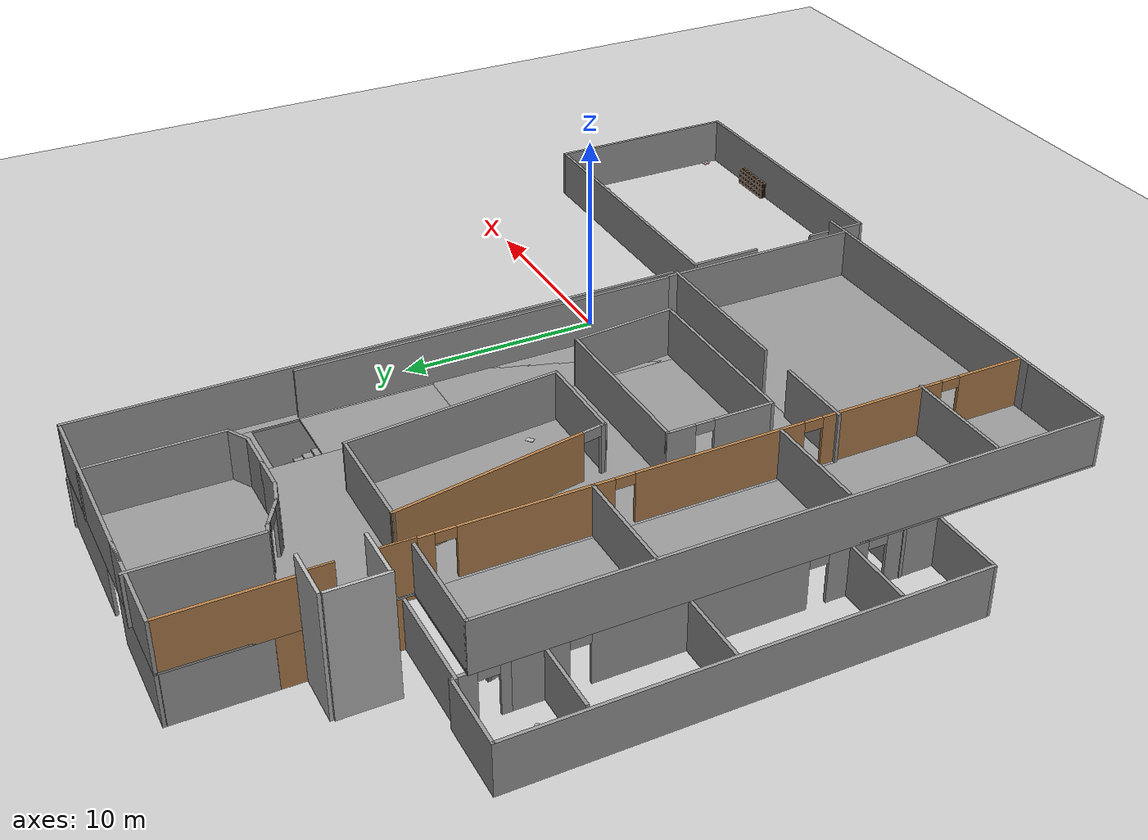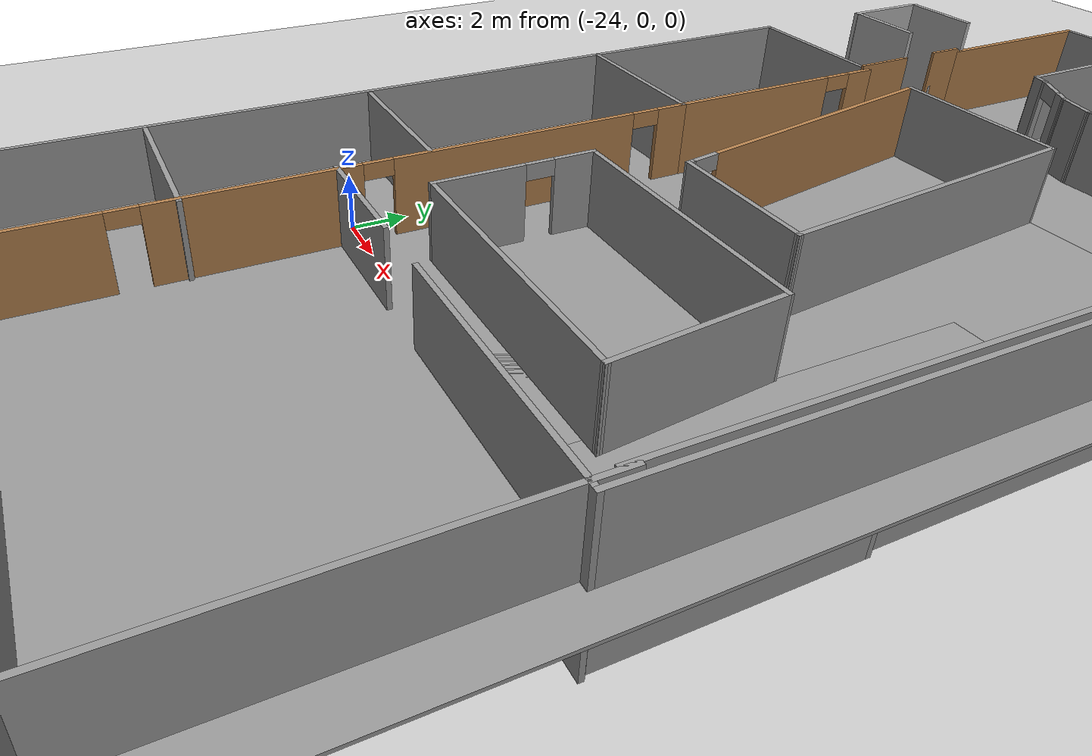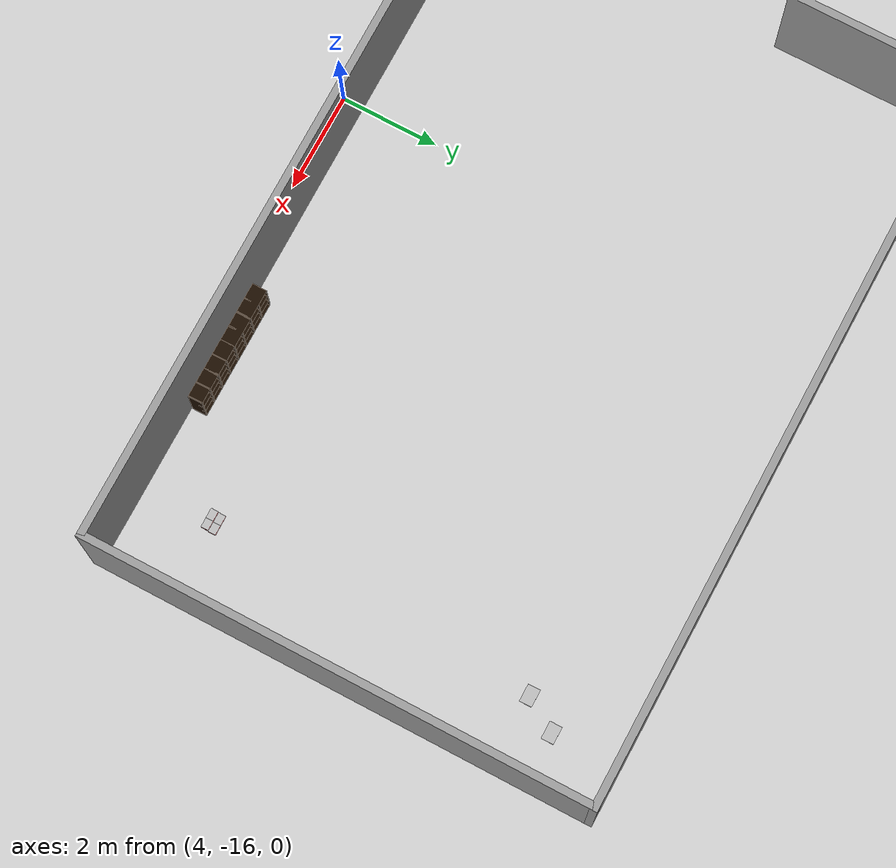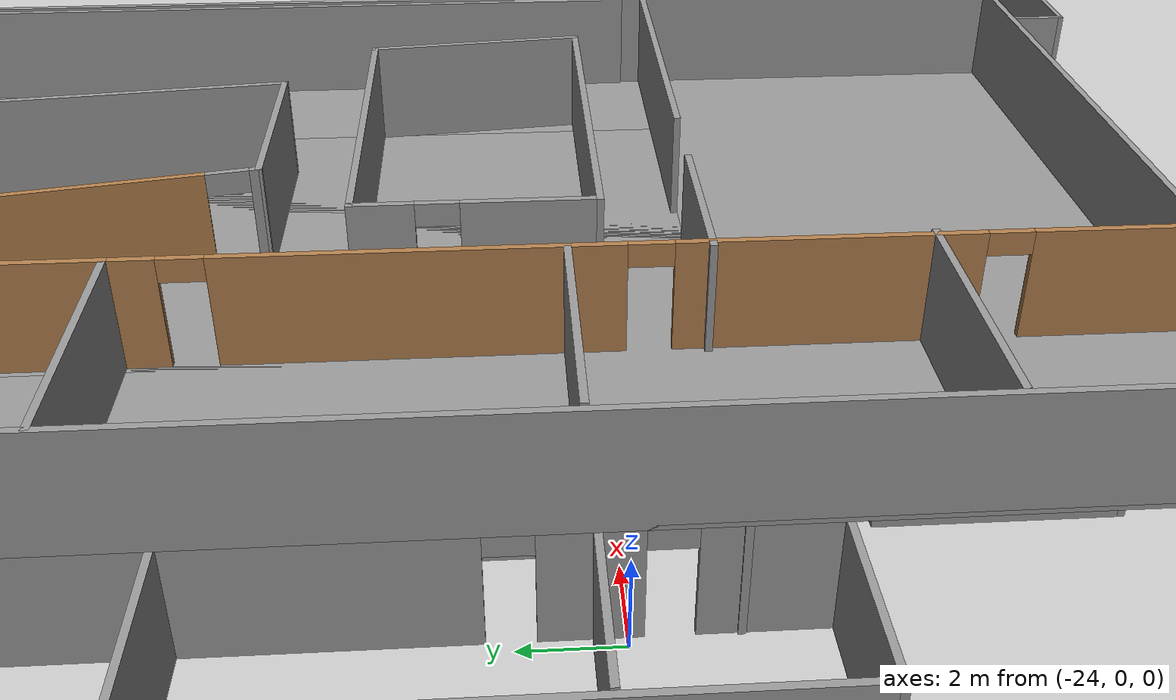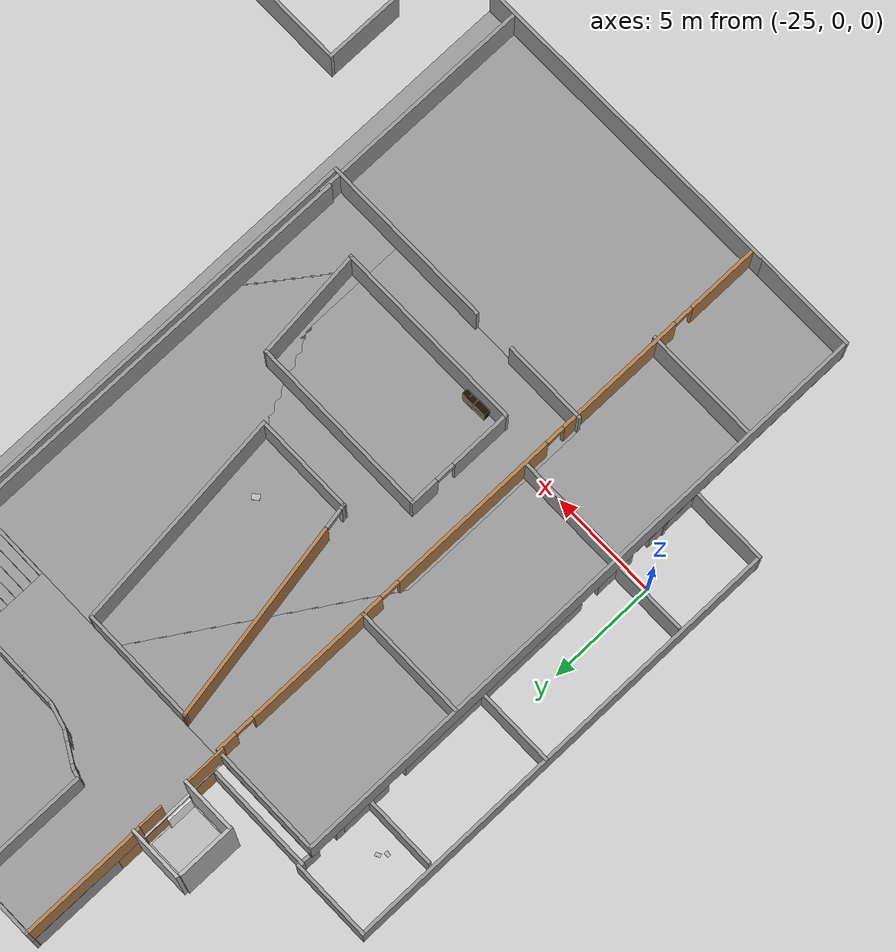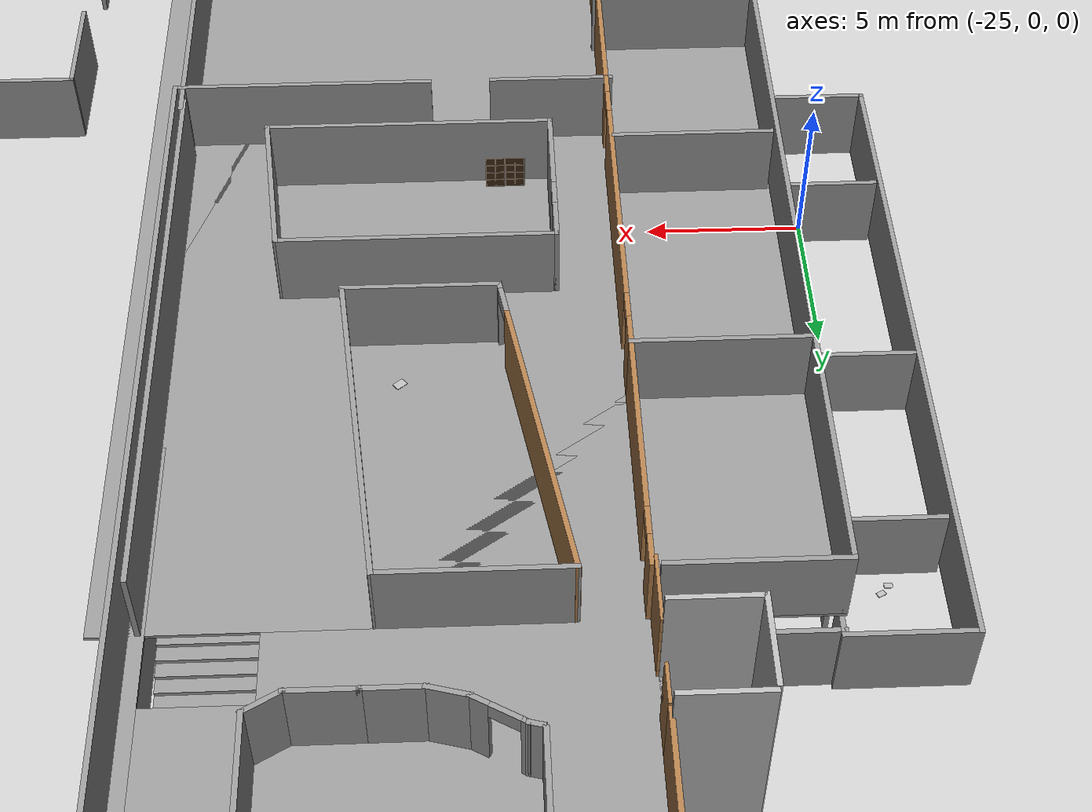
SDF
<sdf version="1.5">
 <world name="default">
  <light name="sun" type="directional">
   <pose>0 0 10 0 -0 0</pose>
   <diffuse>0.8 0.8 0.8 1</diffuse>
   <specular>0.2 0.2 0.2 1</specular>
   <attenuation>
    <range>1000</range>
    <constant>0.9</constant>
    <linear>0.01</linear>
    <quadratic>0.001</quadratic>
   </attenuation>
   <direction>-0.5 0.1 -0.9</direction>
  </light>
  <model name="ground_plane">
   <static>1</static>
   <link name="link">
    <collision name="collision">
     <geometry><plane><normal>0 0 1</normal><size>100 100</size></plane></geometry>
     <surface>
      <contact><collide_bitmask>65535</collide_bitmask></contact>
      <friction><ode><mu>100</mu><mu2>50</mu2></ode></friction>
     </surface>
    </collision>
    <visual name="visual">
     <cast_shadows>0</cast_shadows>
     <geometry><plane><normal>0 0 1</normal><size>100 100</size></plane></geometry>
     <material>
      <script><uri>file://media/materials/scripts/gazebo.material</uri><name>Gazebo/Grey</name></script>
     </material>
    </visual>
   </link>
  </model>
  <plugin name="elevator_event_plugin" filename="libSimEventsPlugin.so">
   <region><name>region1</name><volume><min>-18.64 20.19 1.02</min><max>-18.59 20.27 1.06</max></volume></region>
   <region><name>region1_inside</name><volume><min>-19.7 19.1 0</min><max>-19.1 19.8 1</max></volume></region>
   <region>
    <name>region2_inside</name>
    <volume><min>-19.7 19.1 2.58</min><max>-19.1 19.8 2.8</max></volume>
   </region>
   <region><name>region2</name><volume><min>-18.65 20.18 3.6</min><max>-18.23 20.24 3.65</max></volume></region>
   <event>
    <name>region1_event</name>
    <type>occupied</type>
    <region>region1</region>
    <topic>~/elevator</topic>
    <msg_data>0</msg_data>
   </event>
   <event>
    <name>region2_event</name>
    <type>occupied</type>
    <region>region2</region>
    <topic>~/elevator</topic>
    <msg_data>1</msg_data>
   </event>
   <event>
    <name>region2_1_event</name>
    <type>occupied</type>
    <region>region1_inside</region>
    <topic>~/elevator</topic>
    <msg_data>1</msg_data>
   </event>
   <event>
    <name>region1_2_event</name>
    <type>occupied</type>
    <region>region2_inside</region>
    <topic>~/elevator</topic>
    <msg_data>0</msg_data>
   </event>
  </plugin>
  <model name="elevator">
   <pose>-20 20 0.001 -0 -0 -0</pose>
   <link name="link">
    <inertial>
     <mass>800</mass>
     <inertia><ixx>1</ixx><ixy>0</ixy><ixz>0</ixz><iyy>1</iyy><iyz>0</iyz><izz>1</izz></inertia>
    </inertial>
    <collision name="floor_collision"><geometry><box><size>2.25 2.25 0.001</size></box></geometry></collision>
    <visual name="floor_visual"><geometry><box><size>2.25 2.25 0.001</size></box></geometry></visual>
    <collision name="wall1_collision_bot_in">
     <pose>0.06 0.25 1.125 0 -0 0</pose>
     <geometry><box><size>0.01 0.09 0.36</size></box></geometry>
    </collision>
    <visual name="wall1_visual_bot_in">
     <pose>1 1.25 1.125 0 -0 1.577</pose>
     <geometry><box><size>0.01 0.09 0.36</size></box></geometry>
     <material>
      <script>
       <uri>model://elevator_shaft/materials/scripts</uri>
       <uri>model://elevator_shaft/materials/textures</uri>
       <name>Up_down/Diffuse</name>
      </script>
     </material>
    </visual>
   </link>
   <link name="door">
    <pose>1.0745 -0.5 1.125 0 -0 0</pose>
    <collision name="collision"><geometry><box><size>0.08 1.2 2.25</size></box></geometry></collision>
    <visual name="visual">
     <material>
      <script>
       <uri>model://elevator_door/materials/scripts</uri>
       <uri>model://elevator_door/materials/textures</uri>
       <name>Elevator_door/Picture</name>
      </script>
      <shader type="pixel"><normal_map>__default__</normal_map></shader>
      <ambient>1 1 1 1</ambient>
      <diffuse>1 1 1 1</diffuse>
      <specular>0 0 0 1</specular>
      <emissive>0 0 0 1</emissive>
     </material>
     <geometry><box><size>0.08 1.2 2.25</size></box></geometry>
    </visual>
    <inertial>
     <inertia><ixx>1</ixx><ixy>0</ixy><ixz>0</ixz><iyy>1</iyy><iyz>0</iyz><izz>1</izz></inertia>
     <mass>1</mass>
    </inertial>
   </link>
   <joint name="door" type="prismatic">
    <parent>link</parent>
    <child>door</child>
    <axis>
     <xyz>0 1 0</xyz>
     <limit><lower>0</lower><upper>1.19</upper><effort>0.525</effort></limit>
     <dynamics>
      <damping>1</damping>
      <spring_reference>0</spring_reference>
      <spring_stiffness>0</spring_stiffness>
     </dynamics>
     <use_parent_model_frame>0</use_parent_model_frame>
    </axis>
   </joint>
   <joint name="lift" type="prismatic">
    <parent>world</parent>
    <child>link</child>
    <axis>
     <xyz>0 0 1</xyz>
     <limit><lower>0</lower><upper>10</upper><effort>100000</effort></limit>
     <dynamics>
      <damping>50</damping>
      <spring_reference>0</spring_reference>
      <spring_stiffness>0</spring_stiffness>
     </dynamics>
     <use_parent_model_frame>0</use_parent_model_frame>
    </axis>
    <physics>
     <ode><implicit_spring_damper>1</implicit_spring_damper><limit><cfm>0</cfm><erp>0.2</erp></limit></ode>
    </physics>
   </joint>
   <plugin name="elevator_plugin" filename="libElevatorPlugin.so">
    <lift_joint>elevator::lift</lift_joint>
    <door_joint>elevator::door</door_joint>
    <floor_height>2.675</floor_height>
    <door_wait_time>8</door_wait_time>
    <topic>~/elevator</topic>
   </plugin>
  </model>
  <model name="elevator_shaft">
   <pose>-20 20 0 0 -0 0</pose>
   <static>1</static>
   <link name="link">
    <collision name="shaft_wall1_collision">
     <pose>0 1.45 3 0 -0 0</pose>
     <geometry><box><size>2.5 0.15 6</size></box></geometry>
    </collision>
    <visual name="shaft_wall1_visual">
     <pose>0 1.45 3 0 -0 0</pose>
     <geometry><box><size>2.5 0.15 6</size></box></geometry>
    </visual>
    <collision name="shaft_wall2_collision">
     <pose>0 -1.25 3 0 -0 0</pose>
     <geometry><box><size>2.5 0.15 6</size></box></geometry>
    </collision>
    <visual name="shaft_wall2_visual">
     <pose>0 -1.25 3 0 -0 0</pose>
     <geometry><box><size>2.5 0.15 6</size></box></geometry>
    </visual>
    <collision name="shaft_wall3_collision">
     <pose>-1.25 0 3 0 -0 0</pose>
     <geometry><box><size>0.15 2.7 6</size></box></geometry>
    </collision>
    <visual name="shaft_wall3_visual">
     <pose>-1.25 0 3 0 -0 0</pose>
     <geometry><box><size>0.15 2.7 6</size></box></geometry>
    </visual>
    <collision name="floor0_collision">
     <pose>1.19 0 0.001 0 -0 0</pose>
     <geometry><box><size>0.12 2.5 0.001</size></box></geometry>
    </collision>
    <visual name="floor0_visual">
     <pose>1.19 0 0.001 0 -0 0</pose>
     <geometry><box><size>0.12 2.5 0.001</size></box></geometry>
    </visual>
    <collision name="floor1_collision">
     <pose>1.19 0 2.525 0 -0 0</pose>
     <geometry><box><size>0.12 2.5 0.15</size></box></geometry>
    </collision>
    <visual name="floor1_visual">
     <pose>1.19 0 2.525 0 -0 0</pose>
     <geometry><box><size>0.12 2.5 0.15</size></box></geometry>
    </visual>
   </link>
  </model>
  <model name="elevator_2.5">
   <pose>-18.75 20 0 0 -0 0</pose>
   <link name="Wall_0">
    <collision name="Wall_0_Collision">
     <geometry><box><size>1.4 0.15 2.5</size></box></geometry>
     <pose>0 0 1.25 0 -0 0</pose>
    </collision>
    <visual name="Wall_0_Visual">
     <pose>0 0 1.25 0 -0 0</pose>
     <meta><layer>0</layer></meta>
     <geometry><box><size>1.4 0.15 2.5</size></box></geometry>
     <material><script><name>Gazebo/Wood</name><uri>__default__</uri></script></material>
    </visual>
    <pose>0 -1.875 0 0 0 -1.5708</pose>
   </link>
   <pose>0.02 -1.1 1.15 0 -0 0</pose>
   <link name="Wall_2">
    <collision name="Wall_2_Collision">
     <geometry><box><size>1.4 0.15 2.5</size></box></geometry>
     <pose>0 0 1.25 0 -0 0</pose>
    </collision>
    <visual name="Wall_2_Visual">
     <pose>0 0 1.25 0 -0 0</pose>
     <geometry><box><size>1.4 0.15 2.5</size></box></geometry>
     <material><script><name>Gazebo/Wood</name><uri>__default__</uri></script></material>
    </visual>
    <pose>0 1.875 0 0 0 -1.5708</pose>
   </link>
   <link name="right_elevator_wall_floor_0">
    <collision name="wall1_collision">
     <pose>0 0.6 1.125 0 -0 0</pose>
     <geometry><box><size>0.1 1.15 2.85</size></box></geometry>
    </collision>
    <visual name="wall1_visual">
     <pose>0 0.6 1.125 0 -0 0</pose>
     <geometry><box><size>0.1 1.15 2.85</size></box></geometry>
     <material><script><name>Gazebo/Wood</name><uri>__default__</uri></script></material>
    </visual>
    <collision name="wall1_collision_bot">
     <pose>0.06 0.3 1.125 0 -0 0</pose>
     <geometry><box><size>0.01 0.09 0.36</size></box></geometry>
    </collision>
    <visual name="wall1_visual_bot">
     <pose>0.06 0.25 1.125 0 -0 0</pose>
     <geometry><box><size>0.01 0.09 0.36</size></box></geometry>
     <material>
      <script>
       <uri>model://elevator_shaft_first_floor/materials/scripts</uri>
       <uri>model://elevator_shaft_first_floor/materials/textures</uri>
       <name>Up_down_first_floor/Diffuse</name>
      </script>
     </material>
    </visual>
   </link>
   <static>1</static>
  </model>
  <model name="Building_37">
   <pose>-14.375 11 0 0 -0 0</pose>
   <link name="Floor_0">
    <pose>2.5 1.3455 2.5 0 -0 0</pose>
    <visual name="Floor_0_Visual_0">
     <pose>-1.7875 0.15 0.05 0 -0 0</pose>
     <meta><layer>1</layer></meta>
     <geometry><box><size>10.325 29.15 0.1</size></box></geometry>
     <material>
      <script><uri>file://media/materials/scripts/gazebo.material</uri><name>Gazebo/Grey</name></script>
      <ambient>1 1 1 1</ambient>
     </material>
    </visual>
    <collision name="Floor_0_Collision_0">
     <geometry><box><size>10.325 29.15 0.1</size></box></geometry>
     <pose>-1.7875 0.15 0.05 0 -0 0</pose>
    </collision>
    <visual name="Floor_0_Visual_1">
     <pose>5.1625 -8 0.05 0 -0 0</pose>
     <meta><layer>1</layer></meta>
     <geometry><box><size>3.575 12.85 0.1</size></box></geometry>
     <material>
      <script><uri>file://media/materials/scripts/gazebo.material</uri><name>Gazebo/Grey</name></script>
      <ambient>1 1 1 1</ambient>
     </material>
    </visual>
    <collision name="Floor_0_Collision_1">
     <geometry><box><size>3.575 12.85 0.1</size></box></geometry>
     <pose>5.1625 -8 0.05 0 -0 0</pose>
    </collision>
    <visual name="Floor_0_Visual_2">
     <pose>6.6625 6.567 0.05 0 -0 0</pose>
     <meta><layer>1</layer></meta>
     <geometry><box><size>0.575 16.325 0.1</size></box></geometry>
     <material>
      <script><uri>file://media/materials/scripts/gazebo.material</uri><name>Gazebo/Grey</name></script>
      <ambient>1 1 1 1</ambient>
     </material>
    </visual>
    <collision name="Floor_0_Collision_2">
     <geometry><box><size>0.575 16.325 0.1</size></box></geometry>
     <pose>6.6625 6.567 0.05 0 -0 0</pose>
    </collision>
    <visual name="Floor_0_Visual_3">
     <pose>4.875 10.817 0.05 0 -0 0</pose>
     <meta><layer>1</layer></meta>
     <geometry><box><size>3 7.825 0.1</size></box></geometry>
     <material>
      <script><uri>file://media/materials/scripts/gazebo.material</uri><name>Gazebo/Grey</name></script>
      <ambient>1 1 1 1</ambient>
     </material>
    </visual>
    <collision name="Floor_0_Collision_3">
     <geometry><box><size>3 7.825 0.1</size></box></geometry>
     <pose>4.875 10.817 0.05 0 -0 0</pose>
    </collision>
   </link>
   <link name="Stairs_1">
    <visual name="Stairs_1_Visual_0">
     <pose>7.375 8.0375 0.0625 0 -0 0</pose>
     <meta><layer>2</layer></meta>
     <geometry><box><size>3 0.425 0.125</size></box></geometry>
     <material>
      <script><uri>file://media/materials/scripts/gazebo.material</uri><name>Gazebo/Grey</name></script>
      <ambient>1 1 1 1</ambient>
     </material>
    </visual>
    <collision name="Stairs_1_Collision_0">
     <geometry><box><size>3 0.425 0.125</size></box></geometry>
     <pose>7.375 8.0375 0.0625 0 -0 0</pose>
    </collision>
    <visual name="Stairs_1_Visual_1">
     <pose>7.375 7.6125 0.1875 0 -0 0</pose>
     <meta><layer>2</layer></meta>
     <geometry><box><size>3 0.425 0.125</size></box></geometry>
     <material>
      <script><uri>file://media/materials/scripts/gazebo.material</uri><name>Gazebo/Grey</name></script>
      <ambient>1 1 1 1</ambient>
     </material>
    </visual>
    <collision name="Stairs_1_Collision_1">
     <geometry><box><size>3 0.425 0.125</size></box></geometry>
     <pose>7.375 7.6125 0.1875 0 -0 0</pose>
    </collision>
    <visual name="Stairs_1_Visual_2">
     <pose>7.375 7.1875 0.3125 0 -0 0</pose>
     <meta><layer>2</layer></meta>
     <geometry><box><size>3 0.425 0.125</size></box></geometry>
     <material>
      <script><uri>file://media/materials/scripts/gazebo.material</uri><name>Gazebo/Grey</name></script>
      <ambient>1 1 1 1</ambient>
     </material>
    </visual>
    <collision name="Stairs_1_Collision_2">
     <geometry><box><size>3 0.425 0.125</size></box></geometry>
     <pose>7.375 7.1875 0.3125 0 -0 0</pose>
    </collision>
    <visual name="Stairs_1_Visual_3">
     <pose>7.375 6.7625 0.4375 0 -0 0</pose>
     <meta><layer>2</layer></meta>
     <geometry><box><size>3 0.425 0.125</size></box></geometry>
     <material>
      <script><uri>file://media/materials/scripts/gazebo.material</uri><name>Gazebo/Grey</name></script>
      <ambient>1 1 1 1</ambient>
     </material>
    </visual>
    <collision name="Stairs_1_Collision_3">
     <geometry><box><size>3 0.425 0.125</size></box></geometry>
     <pose>7.375 6.7625 0.4375 0 -0 0</pose>
    </collision>
    <visual name="Stairs_1_Visual_4">
     <pose>7.375 6.3375 0.5625 0 -0 0</pose>
     <meta><layer>2</layer></meta>
     <geometry><box><size>3 0.425 0.125</size></box></geometry>
     <material>
      <script><uri>file://media/materials/scripts/gazebo.material</uri><name>Gazebo/Grey</name></script>
      <ambient>1 1 1 1</ambient>
     </material>
    </visual>
    <collision name="Stairs_1_Collision_4">
     <geometry><box><size>3 0.425 0.125</size></box></geometry>
     <pose>7.375 6.3375 0.5625 0 -0 0</pose>
    </collision>
    <visual name="Stairs_1_Visual_5">
     <pose>7.375 5.9125 0.6875 0 -0 0</pose>
     <meta><layer>2</layer></meta>
     <geometry><box><size>3 0.425 0.125</size></box></geometry>
     <material>
      <script><uri>file://media/materials/scripts/gazebo.material</uri><name>Gazebo/Grey</name></script>
      <ambient>1 1 1 1</ambient>
     </material>
    </visual>
    <collision name="Stairs_1_Collision_5">
     <geometry><box><size>3 0.425 0.125</size></box></geometry>
     <pose>7.375 5.9125 0.6875 0 -0 0</pose>
    </collision>
    <visual name="Stairs_1_Visual_6">
     <pose>7.375 5.4875 0.8125 0 -0 0</pose>
     <meta><layer>2</layer></meta>
     <geometry><box><size>3 0.425 0.125</size></box></geometry>
     <material>
      <script><uri>file://media/materials/scripts/gazebo.material</uri><name>Gazebo/Grey</name></script>
      <ambient>1 1 1 1</ambient>
     </material>
    </visual>
    <collision name="Stairs_1_Collision_6">
     <geometry><box><size>3 0.425 0.125</size></box></geometry>
     <pose>7.375 5.4875 0.8125 0 -0 0</pose>
    </collision>
    <visual name="Stairs_1_Visual_7">
     <pose>7.375 5.0625 0.9375 0 -0 0</pose>
     <meta><layer>2</layer></meta>
     <geometry><box><size>3 0.425 0.125</size></box></geometry>
     <material>
      <script><uri>file://media/materials/scripts/gazebo.material</uri><name>Gazebo/Grey</name></script>
      <ambient>1 1 1 1</ambient>
     </material>
    </visual>
    <collision name="Stairs_1_Collision_7">
     <geometry><box><size>3 0.425 0.125</size></box></geometry>
     <pose>7.375 5.0625 0.9375 0 -0 0</pose>
    </collision>
    <visual name="Stairs_1_Visual_8">
     <pose>7.375 4.6375 1.0625 0 -0 0</pose>
     <meta><layer>2</layer></meta>
     <geometry><box><size>3 0.425 0.125</size></box></geometry>
     <material>
      <script><uri>file://media/materials/scripts/gazebo.material</uri><name>Gazebo/Grey</name></script>
      <ambient>1 1 1 1</ambient>
     </material>
    </visual>
    <collision name="Stairs_1_Collision_8">
     <geometry><box><size>3 0.425 0.125</size></box></geometry>
     <pose>7.375 4.6375 1.0625 0 -0 0</pose>
    </collision>
    <visual name="Stairs_1_Visual_9">
     <pose>7.375 4.2125 1.1875 0 -0 0</pose>
     <meta><layer>2</layer></meta>
     <geometry><box><size>3 0.425 0.125</size></box></geometry>
     <material>
      <script><uri>file://media/materials/scripts/gazebo.material</uri><name>Gazebo/Grey</name></script>
      <ambient>1 1 1 1</ambient>
     </material>
    </visual>
    <collision name="Stairs_1_Collision_9">
     <geometry><box><size>3 0.425 0.125</size></box></geometry>
     <pose>7.375 4.2125 1.1875 0 -0 0</pose>
    </collision>
    <visual name="Stairs_1_Visual_10">
     <pose>7.375 3.7875 1.3125 0 -0 0</pose>
     <meta><layer>2</layer></meta>
     <geometry><box><size>3 0.425 0.125</size></box></geometry>
     <material>
      <script><uri>file://media/materials/scripts/gazebo.material</uri><name>Gazebo/Grey</name></script>
      <ambient>1 1 1 1</ambient>
     </material>
    </visual>
    <collision name="Stairs_1_Collision_10">
     <geometry><box><size>3 0.425 0.125</size></box></geometry>
     <pose>7.375 3.7875 1.3125 0 -0 0</pose>
    </collision>
    <visual name="Stairs_1_Visual_11">
     <pose>7.375 3.3625 1.4375 0 -0 0</pose>
     <meta><layer>2</layer></meta>
     <geometry><box><size>3 0.425 0.125</size></box></geometry>
     <material>
      <script><uri>file://media/materials/scripts/gazebo.material</uri><name>Gazebo/Grey</name></script>
      <ambient>1 1 1 1</ambient>
     </material>
    </visual>
    <collision name="Stairs_1_Collision_11">
     <geometry><box><size>3 0.425 0.125</size></box></geometry>
     <pose>7.375 3.3625 1.4375 0 -0 0</pose>
    </collision>
    <visual name="Stairs_1_Visual_12">
     <pose>7.375 2.9375 1.5625 0 -0 0</pose>
     <meta><layer>2</layer></meta>
     <geometry><box><size>3 0.425 0.125</size></box></geometry>
     <material>
      <script><uri>file://media/materials/scripts/gazebo.material</uri><name>Gazebo/Grey</name></script>
      <ambient>1 1 1 1</ambient>
     </material>
    </visual>
    <collision name="Stairs_1_Collision_12">
     <geometry><box><size>3 0.425 0.125</size></box></geometry>
     <pose>7.375 2.9375 1.5625 0 -0 0</pose>
    </collision>
    <visual name="Stairs_1_Visual_13">
     <pose>7.375 2.5125 1.6875 0 -0 0</pose>
     <meta><layer>2</layer></meta>
     <geometry><box><size>3 0.425 0.125</size></box></geometry>
     <material>
      <script><uri>file://media/materials/scripts/gazebo.material</uri><name>Gazebo/Grey</name></script>
      <ambient>1 1 1 1</ambient>
     </material>
    </visual>
    <collision name="Stairs_1_Collision_13">
     <geometry><box><size>3 0.425 0.125</size></box></geometry>
     <pose>7.375 2.5125 1.6875 0 -0 0</pose>
    </collision>
    <visual name="Stairs_1_Visual_14">
     <pose>7.375 2.0875 1.8125 0 -0 0</pose>
     <meta><layer>2</layer></meta>
     <geometry><box><size>3 0.425 0.125</size></box></geometry>
     <material>
      <script><uri>file://media/materials/scripts/gazebo.material</uri><name>Gazebo/Grey</name></script>
      <ambient>1 1 1 1</ambient>
     </material>
    </visual>
    <collision name="Stairs_1_Collision_14">
     <geometry><box><size>3 0.425 0.125</size></box></geometry>
     <pose>7.375 2.0875 1.8125 0 -0 0</pose>
    </collision>
    <visual name="Stairs_1_Visual_15">
     <pose>7.375 1.6625 1.9375 0 -0 0</pose>
     <meta><layer>2</layer></meta>
     <geometry><box><size>3 0.425 0.125</size></box></geometry>
     <material>
      <script><uri>file://media/materials/scripts/gazebo.material</uri><name>Gazebo/Grey</name></script>
      <ambient>1 1 1 1</ambient>
     </material>
    </visual>
    <collision name="Stairs_1_Collision_15">
     <geometry><box><size>3 0.425 0.125</size></box></geometry>
     <pose>7.375 1.6625 1.9375 0 -0 0</pose>
    </collision>
    <visual name="Stairs_1_Visual_16">
     <pose>7.375 1.2375 2.0625 0 -0 0</pose>
     <meta><layer>2</layer></meta>
     <geometry><box><size>3 0.425 0.125</size></box></geometry>
     <material>
      <script><uri>file://media/materials/scripts/gazebo.material</uri><name>Gazebo/Grey</name></script>
      <ambient>1 1 1 1</ambient>
     </material>
    </visual>
    <collision name="Stairs_1_Collision_16">
     <geometry><box><size>3 0.425 0.125</size></box></geometry>
     <pose>7.375 1.2375 2.0625 0 -0 0</pose>
    </collision>
    <visual name="Stairs_1_Visual_17">
     <pose>7.375 0.8125 2.1875 0 -0 0</pose>
     <meta><layer>2</layer></meta>
     <geometry><box><size>3 0.425 0.125</size></box></geometry>
     <material>
      <script><uri>file://media/materials/scripts/gazebo.material</uri><name>Gazebo/Grey</name></script>
      <ambient>1 1 1 1</ambient>
     </material>
    </visual>
    <collision name="Stairs_1_Collision_17">
     <geometry><box><size>3 0.425 0.125</size></box></geometry>
     <pose>7.375 0.8125 2.1875 0 -0 0</pose>
    </collision>
    <visual name="Stairs_1_Visual_18">
     <pose>7.375 0.3875 2.3125 0 -0 0</pose>
     <meta><layer>2</layer></meta>
     <geometry><box><size>3 0.425 0.125</size></box></geometry>
     <material>
      <script><uri>file://media/materials/scripts/gazebo.material</uri><name>Gazebo/Grey</name></script>
      <ambient>1 1 1 1</ambient>
     </material>
    </visual>
    <collision name="Stairs_1_Collision_18">
     <geometry><box><size>3 0.425 0.125</size></box></geometry>
     <pose>7.375 0.3875 2.3125 0 -0 0</pose>
    </collision>
    <visual name="Stairs_1_Visual_19">
     <pose>7.375 -0.037501 2.4375 0 -0 0</pose>
     <meta><layer>2</layer></meta>
     <geometry><box><size>3 0.425 0.125</size></box></geometry>
     <material>
      <script><uri>file://media/materials/scripts/gazebo.material</uri><name>Gazebo/Grey</name></script>
      <ambient>1 1 1 1</ambient>
     </material>
    </visual>
    <collision name="Stairs_1_Collision_19">
     <geometry><box><size>3 0.425 0.125</size></box></geometry>
     <pose>7.375 -0.037501 2.4375 0 -0 0</pose>
    </collision>
   </link>
   <link name="Wall_27">
    <collision name="Wall_27_Collision">
     <geometry><box><size>6.9 0.15 2.5</size></box></geometry>
     <pose>0 0 1.25 0 -0 0</pose>
    </collision>
    <visual name="Wall_27_Visual">
     <pose>0 0 1.25 0 -0 0</pose>
     <geometry><box><size>6.9 0.15 2.5</size></box></geometry>
     <material>
      <script><uri>file://media/materials/scripts/gazebo.material</uri><name>Gazebo/Grey</name></script>
      <ambient>1 1 1 1</ambient>
     </material>
    </visual>
    <pose>-6 -13 0 0 -0 0</pose>
   </link>
   <link name="Wall_28">
    <collision name="Wall_28_Collision">
     <geometry><box><size>3.15 0.15 2.5</size></box></geometry>
     <pose>0 0 1.25 0 -0 0</pose>
    </collision>
    <visual name="Wall_28_Visual">
     <pose>0 0 1.25 0 -0 0</pose>
     <geometry><box><size>3.15 0.15 2.5</size></box></geometry>
     <material>
      <script><uri>file://media/materials/scripts/gazebo.material</uri><name>Gazebo/Grey</name></script>
      <ambient>1 1 1 1</ambient>
     </material>
    </visual>
    <pose>-2.625 -14.5 0 0 0 -1.5708</pose>
   </link>
   <link name="Wall_30">
    <collision name="Wall_30_Collision">
     <geometry><box><size>10.15 0.15 2.5</size></box></geometry>
     <pose>0 0 1.25 0 -0 0</pose>
    </collision>
    <visual name="Wall_30_Visual">
     <pose>0 0 1.25 0 -0 0</pose>
     <geometry><box><size>10.15 0.15 2.5</size></box></geometry>
     <material>
      <script><uri>file://media/materials/scripts/gazebo.material</uri><name>Gazebo/Grey</name></script>
      <ambient>1 1 1 1</ambient>
     </material>
    </visual>
    <pose>4.375 -13 0 0 -0 3.14159</pose>
   </link>
   <link name="Wall_31">
    <collision name="Wall_31_Collision">
     <geometry><box><size>3.15 0.15 2.5</size></box></geometry>
     <pose>0 0 1.25 0 -0 0</pose>
    </collision>
    <visual name="Wall_31_Visual">
     <pose>0 0 1.25 0 -0 0</pose>
     <geometry><box><size>3.15 0.15 2.5</size></box></geometry>
     <material>
      <script><uri>file://media/materials/scripts/gazebo.material</uri><name>Gazebo/Grey</name></script>
      <ambient>1 1 1 1</ambient>
     </material>
    </visual>
    <pose>-0.625 -14.5 0 0 0 -1.5708</pose>
   </link>
   <link name="Wall_33">
    <collision name="Wall_33_Collision">
     <geometry><box><size>5.9 0.15 2.5</size></box></geometry>
     <pose>0 0 1.25 0 -0 0</pose>
    </collision>
    <visual name="Wall_33_Visual">
     <pose>0 0 1.25 0 -0 0</pose>
     <meta><layer>3</layer></meta>
     <geometry><box><size>5.9 0.15 2.5</size></box></geometry>
     <material><script><name>Gazebo/Wood</name><uri>__default__</uri></script></material>
    </visual>
    <pose>-4.375 13.125 2.5 0 0 -1.5708</pose>
   </link>
   <pose>-4.35 9.85 3.7 0 -0 0</pose>
   <link name="right_elevator_wall_floor_1">
    <collision name="wall1_collision">
     <pose>-4.32 9.6 3.7 0 -0 0</pose>
     <geometry><box><size>0.1 1.15 2.85</size></box></geometry>
    </collision>
    <visual name="wall1_visual">
     <pose>-4.35 9.6 3.7 0 -0 0</pose>
     <geometry><box><size>0.1 1.15 2.85</size></box></geometry>
     <material><script><name>Gazebo/Wood</name><uri>__default__</uri></script></material>
    </visual>
    <collision name="wall1_collision_bot">
     <pose>-4.3 9.2 3.7 0 -0 0</pose>
     <geometry><box><size>0.01 0.09 0.36</size></box></geometry>
    </collision>
    <visual name="wall1_visual_bot">
     <pose>-4.3 9.2 3.7 0 -0 0</pose>
     <geometry><box><size>0.01 0.09 0.36</size></box></geometry>
     <material>
      <script>
       <uri>model://elevator_shaft_second_floor/materials/scripts</uri>
       <uri>model://elevator_shaft_second_floor/materials/textures</uri>
       <name>Up_down_second_floor/Diffuse</name>
      </script>
     </material>
    </visual>
   </link>
   <link name="left_elevator_wall_floor_1">
    <collision name="wall1_collision_l">
     <pose>-4.32 6.8 3.7 0 -0 0</pose>
     <geometry><box><size>0.1 2 2.85</size></box></geometry>
    </collision>
    <visual name="wall1_visual_l">
     <pose>-4.35 6.8 3.7 0 -0 0</pose>
     <geometry><box><size>0.1 2 2.85</size></box></geometry>
     <material><script><name>Gazebo/Wood</name><uri>__default__</uri></script></material>
    </visual>
   </link>
   <link name="Wall_34">
    <collision name="Wall_34_Collision">
     <geometry><box><size>5.15 0.15 2.5</size></box></geometry>
     <pose>0 0 1.25 0 -0 0</pose>
    </collision>
    <visual name="Wall_34_Visual">
     <pose>0 0 1.25 0 -0 0</pose>
     <meta><layer>3</layer></meta>
     <geometry><box><size>5.15 0.15 2.5</size></box></geometry>
     <material>
      <script><uri>file://media/materials/scripts/gazebo.material</uri><name>Gazebo/Grey</name></script>
      <ambient>1 1 1 1</ambient>
     </material>
    </visual>
    <pose>-1.875 16 2.5 0 -0 0</pose>
   </link>
   <link name="Wall_35">
    <collision name="Wall_35_Collision">
     <geometry><box><size>6.9 0.15 2.5</size></box></geometry>
     <pose>0 0 1.25 0 -0 0</pose>
    </collision>
    <visual name="Wall_35_Visual">
     <pose>-1.7 0 1.25 0 -0 0</pose>
     <meta><layer>3</layer></meta>
     <geometry><box><size>9.9 0.15 2.5</size></box></geometry>
     <material>
      <script><uri>file://media/materials/scripts/gazebo.material</uri><name>Gazebo/Grey</name></script>
      <ambient>1 1 1 1</ambient>
     </material>
    </visual>
    <pose>6 16 2.5 0 -0 0</pose>
   </link>
   <pose>-4.32 7.95 3.7 0 -0 0</pose>
   <link name="Wall_38">
    <pose>-1.5 1 2.5 0 0 -1.39755</pose>
    <visual name="Wall_38_Visual_0">
     <pose>-0.58726 0 1.25 0 -0 0</pose>
     <meta><layer>3</layer></meta>
     <geometry><box><size>9.12745 0.15 2.5</size></box></geometry>
     <material>
      <script><uri>file://media/materials/scripts/gazebo.material</uri><name>Gazebo/Wood</name></script>
      <ambient>1 1 1 1</ambient>
     </material>
    </visual>
    <collision name="Wall_38_Collision_0">
     <geometry><box><size>9.12745 0.15 2.5</size></box></geometry>
     <pose>-0.58726 0 1.25 0 -0 0</pose>
    </collision>
    <visual name="Wall_38_Visual_1">
     <pose>5.01372 0 1.25 0 -0 0</pose>
     <meta><layer>3</layer></meta>
     <geometry><box><size>0.274521 0.15 2.5</size></box></geometry>
     <material>
      <script><uri>file://media/materials/scripts/gazebo.material</uri><name>Gazebo/Grey</name></script>
      <ambient>1 1 1 1</ambient>
     </material>
    </visual>
    <collision name="Wall_38_Collision_1">
     <geometry><box><size>0.274521 0.15 2.5</size></box></geometry>
     <pose>5.01372 0 1.25 0 -0 0</pose>
    </collision>
    <visual name="Wall_38_Visual_2">
     <pose>4.42646 0 2.25 0 -0 0</pose>
     <meta><layer>3</layer></meta>
     <geometry><box><size>0.9 0.15 0.5</size></box></geometry>
     <material>
      <script><uri>file://media/materials/scripts/gazebo.material</uri><name>Gazebo/Grey</name></script>
      <ambient>1 1 1 1</ambient>
     </material>
    </visual>
    <collision name="Wall_38_Collision_2">
     <geometry><box><size>0.9 0.15 0.5</size></box></geometry>
     <pose>4.42646 0 2.25 0 -0 0</pose>
    </collision>
   </link>
   <link name="Wall_39">
    <collision name="Wall_39_Collision">
     <geometry><box><size>4.65 0.15 2.5</size></box></geometry>
     <pose>0 0 1.25 0 -0 0</pose>
    </collision>
    <visual name="Wall_39_Visual">
     <pose>0 0 1.25 0 -0 0</pose>
     <meta><layer>3</layer></meta>
     <geometry><box><size>4.65 0.15 2.5</size></box></geometry>
     <material>
      <script><uri>file://media/materials/scripts/gazebo.material</uri><name>Gazebo/Grey</name></script>
      <ambient>1 1 1 1</ambient>
     </material>
    </visual>
    <pose>1.625 -4 2.5 0 -0 0</pose>
   </link>
   <link name="Wall_4">
    <collision name="Wall_4_Collision">
     <geometry><box><size>5.15 0.15 2.5</size></box></geometry>
     <pose>0 0 1.25 0 -0 0</pose>
    </collision>
    <visual name="Wall_4_Visual">
     <pose>0 0 1.25 0 -0 0</pose>
     <geometry><box><size>5.15 0.15 2.5</size></box></geometry>
     <material>
      <script><uri>file://media/materials/scripts/gazebo.material</uri><name>Gazebo/Grey</name></script>
      <ambient>1 1 1 1</ambient>
     </material>
    </visual>
    <pose>-1.875 16 0 0 -0 0</pose>
   </link>
   <link name="Wall_40">
    <collision name="Wall_40_Collision">
     <geometry><box><size>10.1999 0.15 2.5</size></box></geometry>
     <pose>0 0 1.25 0 -0 0</pose>
    </collision>
    <visual name="Wall_40_Visual">
     <pose>0 0 1.25 0 -0 0</pose>
     <meta><layer>3</layer></meta>
     <geometry><box><size>10.1999 0.15 2.5</size></box></geometry>
     <material>
      <script><uri>file://media/materials/scripts/gazebo.material</uri><name>Gazebo/Grey</name></script>
      <ambient>1 1 1 1</ambient>
     </material>
    </visual>
    <pose>3.375 1 2.5 0 -0 1.67047</pose>
   </link>
   <link name="Wall_41">
    <collision name="Wall_41_Collision">
     <geometry><box><size>5.4 0.15 2.5</size></box></geometry>
     <pose>0 0 1.25 0 -0 0</pose>
    </collision>
    <visual name="Wall_41_Visual">
     <pose>0 0 1.25 0 -0 0</pose>
     <meta><layer>3</layer></meta>
     <geometry><box><size>5.4 0.15 2.5</size></box></geometry>
     <material>
      <script><uri>file://media/materials/scripts/gazebo.material</uri><name>Gazebo/Grey</name></script>
      <ambient>1 1 1 1</ambient>
     </material>
    </visual>
    <pose>0.25 6 2.5 0 -0 3.14159</pose>
   </link>
   <link name="Wall_42">
    <collision name="Wall_42_Collision">
     <geometry><box><size>8.4 0.15 2.5</size></box></geometry>
     <pose>0 0 1.25 0 -0 0</pose>
    </collision>
    <visual name="Wall_42_Visual">
     <pose>0 0 1.25 0 -0 0</pose>
     <meta><layer>3</layer></meta>
     <geometry><box><size>8.4 0.15 2.5</size></box></geometry>
     <material>
      <script><uri>file://media/materials/scripts/gazebo.material</uri><name>Gazebo/Grey</name></script>
      <ambient>1 1 1 1</ambient>
     </material>
    </visual>
    <pose>1.75 -6 2.5 0 -0 0</pose>
   </link>
   <link name="Wall_43">
    <collision name="Wall_43_Collision">
     <geometry><box><size>5.17494 0.15 2.5</size></box></geometry>
     <pose>0 0 1.25 0 -0 0</pose>
    </collision>
    <visual name="Wall_43_Visual">
     <pose>0 0 1.25 0 -0 0</pose>
     <meta><layer>3</layer></meta>
     <geometry><box><size>5.17494 0.15 2.5</size></box></geometry>
     <material>
      <script><uri>file://media/materials/scripts/gazebo.material</uri><name>Gazebo/Grey</name></script>
      <ambient>1 1 1 1</ambient>
     </material>
    </visual>
    <pose>6.125 -8.5 2.5 0 0 -1.47113</pose>
   </link>
   <link name="Wall_44">
    <collision name="Wall_44_Collision">
     <geometry><box><size>8.9 0.15 2.5</size></box></geometry>
     <pose>0 0 1.25 0 -0 0</pose>
    </collision>
    <visual name="Wall_44_Visual">
     <pose>0 0 1.25 0 -0 0</pose>
     <meta><layer>3</layer></meta>
     <geometry><box><size>8.9 0.15 2.5</size></box></geometry>
     <material>
      <script><uri>file://media/materials/scripts/gazebo.material</uri><name>Gazebo/Grey</name></script>
      <ambient>1 1 1 1</ambient>
     </material>
    </visual>
    <pose>2 -11 2.5 0 -0 3.14159</pose>
   </link>
   <link name="Wall_45">
    <pose>-2.375 -8.5 2.5 0 -0 1.5708</pose>
    <visual name="Wall_45_Visual_0">
     <pose>-1.13354 0 1.25 0 -0 0</pose>
     <meta><layer>3</layer></meta>
     <geometry><box><size>2.88293 0.15 2.5</size></box></geometry>
     <material>
      <script><uri>file://media/materials/scripts/gazebo.material</uri><name>Gazebo/Grey</name></script>
      <ambient>1 1 1 1</ambient>
     </material>
    </visual>
    <collision name="Wall_45_Collision_0">
     <geometry><box><size>2.88293 0.15 2.5</size></box></geometry>
     <pose>-1.13354 0 1.25 0 -0 0</pose>
    </collision>
    <visual name="Wall_45_Visual_1">
     <pose>1.89146 0 1.25 0 -0 0</pose>
     <meta><layer>3</layer></meta>
     <geometry><box><size>1.36708 0.15 2.5</size></box></geometry>
     <material>
      <script><uri>file://media/materials/scripts/gazebo.material</uri><name>Gazebo/Grey</name></script>
      <ambient>1 1 1 1</ambient>
     </material>
    </visual>
    <collision name="Wall_45_Collision_1">
     <geometry><box><size>1.36708 0.15 2.5</size></box></geometry>
     <pose>1.89146 0 1.25 0 -0 0</pose>
    </collision>
    <visual name="Wall_45_Visual_2">
     <pose>0.757925 0 2.25 0 -0 0</pose>
     <meta><layer>3</layer></meta>
     <geometry><box><size>0.9 0.15 0.5</size></box></geometry>
     <material>
      <script><uri>file://media/materials/scripts/gazebo.material</uri><name>Gazebo/Grey</name></script>
      <ambient>1 1 1 1</ambient>
     </material>
    </visual>
    <collision name="Wall_45_Collision_2">
     <geometry><box><size>0.9 0.15 0.5</size></box></geometry>
     <pose>0.757925 0 2.25 0 -0 0</pose>
    </collision>
   </link>
   <link name="Wall_46">
    <collision name="Wall_46_Collision">
     <geometry><box><size>29.15 0.15 2.5</size></box></geometry>
     <pose>0 0 1.25 0 -0 0</pose>
    </collision>
    <visual name="Wall_46_Visual">
     <pose>0 0 1.25 0 -0 0</pose>
     <meta><layer>3</layer></meta>
     <geometry><box><size>29.15 0.15 2.5</size></box></geometry>
     <material>
      <script><uri>file://media/materials/scripts/gazebo.material</uri><name>Gazebo/Grey</name></script>
      <ambient>1 1 1 1</ambient>
     </material>
    </visual>
    <pose>9.375 1.5 2.5 0 0 -1.5708</pose>
   </link>
   <link name="Wall_47">
    <collision name="Wall_47_Collision">
     <geometry><box><size>3.9 0.15 2.5</size></box></geometry>
     <pose>0 0 1.25 0 -0 0</pose>
    </collision>
    <visual name="Wall_47_Visual">
     <pose>0 0 1.25 0 -0 0</pose>
     <meta><layer>3</layer></meta>
     <geometry><box><size>3.9 0.15 2.5</size></box></geometry>
     <material>
      <script><uri>file://media/materials/scripts/gazebo.material</uri><name>Gazebo/Grey</name></script>
      <ambient>1 1 1 1</ambient>
     </material>
    </visual>
    <pose>-2.5 -13 2.5 0 -0 0</pose>
   </link>
   <link name="Wall_49">
    <collision name="Wall_49_Collision">
     <geometry><box><size>8.15 0.15 2.5</size></box></geometry>
     <pose>0 0 1.25 0 -0 0</pose>
    </collision>
    <visual name="Wall_49_Visual">
     <pose>0 0 1.25 0 -0 0</pose>
     <meta><layer>3</layer></meta>
     <geometry><box><size>8.15 0.15 2.5</size></box></geometry>
     <material>
      <script><uri>file://media/materials/scripts/gazebo.material</uri><name>Gazebo/Grey</name></script>
      <ambient>1 1 1 1</ambient>
     </material>
    </visual>
    <pose>5.375 -13 2.5 0 -0 3.14159</pose>
   </link>
   <link name="Wall_6">
    <collision name="Wall_6_Collision">
     <geometry><box><size>6.9 0.15 2.5</size></box></geometry>
     <pose>0 0 1.25 0 -0 0</pose>
    </collision>
    <visual name="Wall_6_Visual">
     <pose>0 0 1.25 0 -0 0</pose>
     <geometry><box><size>6.9 0.15 2.5</size></box></geometry>
     <material>
      <script><uri>file://media/materials/scripts/gazebo.material</uri><name>Gazebo/Grey</name></script>
      <ambient>1 1 1 1</ambient>
     </material>
    </visual>
    <pose>6 16 0 0 -0 0</pose>
   </link>
   <link name="Wall_8">
    <collision name="Wall_8_Collision">
     <geometry><box><size>5.15 0.15 2.5</size></box></geometry>
     <pose>0 0 1.25 0 -0 0</pose>
    </collision>
    <visual name="Wall_8_Visual">
     <pose>0 0 1.25 0 -0 0</pose>
     <geometry><box><size>5.15 0.15 2.5</size></box></geometry>
     <material>
      <script><uri>file://media/materials/scripts/gazebo.material</uri><name>Gazebo/Grey</name></script>
      <ambient>1 1 1 1</ambient>
     </material>
    </visual>
    <pose>-6.875 6.5 0 0 -0 3.14159</pose>
   </link>
   <static>1</static>
  </model>
  <model name="first_floor_add">
   <pose>-6.66595 1.00331 0 0 -0 0</pose>
   <link name="Wall_13">
    <collision name="Wall_13_Collision">
     <geometry><box><size>2 0.15 2.5</size></box></geometry>
     <pose>0 0 1.25 0 -0 0</pose>
    </collision>
    <visual name="Wall_13_Visual">
     <pose>0 0 1.25 0 -0 0</pose>
     <geometry><box><size>2 0.15 2.5</size></box></geometry>
     <material>
      <script><uri>file://media/materials/scripts/gazebo.material</uri><name>Gazebo/Grey</name></script>
      <ambient>1 1 1 1</ambient>
     </material>
     <meta><layer>0</layer></meta>
    </visual>
    <pose>-7.36405 -6.11422 0 0 -0 0</pose>
   </link>
   <link name="Wall_15">
    <collision name="Wall_15_Collision">
     <geometry><box><size>2.08472 0.15 2.5</size></box></geometry>
     <pose>0 0 1.25 0 -0 0</pose>
    </collision>
    <visual name="Wall_15_Visual">
     <pose>0 0 1.25 0 -0 0</pose>
     <geometry><box><size>2.08472 0.15 2.5</size></box></geometry>
     <material>
      <script><uri>file://media/materials/scripts/gazebo.material</uri><name>Gazebo/Grey</name></script>
      <ambient>1 1 1 1</ambient>
     </material>
     <meta><layer>0</layer></meta>
    </visual>
    <pose>-5.55503 -6.50778 0 0 -0 -0.418849</pose>
   </link>
   <link name="Wall_16">
    <collision name="Wall_16_Collision">
     <geometry><box><size>3.75 0.15 2.5</size></box></geometry>
     <pose>0 0 1.25 0 -0 0</pose>
    </collision>
    <visual name="Wall_16_Visual">
     <pose>0 0 1.25 0 -0 0</pose>
     <geometry><box><size>3.75 0.15 2.5</size></box></geometry>
     <material>
      <script><uri>file://media/materials/scripts/gazebo.material</uri><name>Gazebo/Grey</name></script>
      <ambient>1 1 1 1</ambient>
     </material>
     <meta><layer>0</layer></meta>
    </visual>
    <pose>-2.87101 -6.9721 0 0 -0 0</pose>
   </link>
   <link name="Wall_20">
    <collision name="Wall_20_Collision">
     <geometry><box><size>3.75 0.15 2.5</size></box></geometry>
     <pose>0 1.2 1.25 0 -0 0</pose>
    </collision>
    <visual name="Wall_20_Visual">
     <pose>0 1.2 1.25 0 -0 0</pose>
     <geometry><box><size>3.75 0.15 2.5</size></box></geometry>
     <material>
      <script><uri>file://media/materials/scripts/gazebo.material</uri><name>Gazebo/Grey</name></script>
      <ambient>1 1 1 1</ambient>
     </material>
     <meta><layer>0</layer></meta>
    </visual>
    <pose>-2.8204 -9.76422 0 0 -0 3.14159</pose>
   </link>
   <link name="Wall_22">
    <collision name="Wall_22_Collision">
     <geometry><box><size>10 0.15 2.5</size></box></geometry>
     <pose>0 0 1.25 0 -0 0</pose>
    </collision>
    <visual name="Wall_22_Visual">
     <pose>0 0 1.25 0 -0 0</pose>
     <geometry><box><size>10 0.15 2.5</size></box></geometry>
     <material>
      <script><uri>file://media/materials/scripts/gazebo.material</uri><name>Gazebo/Grey</name></script>
      <ambient>1 1 1 1</ambient>
     </material>
     <meta><layer>0</layer></meta>
    </visual>
    <pose>-9.5454 -10.8642 0 0 -0 3.14159</pose>
   </link>
   <link name="Wall_23">
    <collision name="Wall_23_Collision">
     <geometry><box><size>5 0.15 2.5</size></box></geometry>
     <pose>0 0 1.25 0 -0 0</pose>
    </collision>
    <visual name="Wall_23_Visual">
     <pose>0 0 1.25 0 -0 0</pose>
     <geometry><box><size>5 0.15 2.5</size></box></geometry>
     <material>
      <script><uri>file://media/materials/scripts/gazebo.material</uri><name>Gazebo/Grey</name></script>
      <ambient>1 1 1 1</ambient>
     </material>
     <meta><layer>0</layer></meta>
    </visual>
    <pose>-14.4704 -8.43922 0 0 -0 1.5708</pose>
   </link>
   <link name="Wall_24">
    <collision name="Wall_24_Collision">
     <geometry><box><size>4.25 0.15 2.5</size></box></geometry>
     <pose>0 0 1.25 0 -0 0</pose>
    </collision>
    <visual name="Wall_24_Visual">
     <pose>0 0 1.25 0 -0 0</pose>
     <geometry><box><size>4.25 0.15 2.5</size></box></geometry>
     <material>
      <script><uri>file://media/materials/scripts/gazebo.material</uri><name>Gazebo/Grey</name></script>
      <ambient>1 1 1 1</ambient>
     </material>
     <meta><layer>0</layer></meta>
    </visual>
    <pose>-12.4204 -6.01422 0 0 -0 0</pose>
   </link>
   <link name="Wall_27">
    <collision name="Wall_27_Collision">
     <geometry><box><size>15 0.15 2.5</size></box></geometry>
     <pose>0 0 1.25 0 -0 0</pose>
    </collision>
    <visual name="Wall_27_Visual">
     <pose>0 0 1.25 0 -0 0</pose>
     <geometry><box><size>15 0.15 2.5</size></box></geometry>
     <material>
      <script><uri>file://media/materials/scripts/gazebo.material</uri><name>Gazebo/Grey</name></script>
      <ambient>1 1 1 1</ambient>
     </material>
     <meta><layer>0</layer></meta>
    </visual>
    <pose>13.2135 -16.6492 0 0 -0 0</pose>
   </link>
   <link name="Wall_28">
    <collision name="Wall_28_Collision">
     <geometry><box><size>10.25 0.15 2.5</size></box></geometry>
     <pose>0 0 1.25 0 -0 0</pose>
    </collision>
    <visual name="Wall_28_Visual">
     <pose>0 0 1.25 0 -0 0</pose>
     <geometry><box><size>10.25 0.15 2.5</size></box></geometry>
     <material>
      <script><uri>file://media/materials/scripts/gazebo.material</uri><name>Gazebo/Grey</name></script>
      <ambient>1 1 1 1</ambient>
     </material>
     <meta><layer>0</layer></meta>
    </visual>
    <pose>20.6385 -11.5992 0 0 -0 1.5708</pose>
   </link>
   <link name="Wall_29">
    <collision name="Wall_29_Collision">
     <geometry><box><size>15 0.15 2.5</size></box></geometry>
     <pose>0 0 1.25 0 -0 0</pose>
    </collision>
    <visual name="Wall_29_Visual">
     <pose>0 0 1.25 0 -0 0</pose>
     <geometry><box><size>15 0.15 2.5</size></box></geometry>
     <material>
      <script><uri>file://media/materials/scripts/gazebo.material</uri><name>Gazebo/Grey</name></script>
      <ambient>1 1 1 1</ambient>
     </material>
     <meta><layer>0</layer></meta>
    </visual>
    <pose>13.2135 -6.5492 0 0 -0 3.14159</pose>
   </link>
   <link name="Wall_31">
    <collision name="Wall_31_Collision">
     <geometry><box><size>3.25 0.15 2.5</size></box></geometry>
     <pose>0 0 1.25 0 -0 0</pose>
    </collision>
    <visual name="Wall_31_Visual">
     <pose>0 0 1.25 0 -0 0</pose>
     <geometry><box><size>3.25 0.15 2.5</size></box></geometry>
     <material>
      <script><uri>file://media/materials/scripts/gazebo.material</uri><name>Gazebo/Grey</name></script>
      <ambient>1 1 1 1</ambient>
     </material>
     <meta><layer>0</layer></meta>
    </visual>
    <pose>5.78854 -15.0992 0 0 -0 1.5708</pose>
   </link>
   <link name="Wall_33">
    <collision name="Wall_33_Collision">
     <geometry><box><size>3.75 0.15 2.5</size></box></geometry>
     <pose>0 0 1.25 0 -0 0</pose>
    </collision>
    <visual name="Wall_33_Visual">
     <pose>0 0 1.25 0 -0 0</pose>
     <geometry><box><size>3.75 0.15 2.5</size></box></geometry>
     <material>
      <script><uri>file://media/materials/scripts/gazebo.material</uri><name>Gazebo/Grey</name></script>
      <ambient>1 1 1 1</ambient>
     </material>
     <meta><layer>0</layer></meta>
    </visual>
    <pose>5.78854 -8.34919 0 0 -0 -1.5708</pose>
   </link>
   <link name="Wall_36">
    <collision name="Wall_36_Collision">
     <geometry><box><size>2.35 0.15 2.5</size></box></geometry>
     <pose>1 0 1.25 0 -0 0</pose>
    </collision>
    <visual name="Wall_36_Visual">
     <pose>1 0 1.25 0 -0 0</pose>
     <geometry><box><size>2.35 0.15 2.5</size></box></geometry>
     <material>
      <script><uri>file://media/materials/scripts/gazebo.material</uri><name>Gazebo/Grey</name></script>
      <ambient>1 1 1 1</ambient>
     </material>
     <meta><layer>0</layer></meta>
    </visual>
    <pose>-1.07101 -7.2721 0 0 -0 -1.5708</pose>
   </link>
   <link name="Wall_41">
    <collision name="Wall_41_Collision">
     <geometry><box><size>6.75 0.15 2.5</size></box></geometry>
     <pose>0 0 1.25 0 -0 0</pose>
    </collision>
    <visual name="Wall_41_Visual">
     <pose>0 0 1.25 0 -0 0</pose>
     <geometry><box><size>6.75 0.15 2.5</size></box></geometry>
     <material>
      <script><uri>file://media/materials/scripts/gazebo.material</uri><name>Gazebo/Grey</name></script>
      <ambient>1 1 1 1</ambient>
     </material>
     <meta><layer>0</layer></meta>
    </visual>
    <pose>-9.89713 6.06852 0 0 -0 0</pose>
   </link>
   <link name="Wall_42">
    <collision name="Wall_42_Collision">
     <geometry><box><size>8.5 0.15 2.5</size></box></geometry>
     <pose>0 0 1.25 0 -0 0</pose>
    </collision>
    <visual name="Wall_42_Visual">
     <pose>0 0 1.25 0 -0 0</pose>
     <geometry><box><size>8.5 0.15 2.5</size></box></geometry>
     <material>
      <script><uri>file://media/materials/scripts/gazebo.material</uri><name>Gazebo/Grey</name></script>
      <ambient>1 1 1 1</ambient>
     </material>
     <meta><layer>0</layer></meta>
    </visual>
    <pose>-6.59713 10.2435 0 0 -0 1.5708</pose>
   </link>
   <link name="Wall_43">
    <collision name="Wall_43_Collision">
     <geometry><box><size>8.75 0.15 2.5</size></box></geometry>
     <pose>0 0 1.25 0 -0 0</pose>
    </collision>
    <visual name="Wall_43_Visual">
     <pose>0 0 1.25 0 -0 0</pose>
     <geometry><box><size>8.75 0.15 2.5</size></box></geometry>
     <material>
      <script><uri>file://media/materials/scripts/gazebo.material</uri><name>Gazebo/Grey</name></script>
      <ambient>1 1 1 1</ambient>
     </material>
     <meta><layer>0</layer></meta>
    </visual>
    <pose>-10.8971 14.4185 0 0 -0 3.14159</pose>
   </link>
   <link name="Wall_44">
    <pose>-14.1971 10.2435 0 0 -0 -1.3357</pose>
    <visual name="Wall_44_Visual_0">
     <pose>-3.81233 0 1.25 0 -0 0</pose>
     <geometry><box><size>1.11152 0.15 2.5</size></box></geometry>
     <material>
      <script><uri>file://media/materials/scripts/gazebo.material</uri><name>Gazebo/Grey</name></script>
      <ambient>1 1 1 1</ambient>
     </material>
     <meta><layer>0</layer></meta>
    </visual>
    <collision name="Wall_44_Collision_0">
     <geometry><box><size>1.11152 0.15 2.5</size></box></geometry>
     <pose>-3.81233 0 1.25 0 -0 0</pose>
    </collision>
    <visual name="Wall_44_Visual_1">
     <pose>0.408277 0 1.25 0 -0 0</pose>
     <geometry><box><size>5.5297 0.15 2.5</size></box></geometry>
     <material>
      <script><uri>file://media/materials/scripts/gazebo.material</uri><name>Gazebo/Grey</name></script>
      <ambient>1 1 1 1</ambient>
     </material>
     <meta><layer>0</layer></meta>
    </visual>
    <collision name="Wall_44_Collision_1">
     <geometry><box><size>5.5297 0.15 2.5</size></box></geometry>
     <pose>0.408277 0 1.25 0 -0 0</pose>
    </collision>
    <visual name="Wall_44_Visual_2">
     <pose>4.22061 0 1.25 0 -0 0</pose>
     <geometry><box><size>0.294964 0.15 2.5</size></box></geometry>
     <material>
      <script><uri>file://media/materials/scripts/gazebo.material</uri><name>Gazebo/Grey</name></script>
      <ambient>1 1 1 1</ambient>
     </material>
     <meta><layer>0</layer></meta>
    </visual>
    <collision name="Wall_44_Collision_2">
     <geometry><box><size>0.294964 0.15 2.5</size></box></geometry>
     <pose>4.22061 0 1.25 0 -0 0</pose>
    </collision>
    <visual name="Wall_44_Visual_3">
     <pose>-2.80657 0 2.25 0 -0 0</pose>
     <geometry><box><size>0.9 0.15 0.5</size></box></geometry>
     <material>
      <script><uri>file://media/materials/scripts/gazebo.material</uri><name>Gazebo/Grey</name></script>
      <ambient>1 1 1 1</ambient>
     </material>
     <meta><layer>0</layer></meta>
    </visual>
    <collision name="Wall_44_Collision_3">
     <geometry><box><size>0.9 0.15 0.5</size></box></geometry>
     <pose>-2.80657 0 2.25 0 -0 0</pose>
    </collision>
    <visual name="Wall_44_Visual_4">
     <pose>3.62313 0 2.25 0 -0 0</pose>
     <geometry><box><size>0.9 0.15 0.5</size></box></geometry>
     <material>
      <script><uri>file://media/materials/scripts/gazebo.material</uri><name>Gazebo/Grey</name></script>
      <ambient>1 1 1 1</ambient>
     </material>
     <meta><layer>0</layer></meta>
    </visual>
    <collision name="Wall_44_Collision_4">
     <geometry><box><size>0.9 0.15 0.5</size></box></geometry>
     <pose>3.62313 0 2.25 0 -0 0</pose>
    </collision>
   </link>
   <link name="Wall_46">
    <collision name="Wall_46_Collision">
     <geometry><box><size>7.75 0.15 2.5</size></box></geometry>
     <pose>0 0 1.25 0 -0 0</pose>
    </collision>
    <visual name="Wall_46_Visual">
     <pose>0 0 1.25 0 -0 0</pose>
     <geometry><box><size>7.75 0.15 2.5</size></box></geometry>
     <material>
      <script><uri>file://media/materials/scripts/gazebo.material</uri><name>Gazebo/Grey</name></script>
      <ambient>1 1 1 1</ambient>
     </material>
     <meta><layer>0</layer></meta>
    </visual>
    <pose>-10.3303 9.94403 0 0 -0 0</pose>
   </link>
   <link name="Wall_49">
    <collision name="Wall_49_Collision">
     <geometry><box><size>8.75 0.15 2.5</size></box></geometry>
     <pose>0 0 1.25 0 -0 0</pose>
    </collision>
    <visual name="Wall_49_Visual">
     <pose>0 0 1.25 0 -0 0</pose>
     <geometry><box><size>8.75 0.15 2.5</size></box></geometry>
     <material>
      <script><uri>file://media/materials/scripts/gazebo.material</uri><name>Gazebo/Grey</name></script>
      <ambient>1 1 1 1</ambient>
     </material>
     <meta><layer>0</layer></meta>
    </visual>
    <pose>-10.6338 3.69442 0 0 -0 3.14159</pose>
   </link>
   <link name="Wall_50">
    <pose>-14.9338 1.39443 0 0 -0 -1.5708</pose>
    <visual name="Wall_50_Visual_0">
     <pose>-0.737121 0 1.25 0 -0 0</pose>
     <geometry><box><size>3.27576 0.15 2.5</size></box></geometry>
     <material>
      <script><uri>file://media/materials/scripts/gazebo.material</uri><name>Gazebo/Grey</name></script>
      <ambient>1 1 1 1</ambient>
     </material>
     <meta><layer>0</layer></meta>
    </visual>
    <collision name="Wall_50_Collision_0">
     <geometry><box><size>3.27576 0.15 2.5</size></box></geometry>
     <pose>-0.737121 0 1.25 0 -0 0</pose>
    </collision>
    <visual name="Wall_50_Visual_1">
     <pose>2.08788 0 1.25 0 -0 0</pose>
     <geometry><box><size>0.574241 0.15 2.5</size></box></geometry>
     <material>
      <script><uri>file://media/materials/scripts/gazebo.material</uri><name>Gazebo/Grey</name></script>
      <ambient>1 1 1 1</ambient>
     </material>
     <meta><layer>0</layer></meta>
    </visual>
    <collision name="Wall_50_Collision_1">
     <geometry><box><size>0.574241 0.15 2.5</size></box></geometry>
     <pose>2.08788 0 1.25 0 -0 0</pose>
    </collision>
    <visual name="Wall_50_Visual_2">
     <pose>1.35076 0 2.25 0 -0 0</pose>
     <geometry><box><size>0.9 0.15 0.5</size></box></geometry>
     <material>
      <script><uri>file://media/materials/scripts/gazebo.material</uri><name>Gazebo/Grey</name></script>
      <ambient>1 1 1 1</ambient>
     </material>
     <meta><layer>0</layer></meta>
    </visual>
    <collision name="Wall_50_Collision_2">
     <geometry><box><size>0.9 0.15 0.5</size></box></geometry>
     <pose>1.35076 0 2.25 0 -0 0</pose>
    </collision>
   </link>
   <link name="Wall_51">
    <collision name="Wall_51_Collision">
     <geometry><box><size>8.75 0.15 2.5</size></box></geometry>
     <pose>0 0 1.25 0 -0 0</pose>
    </collision>
    <visual name="Wall_51_Visual">
     <pose>0 0 1.25 0 -0 0</pose>
     <geometry><box><size>8.75 0.15 2.5</size></box></geometry>
     <material>
      <script><uri>file://media/materials/scripts/gazebo.material</uri><name>Gazebo/Grey</name></script>
      <ambient>1 1 1 1</ambient>
     </material>
     <meta><layer>0</layer></meta>
    </visual>
    <pose>-10.6338 -0.905575 0 0 -0 0</pose>
   </link>
   <link name="Wall_52">
    <pose>-6.33377 1.39443 0 0 -0 1.5708</pose>
    <visual name="Wall_52_Visual_0">
     <pose>-2.05694 0 1.25 0 -0 0</pose>
     <geometry><box><size>0.636118 0.15 2.5</size></box></geometry>
     <material>
      <script><uri>file://media/materials/scripts/gazebo.material</uri><name>Gazebo/Grey</name></script>
      <ambient>1 1 1 1</ambient>
     </material>
     <meta><layer>0</layer></meta>
    </visual>
    <collision name="Wall_52_Collision_0">
     <geometry><box><size>0.636118 0.15 2.5</size></box></geometry>
     <pose>-2.05694 0 1.25 0 -0 0</pose>
    </collision>
    <visual name="Wall_52_Visual_1">
     <pose>0.103357 0 1.25 0 -0 0</pose>
     <geometry><box><size>1.88448 0.15 2.5</size></box></geometry>
     <material>
      <script><uri>file://media/materials/scripts/gazebo.material</uri><name>Gazebo/Grey</name></script>
      <ambient>1 1 1 1</ambient>
     </material>
     <meta><layer>0</layer></meta>
    </visual>
    <collision name="Wall_52_Collision_1">
     <geometry><box><size>1.88448 0.15 2.5</size></box></geometry>
     <pose>0.103357 0 1.25 0 -0 0</pose>
    </collision>
    <visual name="Wall_52_Visual_2">
     <pose>2.1603 0 1.25 0 -0 0</pose>
     <geometry><box><size>0.429405 0.15 2.5</size></box></geometry>
     <material>
      <script><uri>file://media/materials/scripts/gazebo.material</uri><name>Gazebo/Grey</name></script>
      <ambient>1 1 1 1</ambient>
     </material>
     <meta><layer>0</layer></meta>
    </visual>
    <collision name="Wall_52_Collision_2">
     <geometry><box><size>0.429405 0.15 2.5</size></box></geometry>
     <pose>2.1603 0 1.25 0 -0 0</pose>
    </collision>
    <visual name="Wall_52_Visual_3">
     <pose>-1.28888 0 2.25 0 -0 0</pose>
     <geometry><box><size>0.9 0.15 0.5</size></box></geometry>
     <material>
      <script><uri>file://media/materials/scripts/gazebo.material</uri><name>Gazebo/Grey</name></script>
      <ambient>1 1 1 1</ambient>
     </material>
     <meta><layer>0</layer></meta>
    </visual>
    <collision name="Wall_52_Collision_3">
     <geometry><box><size>0.9 0.15 0.5</size></box></geometry>
     <pose>-1.28888 0 2.25 0 -0 0</pose>
    </collision>
    <visual name="Wall_52_Visual_4">
     <pose>1.4956 0 2.25 0 -0 0</pose>
     <geometry><box><size>0.9 0.15 0.5</size></box></geometry>
     <material>
      <script><uri>file://media/materials/scripts/gazebo.material</uri><name>Gazebo/Grey</name></script>
      <ambient>1 1 1 1</ambient>
     </material>
     <meta><layer>0</layer></meta>
    </visual>
    <collision name="Wall_52_Collision_4">
     <geometry><box><size>0.9 0.15 0.5</size></box></geometry>
     <pose>1.4956 0 2.25 0 -0 0</pose>
    </collision>
   </link>
   <link name="Wall_54">
    <collision name="Wall_54_Collision">
     <geometry><box><size>5 0.15 2.5</size></box></geometry>
     <pose>0 0 1.25 0 -0 0</pose>
    </collision>
    <visual name="Wall_54_Visual">
     <pose>0 0 1.25 0 -0 0</pose>
     <geometry><box><size>5 0.15 2.5</size></box></geometry>
     <material>
      <script><uri>file://media/materials/scripts/gazebo.material</uri><name>Gazebo/Grey</name></script>
      <ambient>1 1 1 1</ambient>
     </material>
     <meta><layer>0</layer></meta>
    </visual>
    <pose>-11.2309 1.33412 0 0 -0 1.8326</pose>
   </link>
   <link name="Wall_56">
    <collision name="Wall_56_Collision">
     <geometry><box><size>4.75 0.15 2.5</size></box></geometry>
     <pose>0 0 1.25 0 -0 0</pose>
    </collision>
    <visual name="Wall_56_Visual">
     <pose>0 0 1.25 0 -0 0</pose>
     <geometry><box><size>4.75 0.15 2.5</size></box></geometry>
     <material>
      <script><uri>file://media/materials/scripts/gazebo.material</uri><name>Gazebo/Grey</name></script>
      <ambient>1 1 1 1</ambient>
     </material>
     <meta><layer>0</layer></meta>
    </visual>
    <pose>-8.63377 1.0337 0 0 -0 3.14159</pose>
   </link>
   <link name="Wall_62">
    <pose>-17.0385 4.84919 0 0 -0 -1.5708</pose>
    <visual name="Wall_62_Visual_0">
     <pose>-8.36199 0 1.25 0 -0 0</pose>
     <geometry><box><size>2.52602 0.15 2.5</size></box></geometry>
     <material>
      <script><uri>file://media/materials/scripts/gazebo.material</uri><name>Gazebo/Grey</name></script>
      <ambient>1 1 1 1</ambient>
     </material>
     <meta><layer>0</layer></meta>
    </visual>
    <collision name="Wall_62_Collision_0">
     <geometry><box><size>2.52602 0.15 2.5</size></box></geometry>
     <pose>-8.36199 0 1.25 0 -0 0</pose>
    </collision>
    <visual name="Wall_62_Visual_1">
     <pose>-1.41881 0 1.25 0 -0 0</pose>
     <geometry><box><size>9.56035 0.15 2.5</size></box></geometry>
     <material>
      <script><uri>file://media/materials/scripts/gazebo.material</uri><name>Gazebo/Grey</name></script>
      <ambient>1 1 1 1</ambient>
     </material>
     <meta><layer>0</layer></meta>
    </visual>
    <collision name="Wall_62_Collision_1">
     <geometry><box><size>9.56035 0.15 2.5</size></box></geometry>
     <pose>-1.41881 0 1.25 0 -0 0</pose>
    </collision>
    <visual name="Wall_62_Visual_2">
     <pose>5.19897 0 1.25 0 -0 0</pose>
     <geometry><box><size>1.87519 0.15 2.5</size></box></geometry>
     <material>
      <script><uri>file://media/materials/scripts/gazebo.material</uri><name>Gazebo/Grey</name></script>
      <ambient>1 1 1 1</ambient>
     </material>
     <meta><layer>0</layer></meta>
    </visual>
    <collision name="Wall_62_Collision_2">
     <geometry><box><size>1.87519 0.15 2.5</size></box></geometry>
     <pose>5.19897 0 1.25 0 -0 0</pose>
    </collision>
    <visual name="Wall_62_Visual_3">
     <pose>8.33078 0 1.25 0 -0 0</pose>
     <geometry><box><size>2.58844 0.15 2.5</size></box></geometry>
     <material>
      <script><uri>file://media/materials/scripts/gazebo.material</uri><name>Gazebo/Grey</name></script>
      <ambient>1 1 1 1</ambient>
     </material>
     <meta><layer>0</layer></meta>
    </visual>
    <collision name="Wall_62_Collision_3">
     <geometry><box><size>2.58844 0.15 2.5</size></box></geometry>
     <pose>8.33078 0 1.25 0 -0 0</pose>
    </collision>
    <visual name="Wall_62_Visual_4">
     <pose>-6.64898 0 2.25 0 -0 0</pose>
     <geometry><box><size>0.9 0.15 0.5</size></box></geometry>
     <material>
      <script><uri>file://media/materials/scripts/gazebo.material</uri><name>Gazebo/Grey</name></script>
      <ambient>1 1 1 1</ambient>
     </material>
     <meta><layer>0</layer></meta>
    </visual>
    <collision name="Wall_62_Collision_4">
     <geometry><box><size>0.9 0.15 0.5</size></box></geometry>
     <pose>-6.64898 0 2.25 0 -0 0</pose>
    </collision>
    <visual name="Wall_62_Visual_5">
     <pose>3.81137 0 2.25 0 -0 0</pose>
     <geometry><box><size>0.9 0.15 0.5</size></box></geometry>
     <material>
      <script><uri>file://media/materials/scripts/gazebo.material</uri><name>Gazebo/Grey</name></script>
      <ambient>1 1 1 1</ambient>
     </material>
     <meta><layer>0</layer></meta>
    </visual>
    <collision name="Wall_62_Collision_5">
     <geometry><box><size>0.9 0.15 0.5</size></box></geometry>
     <pose>3.81137 0 2.25 0 -0 0</pose>
    </collision>
    <visual name="Wall_62_Visual_6">
     <pose>6.58656 0 2.25 0 -0 0</pose>
     <geometry><box><size>0.9 0.15 0.5</size></box></geometry>
     <material>
      <script><uri>file://media/materials/scripts/gazebo.material</uri><name>Gazebo/Grey</name></script>
      <ambient>1 1 1 1</ambient>
     </material>
     <meta><layer>0</layer></meta>
    </visual>
    <collision name="Wall_62_Collision_6">
     <geometry><box><size>0.9 0.15 0.5</size></box></geometry>
     <pose>6.58656 0 2.25 0 -0 0</pose>
    </collision>
   </link>
   <link name="Wall_63">
    <collision name="Wall_63_Collision">
     <geometry><box><size>3.75 0.15 2.5</size></box></geometry>
     <pose>0 0 1.25 0 -0 0</pose>
    </collision>
    <visual name="Wall_63_Visual">
     <pose>0 0 1.25 0 -0 0</pose>
     <geometry><box><size>3.75 0.15 2.5</size></box></geometry>
     <material>
      <script><uri>file://media/materials/scripts/gazebo.material</uri><name>Gazebo/Grey</name></script>
      <ambient>1 1 1 1</ambient>
     </material>
     <meta><layer>0</layer></meta>
    </visual>
    <pose>-18.8385 -4.70081 0 0 -0 3.14159</pose>
   </link>
   <link name="Wall_65">
    <collision name="Wall_65_Collision">
     <geometry><box><size>21.5 0.15 2.5</size></box></geometry>
     <pose>0 0 1.25 0 -0 0</pose>
    </collision>
    <visual name="Wall_65_Visual">
     <pose>0 0 1.25 0 -0 0</pose>
     <geometry><box><size>21.5 0.15 2.5</size></box></geometry>
     <material>
      <script><uri>file://media/materials/scripts/gazebo.material</uri><name>Gazebo/Grey</name></script>
      <ambient>1 1 1 1</ambient>
     </material>
     <meta><layer>0</layer></meta>
    </visual>
    <pose>-20.6385 5.97419 0 0 -0 1.5708</pose>
   </link>
   <link name="Wall_66">
    <collision name="Wall_66_Collision">
     <geometry><box><size>3.75 0.15 2.5</size></box></geometry>
     <pose>0 0 1.25 0 -0 0</pose>
    </collision>
    <visual name="Wall_66_Visual">
     <pose>0 0 1.25 0 -0 0</pose>
     <geometry><box><size>3.75 0.15 2.5</size></box></geometry>
     <material>
      <script><uri>file://media/materials/scripts/gazebo.material</uri><name>Gazebo/Grey</name></script>
      <ambient>1 1 1 1</ambient>
     </material>
     <meta><layer>0</layer></meta>
    </visual>
    <pose>-18.8385 16.6492 0 0 -0 0</pose>
   </link>
   <link name="Wall_67">
    <pose>-17.0385 15.5242 0 0 -0 -1.5708</pose>
    <visual name="Wall_67_Visual_0">
     <pose>-0.662123 0 1.25 0 -0 0</pose>
     <geometry><box><size>1.07575 0.15 2.5</size></box></geometry>
     <material>
      <script><uri>file://media/materials/scripts/gazebo.material</uri><name>Gazebo/Grey</name></script>
      <ambient>1 1 1 1</ambient>
     </material>
     <meta><layer>0</layer></meta>
    </visual>
    <collision name="Wall_67_Collision_0">
     <geometry><box><size>1.07575 0.15 2.5</size></box></geometry>
     <pose>-0.662123 0 1.25 0 -0 0</pose>
    </collision>
    <visual name="Wall_67_Visual_1">
     <pose>0.987877 0 1.25 0 -0 0</pose>
     <geometry><box><size>0.424246 0.15 2.5</size></box></geometry>
     <material>
      <script><uri>file://media/materials/scripts/gazebo.material</uri><name>Gazebo/Grey</name></script>
      <ambient>1 1 1 1</ambient>
     </material>
     <meta><layer>0</layer></meta>
    </visual>
    <collision name="Wall_67_Collision_1">
     <geometry><box><size>0.424246 0.15 2.5</size></box></geometry>
     <pose>0.987877 0 1.25 0 -0 0</pose>
    </collision>
    <visual name="Wall_67_Visual_2">
     <pose>0.325754 0 2.25 0 -0 0</pose>
     <geometry><box><size>0.9 0.15 0.5</size></box></geometry>
     <material>
      <script><uri>file://media/materials/scripts/gazebo.material</uri><name>Gazebo/Grey</name></script>
      <ambient>1 1 1 1</ambient>
     </material>
     <meta><layer>0</layer></meta>
    </visual>
    <collision name="Wall_67_Collision_2">
     <geometry><box><size>0.9 0.15 0.5</size></box></geometry>
     <pose>0.325754 0 2.25 0 -0 0</pose>
    </collision>
   </link>
   <link name="Wall_69">
    <collision name="Wall_69_Collision">
     <geometry><box><size>3.5 0.15 2.5</size></box></geometry>
     <pose>0 0 1.25 0 -0 0</pose>
    </collision>
    <visual name="Wall_69_Visual">
     <pose>0 0 1.25 0 -0 0</pose>
     <geometry><box><size>3.5 0.15 2.5</size></box></geometry>
     <material>
      <script><uri>file://media/materials/scripts/gazebo.material</uri><name>Gazebo/Grey</name></script>
      <ambient>1 1 1 1</ambient>
     </material>
     <meta><layer>0</layer></meta>
    </visual>
    <pose>-18.769 -0.456512 0 0 -0 3.14159</pose>
   </link>
   <link name="Wall_72">
    <collision name="Wall_72_Collision">
     <geometry><box><size>3.75 0.15 2.5</size></box></geometry>
     <pose>0 0 1.25 0 -0 0</pose>
    </collision>
    <visual name="Wall_72_Visual">
     <pose>0 0 1.25 0 -0 0</pose>
     <geometry><box><size>3.75 0.15 2.5</size></box></geometry>
     <material>
      <script><uri>file://media/materials/scripts/gazebo.material</uri><name>Gazebo/Grey</name></script>
      <ambient>1 1 1 1</ambient>
     </material>
     <meta><layer>0</layer></meta>
    </visual>
    <pose>-18.8228 6.87285 0 0 -0 3.14159</pose>
   </link>
   <link name="Wall_74">
    <collision name="Wall_74_Collision">
     <geometry><box><size>3.5 0.15 2.5</size></box></geometry>
     <pose>0 0 1.25 0 -0 0</pose>
    </collision>
    <visual name="Wall_74_Visual">
     <pose>0 0 1.25 0 -0 0</pose>
     <geometry><box><size>3.5 0.15 2.5</size></box></geometry>
     <material>
      <script><uri>file://media/materials/scripts/gazebo.material</uri><name>Gazebo/Grey</name></script>
      <ambient>1 1 1 1</ambient>
     </material>
     <meta><layer>0</layer></meta>
    </visual>
    <pose>-18.6978 12.9214 0 0 -0 3.14159</pose>
   </link>
   <link name="Wall_78">
    <collision name="Wall_78_Collision">
     <geometry><box><size>5 0.15 2.5</size></box></geometry>
     <pose>0 0 1.25 0 -0 0</pose>
    </collision>
    <visual name="Wall_78_Visual">
     <pose>0 0 1.25 0 -0 0</pose>
     <geometry><box><size>5 0.15 2.5</size></box></geometry>
     <material>
      <script><uri>file://media/materials/scripts/gazebo.material</uri><name>Gazebo/Grey</name></script>
      <ambient>1 1 1 1</ambient>
     </material>
     <meta><layer>0</layer></meta>
    </visual>
    <pose>-0.870148 -2.77032 0 0 -0 0</pose>
   </link>
   <link name="Wall_79">
    <collision name="Wall_79_Collision">
     <geometry><box><size>7.25 0.15 2.5</size></box></geometry>
     <pose>0 0 1.25 0 -0 0</pose>
    </collision>
    <visual name="Wall_79_Visual">
     <pose>0 0 1.25 0 -0 0</pose>
     <geometry><box><size>7.25 0.15 2.5</size></box></geometry>
     <material>
      <script><uri>file://media/materials/scripts/gazebo.material</uri><name>Gazebo/Grey</name></script>
      <ambient>1 1 1 1</ambient>
     </material>
     <meta><layer>0</layer></meta>
    </visual>
    <pose>1.55485 0.779682 0 0 -0 1.5708</pose>
   </link>
   <link name="Wall_80">
    <collision name="Wall_80_Collision">
     <geometry><box><size>5 0.15 2.5</size></box></geometry>
     <pose>0 0 1.25 0 -0 0</pose>
    </collision>
    <visual name="Wall_80_Visual">
     <pose>0 0 1.25 0 -0 0</pose>
     <geometry><box><size>5 0.15 2.5</size></box></geometry>
     <material>
      <script><uri>file://media/materials/scripts/gazebo.material</uri><name>Gazebo/Grey</name></script>
      <ambient>1 1 1 1</ambient>
     </material>
     <meta><layer>0</layer></meta>
    </visual>
    <pose>-0.870148 4.32968 0 0 -0 3.14159</pose>
   </link>
   <link name="Wall_81">
    <pose>-3.29515 0.904682 0 0 -0 -1.5708</pose>
    <visual name="Wall_81_Visual_0">
     <pose>-3.11211 0 1.25 0 -0 0</pose>
     <geometry><box><size>0.775779 0.15 2.5</size></box></geometry>
     <material>
      <script><uri>file://media/materials/scripts/gazebo.material</uri><name>Gazebo/Grey</name></script>
      <ambient>1 1 1 1</ambient>
     </material>
     <meta><layer>0</layer></meta>
    </visual>
    <collision name="Wall_81_Collision_0">
     <geometry><box><size>0.775779 0.15 2.5</size></box></geometry>
     <pose>-3.11211 0 1.25 0 -0 0</pose>
    </collision>
    <visual name="Wall_81_Visual_1">
     <pose>0.147064 0 1.25 0 -0 0</pose>
     <geometry><box><size>3.94257 0.15 2.5</size></box></geometry>
     <material>
      <script><uri>file://media/materials/scripts/gazebo.material</uri><name>Gazebo/Grey</name></script>
      <ambient>1 1 1 1</ambient>
     </material>
     <meta><layer>0</layer></meta>
    </visual>
    <collision name="Wall_81_Collision_1">
     <geometry><box><size>3.94257 0.15 2.5</size></box></geometry>
     <pose>0.147064 0 1.25 0 -0 0</pose>
    </collision>
    <visual name="Wall_81_Visual_2">
     <pose>3.25917 0 1.25 0 -0 0</pose>
     <geometry><box><size>0.481652 0.15 2.5</size></box></geometry>
     <material>
      <script><uri>file://media/materials/scripts/gazebo.material</uri><name>Gazebo/Grey</name></script>
      <ambient>1 1 1 1</ambient>
     </material>
     <meta><layer>0</layer></meta>
    </visual>
    <collision name="Wall_81_Collision_2">
     <geometry><box><size>0.481652 0.15 2.5</size></box></geometry>
     <pose>3.25917 0 1.25 0 -0 0</pose>
    </collision>
    <visual name="Wall_81_Visual_3">
     <pose>-2.27422 0 2.25 0 -0 0</pose>
     <geometry><box><size>0.9 0.15 0.5</size></box></geometry>
     <material>
      <script><uri>file://media/materials/scripts/gazebo.material</uri><name>Gazebo/Grey</name></script>
      <ambient>1 1 1 1</ambient>
     </material>
     <meta><layer>0</layer></meta>
    </visual>
    <collision name="Wall_81_Collision_3">
     <geometry><box><size>0.9 0.15 0.5</size></box></geometry>
     <pose>-2.27422 0 2.25 0 -0 0</pose>
    </collision>
    <visual name="Wall_81_Visual_4">
     <pose>2.56835 0 2.25 0 -0 0</pose>
     <geometry><box><size>0.9 0.15 0.5</size></box></geometry>
     <material>
      <script><uri>file://media/materials/scripts/gazebo.material</uri><name>Gazebo/Grey</name></script>
      <ambient>1 1 1 1</ambient>
     </material>
     <meta><layer>0</layer></meta>
    </visual>
    <collision name="Wall_81_Collision_4">
     <geometry><box><size>0.9 0.15 0.5</size></box></geometry>
     <pose>2.56835 0 2.25 0 -0 0</pose>
    </collision>
   </link>
   <link name="Wall_83">
    <collision name="Wall_83_Collision">
     <geometry><box><size>5 0.15 2.5</size></box></geometry>
     <pose>0 0 1.25 0 -0 0</pose>
    </collision>
    <visual name="Wall_83_Visual">
     <pose>0 0 1.25 0 -0 0</pose>
     <geometry><box><size>5 0.15 2.5</size></box></geometry>
     <material>
      <script><uri>file://media/materials/scripts/gazebo.material</uri><name>Gazebo/Grey</name></script>
      <ambient>1 1 1 1</ambient>
     </material>
     <meta><layer>0</layer></meta>
    </visual>
    <pose>-0.964722 0.650006 0 0 -0 0</pose>
   </link>
   <static>1</static>
  </model>
  <model name="add11">
   <pose>-18.746 24.654 0 0 -0 0</pose>
   <link name="Wall_11">
    <collision name="Wall_11_Collision">
     <geometry><box><size>4.5 0.15 2.5</size></box></geometry>
     <pose>0 0 1.25 0 -0 0</pose>
    </collision>
    <visual name="Wall_11_Visual">
     <pose>0 0 1.25 0 -0 0</pose>
     <geometry><box><size>4.5 0.15 2.5</size></box></geometry>
     <material>
      <script><uri>file://media/materials/scripts/gazebo.material</uri><name>Gazebo/Grey</name></script>
      <ambient>1 1 1 1</ambient>
     </material>
     <meta><layer>0</layer></meta>
    </visual>
    <pose>0 0 0 0 -0 -1.5708</pose>
   </link>
   <static>1</static>
  </model>
  <model name="second_add">
   <pose>-13.8882 7.9927 0 0 -0 0</pose>
   <link name="Floor_1">
    <collision name="Floor_1_Collision">
     <geometry><box><size>19.9273 28.7505 0.1</size></box></geometry>
     <pose>0 0 0.05 0 -0 0</pose>
    </collision>
    <visual name="Floor_1_Visual">
     <pose>0 0 0.05 0 -0 0</pose>
     <geometry><box><size>19.9273 28.7505 0.1</size></box></geometry>
     <material>
      <script><uri>file://media/materials/scripts/gazebo.material</uri><name>Gazebo/Grey</name></script>
      <ambient>1 1 1 1</ambient>
     </material>
     <meta><layer>1</layer></meta>
    </visual>
    <pose>1e-06 -5.29758 2.5 0 -0 0</pose>
   </link>
   <link name="Wall_17">
    <collision name="Wall_17_Collision">
     <geometry><box><size>15.3272 0.15 2.5</size></box></geometry>
     <pose>0 0 1.25 0 -0 0</pose>
    </collision>
    <visual name="Wall_17_Visual">
     <pose>0 0 1.25 0 -0 0</pose>
     <geometry><box><size>15.3272 0.15 2.5</size></box></geometry>
     <material>
      <script><uri>file://media/materials/scripts/gazebo.material</uri><name>Gazebo/Grey</name></script>
      <ambient>1 1 1 1</ambient>
     </material>
     <meta><layer>1</layer></meta>
    </visual>
    <pose>2.29977 -19.55 2.5 0 -0 0.006236</pose>
   </link>
   <link name="Wall_18">
    <collision name="Wall_18_Collision">
     <geometry><box><size>10.5 0.15 2.5</size></box></geometry>
     <pose>0 0 1.25 0 -0 0</pose>
    </collision>
    <visual name="Wall_18_Visual">
     <pose>0 0 1.25 0 -0 0</pose>
     <geometry><box><size>10.5 0.15 2.5</size></box></geometry>
     <material>
      <script><uri>file://media/materials/scripts/gazebo.material</uri><name>Gazebo/Grey</name></script>
      <ambient>1 1 1 1</ambient>
     </material>
     <meta><layer>1</layer></meta>
    </visual>
    <pose>8.6382 -14.1777 2.5 0 -0 -1.5708</pose>
   </link>
   <link name="Wall_2">
    <collision name="Wall_2_Collision">
     <geometry><box><size>28.75 0.15 2.5</size></box></geometry>
     <pose>0 0 1.25 0 -0 0</pose>
    </collision>
    <visual name="Wall_2_Visual">
     <pose>0 0 1.25 0 -0 0</pose>
     <geometry><box><size>27.75 0.15 2.5</size></box></geometry>
     <material>
      <script><uri>file://media/materials/scripts/gazebo.material</uri><name>Gazebo/Grey</name></script>
      <ambient>1 1 1 1</ambient>
     </material>
     <meta><layer>0</layer></meta>
    </visual>
    <pose>8.6382 5.2973 0 0 -0 1.5708</pose>
   </link>
   <link name="Wall_20">
    <collision name="Wall_20_Collision">
     <geometry><box><size>4.75 0.15 2.5</size></box></geometry>
     <pose>0 0 1.25 0 -0 0</pose>
    </collision>
    <visual name="Wall_20_Visual">
     <pose>0 0 1.25 0 -0 0</pose>
     <geometry><box><size>4.75 0.15 2.5</size></box></geometry>
     <material>
      <script><uri>file://media/materials/scripts/gazebo.material</uri><name>Gazebo/Grey</name></script>
      <ambient>1 1 1 1</ambient>
     </material>
     <meta><layer>1</layer></meta>
    </visual>
    <pose>-7.58866 -19.5973 2.5 0 -0 3.14159</pose>
   </link>
   <link name="Wall_21">
    <collision name="Wall_21_Collision">
     <geometry><box><size>28.75 0.15 2.5</size></box></geometry>
     <pose>0 0 1.25 0 -0 0</pose>
    </collision>
    <visual name="Wall_21_Visual">
     <pose>0 0 1.25 0 -0 0</pose>
     <geometry><box><size>28.75 0.15 2.5</size></box></geometry>
     <material>
      <script><uri>file://media/materials/scripts/gazebo.material</uri><name>Gazebo/Grey</name></script>
      <ambient>1 1 1 1</ambient>
     </material>
     <meta><layer>1</layer></meta>
    </visual>
    <pose>-9.88866 -5.29734 2.5 0 -0 1.5708</pose>
   </link>
   <link name="Wall_22">
    <collision name="Wall_22_Collision">
     <geometry><box><size>5 0.15 2.5</size></box></geometry>
     <pose>0 0 1.25 0 -0 0</pose>
    </collision>
    <visual name="Wall_22_Visual">
     <pose>0 0 1.25 0 -0 0</pose>
     <geometry><box><size>5 0.15 2.5</size></box></geometry>
     <material>
      <script><uri>file://media/materials/scripts/gazebo.material</uri><name>Gazebo/Grey</name></script>
      <ambient>1 1 1 1</ambient>
     </material>
     <meta><layer>1</layer></meta>
    </visual>
    <pose>-7.46366 9.00266 2.5 0 -0 0</pose>
   </link>
   <link name="Wall_26">
    <collision name="Wall_26_Collision">
     <geometry><box><size>18.5 0.15 2.5</size></box></geometry>
     <pose>0 0 1.25 0 -0 0</pose>
    </collision>
    <visual name="Wall_26_Visual">
     <pose>0 0 1.25 0 -0 0</pose>
     <geometry><box><size>18.5 0.15 2.5</size></box></geometry>
     <material>
      <script><uri>file://media/materials/scripts/gazebo.material</uri><name>Gazebo/Grey</name></script>
      <ambient>1 1 1 1</ambient>
     </material>
     <meta><layer>1</layer></meta>
    </visual>
    <pose>8.56134 -0.172342 2.5 0 -0 -1.5708</pose>
   </link>
   <link name="Wall_31">
    <collision name="Wall_31_Collision">
     <geometry><box><size>5.25 0.15 2.5</size></box></geometry>
     <pose>0 0 1.25 0 -0 0</pose>
    </collision>
    <visual name="Wall_31_Visual">
     <pose>0 0 1.25 0 -0 0</pose>
     <geometry><box><size>5.25 0.15 2.5</size></box></geometry>
     <material>
      <script><uri>file://media/materials/scripts/gazebo.material</uri><name>Gazebo/Grey</name></script>
      <ambient>1 1 1 1</ambient>
     </material>
     <meta><layer>1</layer></meta>
    </visual>
    <pose>-7.28649 1.3805 2.5 0 -0 0</pose>
   </link>
   <link name="Wall_32">
    <pose>-4.73649 -9.0445 2.5 0 -0 -1.5708</pose>
    <visual name="Wall_32_Visual_0">
     <pose>-9.98504 0 1.25 0 -0 0</pose>
     <geometry><box><size>1.02992 0.15 2.5</size></box></geometry>
     <material><script><name>Gazebo/Wood</name><uri>__default__</uri></script></material>
     <meta><layer>1</layer></meta>
    </visual>
    <collision name="Wall_32_Collision_0">
     <geometry><box><size>1.02992 0.15 2.5</size></box></geometry>
     <pose>-9.98504 0 1.25 0 -0 0</pose>
    </collision>
    <visual name="Wall_32_Visual_1">
     <pose>-4.61896 0 1.25 0 -0 0</pose>
     <geometry><box><size>7.90224 0.15 2.5</size></box></geometry>
     <material><script><name>Gazebo/Wood</name><uri>__default__</uri></script></material>
     <meta><layer>1</layer></meta>
    </visual>
    <collision name="Wall_32_Collision_1">
     <geometry><box><size>7.90224 0.15 2.5</size></box></geometry>
     <pose>-4.61896 0 1.25 0 -0 0</pose>
    </collision>
    <visual name="Wall_32_Visual_2">
     <pose>3.25296 0 1.25 0 -0 0</pose>
     <geometry><box><size>6.0416 0.15 2.5</size></box></geometry>
     <material><script><name>Gazebo/Wood</name><uri>__default__</uri></script></material>
     <meta><layer>1</layer></meta>
    </visual>
    <collision name="Wall_32_Collision_2">
     <geometry><box><size>6.0416 0.15 2.5</size></box></geometry>
     <pose>3.25296 0 1.25 0 -0 0</pose>
    </collision>
    <visual name="Wall_32_Visual_3">
     <pose>8.83688 0 1.25 0 -0 0</pose>
     <geometry><box><size>3.32624 0.15 2.5</size></box></geometry>
     <material><script><name>Gazebo/Wood</name><uri>__default__</uri></script></material>
     <meta><layer>1</layer></meta>
    </visual>
    <collision name="Wall_32_Collision_3">
     <geometry><box><size>3.32624 0.15 2.5</size></box></geometry>
     <pose>8.83688 0 1.25 0 -0 0</pose>
    </collision>
    <visual name="Wall_32_Visual_4">
     <pose>-9.02008 0 2.25 0 -0 0</pose>
     <geometry><box><size>0.9 0.15 0.5</size></box></geometry>
     <material><script><name>Gazebo/Wood</name><uri>__default__</uri></script></material>
     <meta><layer>1</layer></meta>
    </visual>
    <collision name="Wall_32_Collision_4">
     <geometry><box><size>0.9 0.15 0.5</size></box></geometry>
     <pose>-9.02008 0 2.25 0 -0 0</pose>
    </collision>
    <visual name="Wall_32_Visual_5">
     <pose>-0.217841 0 2.25 0 -0 0</pose>
     <geometry><box><size>0.9 0.15 0.5</size></box></geometry>
     <material><script><name>Gazebo/Wood</name><uri>__default__</uri></script></material>
     <meta><layer>1</layer></meta>
    </visual>
    <collision name="Wall_32_Collision_5">
     <geometry><box><size>0.9 0.15 0.5</size></box></geometry>
     <pose>-0.217841 0 2.25 0 -0 0</pose>
    </collision>
    <visual name="Wall_32_Visual_6">
     <pose>6.72377 0 2.25 0 -0 0</pose>
     <geometry><box><size>0.9 0.15 0.5</size></box></geometry>
     <material><script><name>Gazebo/Wood</name><uri>__default__</uri></script></material>
     <meta><layer>1</layer></meta>
    </visual>
    <collision name="Wall_32_Collision_6">
     <geometry><box><size>0.9 0.15 0.5</size></box></geometry>
     <pose>6.72377 0 2.25 0 -0 0</pose>
    </collision>
   </link>
   <link name="Wall_34">
    <pose>-4.73649 5.1805 2.5 0 -0 1.5708</pose>
    <visual name="Wall_34_Visual_0">
     <pose>-0.939314 0 1.25 0 -0 0</pose>
     <geometry><box><size>5.87137 0.15 2.5</size></box></geometry>
     <material><script><name>Gazebo/Wood</name><uri>__default__</uri></script></material>
     <meta><layer>1</layer></meta>
    </visual>
    <collision name="Wall_34_Collision_0">
     <geometry><box><size>5.87137 0.15 2.5</size></box></geometry>
     <pose>-0.939314 0 1.25 0 -0 0</pose>
    </collision>
    <visual name="Wall_34_Visual_1">
     <pose>3.38569 0 1.25 0 -0 0</pose>
     <geometry><box><size>0.978629 0.15 2.5</size></box></geometry>
     <material><script><name>Gazebo/Wood</name><uri>__default__</uri></script></material>
     <meta><layer>1</layer></meta>
    </visual>
    <collision name="Wall_34_Collision_1">
     <geometry><box><size>0.978629 0.15 2.5</size></box></geometry>
     <pose>3.38569 0 1.25 0 -0 0</pose>
    </collision>
    <visual name="Wall_34_Visual_2">
     <pose>2.44637 0 2.25 0 -0 0</pose>
     <geometry><box><size>0.9 0.15 0.5</size></box></geometry>
     <material><script><name>Gazebo/Wood</name><uri>__default__</uri></script></material>
     <meta><layer>1</layer></meta>
    </visual>
    <collision name="Wall_34_Collision_2">
     <geometry><box><size>0.9 0.15 0.5</size></box></geometry>
     <pose>2.44637 0 2.25 0 -0 0</pose>
    </collision>
   </link>
   <link name="Wall_36">
    <collision name="Wall_36_Collision">
     <geometry><box><size>5 0.15 2.5</size></box></geometry>
     <pose>0 0 1.25 0 -0 0</pose>
    </collision>
    <visual name="Wall_36_Visual">
     <pose>0 0 1.25 0 -0 0</pose>
     <geometry><box><size>5 0.15 2.5</size></box></geometry>
     <material>
      <script><uri>file://media/materials/scripts/gazebo.material</uri><name>Gazebo/Grey</name></script>
      <ambient>1 1 1 1</ambient>
     </material>
     <meta><layer>1</layer></meta>
    </visual>
    <pose>-7.24547 -7.23192 2.5 0 -0 3.14159</pose>
   </link>
   <link name="Wall_38">
    <collision name="Wall_38_Collision">
     <geometry><box><size>5.25 0.15 2.5</size></box></geometry>
     <pose>0 0 1.25 0 -0 0</pose>
    </collision>
    <visual name="Wall_38_Visual">
     <pose>0 0 1.25 0 -0 0</pose>
     <geometry><box><size>5.25 0.15 2.5</size></box></geometry>
     <material>
      <script><uri>file://media/materials/scripts/gazebo.material</uri><name>Gazebo/Grey</name></script>
      <ambient>1 1 1 1</ambient>
     </material>
     <meta><layer>1</layer></meta>
    </visual>
    <pose>-7.18118 -14.3301 2.5 0 -0 3.14159</pose>
   </link>
   <static>1</static>
  </model>
  <model name="second_add_11">
   <pose>-12.257 19.2956 0 0 -0 0</pose>
   <link name="Wall_59">
    <collision name="Wall_59_Collision">
     <geometry><box><size>5.25 0.15 2.5</size></box></geometry>
     <pose>0 0 1.25 0 -0 0</pose>
    </collision>
    <visual name="Wall_59_Visual">
     <pose>0 0 1.25 0 -0 0</pose>
     <geometry><box><size>5.65 0.15 2.5</size></box></geometry>
     <material>
      <script><uri>file://media/materials/scripts/gazebo.material</uri><name>Gazebo/Grey</name></script>
      <ambient>1 1 1 1</ambient>
     </material>
     <meta><layer>1</layer></meta>
    </visual>
    <pose>-3.49298 5.10197 2.5 0 -0 1.5708</pose>
   </link>
   <link name="Wall_62">
    <collision name="Wall_62_Collision">
     <geometry><box><size>0.5 0.15 2.5</size></box></geometry>
     <pose>0 0 1.25 0 -0 0</pose>
    </collision>
    <visual name="Wall_62_Visual">
     <pose>0 0 1.25 0 -0 0</pose>
     <geometry><box><size>0.5 0.15 2.5</size></box></geometry>
     <material>
      <script><uri>file://media/materials/scripts/gazebo.material</uri><name>Gazebo/Grey</name></script>
      <ambient>1 1 1 1</ambient>
     </material>
     <meta><layer>1</layer></meta>
    </visual>
    <pose>-3.25746 2.22924 2.5 0 -0 -0.261799</pose>
   </link>
   <link name="Wall_63">
    <pose>-2.3956 1.78395 2.5 0 -0 -0.523599</pose>
    <visual name="Wall_63_Visual_0">
     <pose>-0.74962 0 1.25 0 -0 0</pose>
     <geometry><box><size>0.25076 0.15 2.5</size></box></geometry>
     <material>
      <script><uri>file://media/materials/scripts/gazebo.material</uri><name>Gazebo/Grey</name></script>
      <ambient>1 1 1 1</ambient>
     </material>
     <meta><layer>1</layer></meta>
    </visual>
    <collision name="Wall_63_Collision_0">
     <geometry><box><size>0.25076 0.15 2.5</size></box></geometry>
     <pose>-0.74962 0 1.25 0 -0 0</pose>
    </collision>
    <visual name="Wall_63_Visual_1">
     <pose>0.57538 0 1.25 0 -0 0</pose>
     <geometry><box><size>0.59924 0.15 2.5</size></box></geometry>
     <material>
      <script><uri>file://media/materials/scripts/gazebo.material</uri><name>Gazebo/Grey</name></script>
      <ambient>1 1 1 1</ambient>
     </material>
     <meta><layer>1</layer></meta>
    </visual>
    <collision name="Wall_63_Collision_1">
     <geometry><box><size>0.59924 0.15 2.5</size></box></geometry>
     <pose>0.57538 0 1.25 0 -0 0</pose>
    </collision>
    <visual name="Wall_63_Visual_2">
     <pose>-0.17424 0 2.25 0 -0 0</pose>
     <geometry><box><size>0.9 0.15 0.5</size></box></geometry>
     <material>
      <script><uri>file://media/materials/scripts/gazebo.material</uri><name>Gazebo/Grey</name></script>
      <ambient>1 1 1 1</ambient>
     </material>
     <meta><layer>1</layer></meta>
    </visual>
    <collision name="Wall_63_Collision_2">
     <geometry><box><size>0.9 0.15 0.5</size></box></geometry>
     <pose>-0.17424 0 2.25 0 -0 0</pose>
    </collision>
   </link>
   <link name="Wall_64">
    <collision name="Wall_64_Collision">
     <geometry><box><size>1.25 0.15 2.5</size></box></geometry>
     <pose>0 0 1.25 0 -0 0</pose>
    </collision>
    <visual name="Wall_64_Visual">
     <pose>0 0 1.25 0 -0 0</pose>
     <geometry><box><size>1.25 0.15 2.5</size></box></geometry>
     <material>
      <script><uri>file://media/materials/scripts/gazebo.material</uri><name>Gazebo/Grey</name></script>
      <ambient>1 1 1 1</ambient>
     </material>
     <meta><layer>1</layer></meta>
    </visual>
    <pose>-1.17152 1.2416 2.5 0 -0 -0.261799</pose>
   </link>
   <link name="Wall_65">
    <collision name="Wall_65_Collision">
     <geometry><box><size>1.75 0.15 2.5</size></box></geometry>
     <pose>0 0 1.25 0 -0 0</pose>
    </collision>
    <visual name="Wall_65_Visual">
     <pose>0 0 1.25 0 -0 0</pose>
     <geometry><box><size>1.75 0.15 2.5</size></box></geometry>
     <material>
      <script><uri>file://media/materials/scripts/gazebo.material</uri><name>Gazebo/Grey</name></script>
      <ambient>1 1 1 1</ambient>
     </material>
     <meta><layer>1</layer></meta>
    </visual>
    <pose>0.159736 1.09925 2.5 0 -0 0</pose>
   </link>
   <link name="Wall_66">
    <collision name="Wall_66_Collision">
     <geometry><box><size>2 0.15 2.5</size></box></geometry>
     <pose>0 0 1.25 0 -0 0</pose>
    </collision>
    <visual name="Wall_66_Visual">
     <pose>0 0 1.25 0 -0 0</pose>
     <geometry><box><size>2 0.15 2.5</size></box></geometry>
     <material>
      <script><uri>file://media/materials/scripts/gazebo.material</uri><name>Gazebo/Grey</name></script>
      <ambient>1 1 1 1</ambient>
     </material>
     <meta><layer>1</layer></meta>
    </visual>
    <pose>1.88474 1.09925 2.5 0 -0 0</pose>
   </link>
   <link name="Wall_67">
    <collision name="Wall_67_Collision">
     <geometry><box><size>1.25 0.15 2.5</size></box></geometry>
     <pose>0 0 1.25 0 -0 0</pose>
    </collision>
    <visual name="Wall_67_Visual">
     <pose>0 0 1.25 0 -0 0</pose>
     <geometry><box><size>1.25 0.15 2.5</size></box></geometry>
     <material>
      <script><uri>file://media/materials/scripts/gazebo.material</uri><name>Gazebo/Grey</name></script>
      <ambient>1 1 1 1</ambient>
     </material>
     <meta><layer>1</layer></meta>
    </visual>
    <pose>3.28605 1.37425 2.5 0 -0 0.523599</pose>
   </link>
   <link name="Wall_68">
    <collision name="Wall_68_Collision">
     <geometry><box><size>6.25 0.15 2.5</size></box></geometry>
     <pose>0 0 1.25 0 -0 0</pose>
    </collision>
    <visual name="Wall_68_Visual">
     <pose>0 0 1.25 0 -0 0</pose>
     <geometry><box><size>6.25 0.15 2.5</size></box></geometry>
     <material>
      <script><uri>file://media/materials/scripts/gazebo.material</uri><name>Gazebo/Grey</name></script>
      <ambient>1 1 1 1</ambient>
     </material>
     <meta><layer>1</layer></meta>
    </visual>
    <pose>3.76236 4.69925 2.5 0 -0 1.5708</pose>
   </link>
   <static>1</static>
  </model>
  <gravity>0 0 -9.8</gravity>
  <magnetic_field>6e-06 2.3e-05 -4.2e-05</magnetic_field>
  <atmosphere type="adiabatic"/>
  <physics name="default_physics" default="0" type="ode">
   <max_step_size>0.001</max_step_size>
   <real_time_factor>1</real_time_factor>
   <real_time_update_rate>1000</real_time_update_rate>
  </physics>
  <scene><ambient>0.4 0.4 0.4 1</ambient><background>0.7 0.7 0.7 1</background><shadows>1</shadows></scene>
  <audio><device>default</device></audio>
  <spherical_coordinates>
   <surface_model>EARTH_WGS84</surface_model>
   <latitude_deg>0</latitude_deg>
   <longitude_deg>0</longitude_deg>
   <elevation>0</elevation>
   <heading_deg>0</heading_deg>
  </spherical_coordinates>
  <model name="newspaper_2">
   <link name="link_0">
    <visual name="visual">
     <meta><layer>3</layer></meta>
     <geometry><box><size>0.35 0.25 0.02</size></box></geometry>
     <material>
      <script>
       <uri>model://newspaper_2/materials/scripts</uri>
       <uri>model://newspaper_2/materials/textures</uri>
       <name>newspaper_2</name>
      </script>
     </material>
    </visual>
    <collision name="collision"><geometry><box><size>0.35 0.25 0.02</size></box></geometry></collision>
   </link>
   <static>1</static>
   <pose>-12.0862 9.01925 3.03342 0 -0 0.680542</pose>
  </model>
  <model name="6_Cube_StorageE">
   <link name="Wall_0">
    <pose>0 0 0.01 0 -0 0</pose>
    <inertial>
     <mass>1.6201</mass>
     <inertia><ixx>0.0119</ixx><iyy>0.0631</iyy><izz>0.0513</izz><ixy>0</ixy><ixz>0</ixz><iyz>0</iyz></inertia>
    </inertial>
    <collision name="Wall_0_Collision"><geometry><box><size>0.616 0.296 0.02</size></box></geometry></collision>
    <visual name="Wall_0_Visual">
     <meta><layer>3</layer></meta>
     <geometry><box><size>0.616 0.296 0.02</size></box></geometry>
     <material>
      <script><uri>file://media/materials/scripts/gazebo.material</uri><name>Gazebo/Grey</name></script>
      <ambient>0.105882 0.0509804 0 1</ambient>
     </material>
    </visual>
   </link>
   <joint name="0_2" type="fixed">
    <pose>-0.308 0 0 0 -0 0</pose>
    <parent>Wall_2</parent>
    <child>Wall_0</child>
    <axis>
     <xyz>1 0 0</xyz>
     <use_parent_model_frame>0</use_parent_model_frame>
     <limit><lower>-1e+16</lower><upper>1e+16</upper></limit>
    </axis>
   </joint>
   <joint name="0_12" type="fixed">
    <parent>Wall_12</parent>
    <child>Wall_0</child>
    <axis>
     <xyz>0 0 1</xyz>
     <use_parent_model_frame>0</use_parent_model_frame>
     <limit><lower>-1e+16</lower><upper>1e+16</upper></limit>
    </axis>
   </joint>
   <joint name="0_4" type="fixed">
    <pose>0.308 0 0 0 -0 0</pose>
    <parent>Wall_4</parent>
    <child>Wall_0</child>
    <axis>
     <xyz>1 0 0</xyz>
     <use_parent_model_frame>0</use_parent_model_frame>
     <limit><lower>-1e+16</lower><upper>1e+16</upper></limit>
    </axis>
   </joint>
   <link name="Wall_10">
    <pose>0 0 0.61 0 -0 0</pose>
    <inertial>
     <mass>1.6201</mass>
     <inertia><ixx>0.0119</ixx><iyy>0.0631</iyy><izz>0.0513</izz><ixy>0</ixy><ixz>0</ixz><iyz>0</iyz></inertia>
    </inertial>
    <collision name="Wall_10_Collision"><geometry><box><size>0.616 0.296 0.02</size></box></geometry></collision>
    <visual name="Wall_10_Visual">
     <meta><layer>3</layer></meta>
     <geometry><box><size>0.616 0.296 0.02</size></box></geometry>
     <material>
      <script><uri>file://media/materials/scripts/gazebo.material</uri><name>Gazebo/Grey</name></script>
      <ambient>0.105882 0.0509804 0 1</ambient>
     </material>
    </visual>
   </link>
   <joint name="10_2" type="fixed">
    <pose>-0.308 0 0 0 -0 0</pose>
    <parent>Wall_2</parent>
    <child>Wall_10</child>
    <axis>
     <xyz>1 0 0</xyz>
     <use_parent_model_frame>0</use_parent_model_frame>
     <limit><lower>-1e+16</lower><upper>1e+16</upper></limit>
    </axis>
   </joint>
   <joint name="10_12" type="fixed">
    <parent>Wall_12</parent>
    <child>Wall_10</child>
    <axis>
     <xyz>0 0 1</xyz>
     <use_parent_model_frame>0</use_parent_model_frame>
     <limit><lower>-1e+16</lower><upper>1e+16</upper></limit>
    </axis>
   </joint>
   <joint name="10_4" type="fixed">
    <pose>0.308 0 0 0 -0 0</pose>
    <parent>Wall_4</parent>
    <child>Wall_10</child>
    <axis>
     <xyz>1 0 0</xyz>
     <use_parent_model_frame>0</use_parent_model_frame>
     <limit><lower>-1e+16</lower><upper>1e+16</upper></limit>
    </axis>
   </joint>
   <link name="Wall_12">
    <pose>0 0 0.4575 0 -0 0</pose>
    <inertial>
     <mass>2.4065</mass>
     <inertia><ixx>0.0177</ixx><iyy>0.1855</iyy><izz>0.168</izz><ixy>0</ixy><ixz>0</ixz><iyz>0</iyz></inertia>
    </inertial>
    <collision name="Wall_12_Collision"><geometry><box><size>0.02 0.296 0.915</size></box></geometry></collision>
    <visual name="Wall_12_Visual">
     <meta><layer>3</layer></meta>
     <geometry><box><size>0.02 0.296 0.915</size></box></geometry>
     <material>
      <script><uri>file://media/materials/scripts/gazebo.material</uri><name>Gazebo/Grey</name></script>
      <ambient>0.105882 0.0509804 0 1</ambient>
     </material>
    </visual>
   </link>
   <link name="Wall_2">
    <pose>-0.298 0 0.4575 0 -0 0</pose>
    <inertial>
     <mass>2.4065</mass>
     <inertia><ixx>0.0177</ixx><iyy>0.1855</iyy><izz>0.168</izz><ixy>0</ixy><ixz>0</ixz><iyz>0</iyz></inertia>
    </inertial>
    <collision name="Wall_2_Collision"><geometry><box><size>0.02 0.296 0.915</size></box></geometry></collision>
    <visual name="Wall_2_Visual">
     <meta><layer>3</layer></meta>
     <geometry><box><size>0.02 0.296 0.915</size></box></geometry>
     <material>
      <script><uri>file://media/materials/scripts/gazebo.material</uri><name>Gazebo/Grey</name></script>
      <ambient>0.105882 0.0509804 0 1</ambient>
     </material>
    </visual>
   </link>
   <link name="Wall_4">
    <pose>0.298 0 0.4575 0 -0 0</pose>
    <inertial>
     <mass>2.4065</mass>
     <inertia><ixx>0.0177</ixx><iyy>0.1855</iyy><izz>0.168</izz><ixy>0</ixy><ixz>0</ixz><iyz>0</iyz></inertia>
    </inertial>
    <collision name="Wall_4_Collision"><geometry><box><size>0.02 0.296 0.915</size></box></geometry></collision>
    <visual name="Wall_4_Visual">
     <meta><layer>3</layer></meta>
     <geometry><box><size>0.02 0.296 0.915</size></box></geometry>
     <material>
      <script><uri>file://media/materials/scripts/gazebo.material</uri><name>Gazebo/Grey</name></script>
      <ambient>0.105882 0.0509804 0 1</ambient>
     </material>
    </visual>
   </link>
   <link name="Wall_6">
    <pose>0 0 0.905 0 -0 0</pose>
    <inertial>
     <mass>1.6201</mass>
     <inertia><ixx>0.0119</ixx><iyy>0.0631</iyy><izz>0.0513</izz><ixy>0</ixy><ixz>0</ixz><iyz>0</iyz></inertia>
    </inertial>
    <collision name="Wall_6_Collision"><geometry><box><size>0.616 0.296 0.02</size></box></geometry></collision>
    <visual name="Wall_6_Visual">
     <meta><layer>3</layer></meta>
     <geometry><box><size>0.616 0.296 0.02</size></box></geometry>
     <material>
      <script><uri>file://media/materials/scripts/gazebo.material</uri><name>Gazebo/Grey</name></script>
      <ambient>0.105882 0.0509804 0 1</ambient>
     </material>
    </visual>
   </link>
   <joint name="6_2" type="fixed">
    <pose>-0.308 0 0 0 -0 0</pose>
    <parent>Wall_2</parent>
    <child>Wall_6</child>
    <axis>
     <xyz>2 0 0</xyz>
     <use_parent_model_frame>0</use_parent_model_frame>
     <limit><lower>-1e+16</lower><upper>1e+16</upper></limit>
    </axis>
   </joint>
   <joint name="6_12" type="fixed">
    <parent>Wall_12</parent>
    <child>Wall_6</child>
    <axis>
     <xyz>0 0 1</xyz>
     <use_parent_model_frame>0</use_parent_model_frame>
     <limit><lower>-1e+16</lower><upper>1e+16</upper></limit>
    </axis>
   </joint>
   <joint name="6_4" type="fixed">
    <pose>0.308 0 0 0 -0 0</pose>
    <parent>Wall_4</parent>
    <child>Wall_6</child>
    <axis>
     <xyz>1 0 0</xyz>
     <use_parent_model_frame>0</use_parent_model_frame>
     <limit><lower>-1e+16</lower><upper>1e+16</upper></limit>
    </axis>
   </joint>
   <link name="Wall_8">
    <pose>0 0 0.305 0 -0 0</pose>
    <inertial>
     <mass>1.6201</mass>
     <inertia><ixx>0.0119</ixx><iyy>0.0631</iyy><izz>0.0513</izz><ixy>0</ixy><ixz>0</ixz><iyz>0</iyz></inertia>
    </inertial>
    <collision name="Wall_8_Collision"><geometry><box><size>0.616 0.296 0.02</size></box></geometry></collision>
    <visual name="Wall_8_Visual">
     <meta><layer>3</layer></meta>
     <geometry><box><size>0.616 0.296 0.02</size></box></geometry>
     <material>
      <script><uri>file://media/materials/scripts/gazebo.material</uri><name>Gazebo/Grey</name></script>
      <ambient>0.105882 0.0509804 0 1</ambient>
     </material>
    </visual>
   </link>
   <joint name="8_2" type="fixed">
    <pose>-0.308 0 0 0 -0 0</pose>
    <parent>Wall_2</parent>
    <child>Wall_8</child>
    <axis>
     <xyz>1 0 0</xyz>
     <use_parent_model_frame>0</use_parent_model_frame>
     <limit><lower>-1e+16</lower><upper>1e+16</upper></limit>
    </axis>
   </joint>
   <joint name="8_12" type="fixed">
    <parent>Wall_12</parent>
    <child>Wall_8</child>
    <axis>
     <xyz>0 0 1</xyz>
     <use_parent_model_frame>0</use_parent_model_frame>
     <limit><lower>-1e+16</lower><upper>1e+16</upper></limit>
    </axis>
   </joint>
   <joint name="8_4" type="fixed">
    <pose>0.308 0 0 0 -0 0</pose>
    <parent>Wall_4</parent>
    <child>Wall_8</child>
    <axis>
     <xyz>1 0 0</xyz>
     <use_parent_model_frame>0</use_parent_model_frame>
     <limit><lower>-1e+16</lower><upper>1e+16</upper></limit>
    </axis>
   </joint>
   <static>1</static>
   <pose>-15.6478 0.232182 2.5956 0 -0 0</pose>
  </model>
  <model name="6_Cube_StorageE_0">
   <link name="Wall_0">
    <pose>0 0 0.01 0 -0 0</pose>
    <inertial>
     <mass>1.6201</mass>
     <inertia><ixx>0.0119</ixx><iyy>0.0631</iyy><izz>0.0513</izz><ixy>0</ixy><ixz>0</ixz><iyz>0</iyz></inertia>
    </inertial>
    <collision name="Wall_0_Collision"><geometry><box><size>0.616 0.296 0.02</size></box></geometry></collision>
    <visual name="Wall_0_Visual">
     <meta><layer>3</layer></meta>
     <geometry><box><size>0.616 0.296 0.02</size></box></geometry>
     <material>
      <script><uri>file://media/materials/scripts/gazebo.material</uri><name>Gazebo/Grey</name></script>
      <ambient>0.105882 0.0509804 0 1</ambient>
     </material>
    </visual>
   </link>
   <joint name="0_2" type="fixed">
    <pose>-0.308 0 0 0 -0 0</pose>
    <parent>Wall_2</parent>
    <child>Wall_0</child>
    <axis>
     <xyz>1 0 0</xyz>
     <use_parent_model_frame>0</use_parent_model_frame>
     <limit><lower>-1e+16</lower><upper>1e+16</upper></limit>
    </axis>
   </joint>
   <joint name="0_12" type="fixed">
    <parent>Wall_12</parent>
    <child>Wall_0</child>
    <axis>
     <xyz>0 0 1</xyz>
     <use_parent_model_frame>0</use_parent_model_frame>
     <limit><lower>-1e+16</lower><upper>1e+16</upper></limit>
    </axis>
   </joint>
   <joint name="0_4" type="fixed">
    <pose>0.308 0 0 0 -0 0</pose>
    <parent>Wall_4</parent>
    <child>Wall_0</child>
    <axis>
     <xyz>1 0 0</xyz>
     <use_parent_model_frame>0</use_parent_model_frame>
     <limit><lower>-1e+16</lower><upper>1e+16</upper></limit>
    </axis>
   </joint>
   <link name="Wall_10">
    <pose>0 0 0.61 0 -0 0</pose>
    <inertial>
     <mass>1.6201</mass>
     <inertia><ixx>0.0119</ixx><iyy>0.0631</iyy><izz>0.0513</izz><ixy>0</ixy><ixz>0</ixz><iyz>0</iyz></inertia>
    </inertial>
    <collision name="Wall_10_Collision"><geometry><box><size>0.616 0.296 0.02</size></box></geometry></collision>
    <visual name="Wall_10_Visual">
     <meta><layer>3</layer></meta>
     <geometry><box><size>0.616 0.296 0.02</size></box></geometry>
     <material>
      <script><uri>file://media/materials/scripts/gazebo.material</uri><name>Gazebo/Grey</name></script>
      <ambient>0.105882 0.0509804 0 1</ambient>
     </material>
    </visual>
   </link>
   <joint name="10_2" type="fixed">
    <pose>-0.308 0 0 0 -0 0</pose>
    <parent>Wall_2</parent>
    <child>Wall_10</child>
    <axis>
     <xyz>1 0 0</xyz>
     <use_parent_model_frame>0</use_parent_model_frame>
     <limit><lower>-1e+16</lower><upper>1e+16</upper></limit>
    </axis>
   </joint>
   <joint name="10_12" type="fixed">
    <parent>Wall_12</parent>
    <child>Wall_10</child>
    <axis>
     <xyz>0 0 1</xyz>
     <use_parent_model_frame>0</use_parent_model_frame>
     <limit><lower>-1e+16</lower><upper>1e+16</upper></limit>
    </axis>
   </joint>
   <joint name="10_4" type="fixed">
    <pose>0.308 0 0 0 -0 0</pose>
    <parent>Wall_4</parent>
    <child>Wall_10</child>
    <axis>
     <xyz>1 0 0</xyz>
     <use_parent_model_frame>0</use_parent_model_frame>
     <limit><lower>-1e+16</lower><upper>1e+16</upper></limit>
    </axis>
   </joint>
   <link name="Wall_12">
    <pose>0 0 0.4575 0 -0 0</pose>
    <inertial>
     <mass>2.4065</mass>
     <inertia><ixx>0.0177</ixx><iyy>0.1855</iyy><izz>0.168</izz><ixy>0</ixy><ixz>0</ixz><iyz>0</iyz></inertia>
    </inertial>
    <collision name="Wall_12_Collision"><geometry><box><size>0.02 0.296 0.915</size></box></geometry></collision>
    <visual name="Wall_12_Visual">
     <meta><layer>3</layer></meta>
     <geometry><box><size>0.02 0.296 0.915</size></box></geometry>
     <material>
      <script><uri>file://media/materials/scripts/gazebo.material</uri><name>Gazebo/Grey</name></script>
      <ambient>0.105882 0.0509804 0 1</ambient>
     </material>
    </visual>
   </link>
   <link name="Wall_2">
    <pose>-0.298 0 0.4575 0 -0 0</pose>
    <inertial>
     <mass>2.4065</mass>
     <inertia><ixx>0.0177</ixx><iyy>0.1855</iyy><izz>0.168</izz><ixy>0</ixy><ixz>0</ixz><iyz>0</iyz></inertia>
    </inertial>
    <collision name="Wall_2_Collision"><geometry><box><size>0.02 0.296 0.915</size></box></geometry></collision>
    <visual name="Wall_2_Visual">
     <meta><layer>3</layer></meta>
     <geometry><box><size>0.02 0.296 0.915</size></box></geometry>
     <material>
      <script><uri>file://media/materials/scripts/gazebo.material</uri><name>Gazebo/Grey</name></script>
      <ambient>0.105882 0.0509804 0 1</ambient>
     </material>
    </visual>
   </link>
   <link name="Wall_4">
    <pose>0.298 0 0.4575 0 -0 0</pose>
    <inertial>
     <mass>2.4065</mass>
     <inertia><ixx>0.0177</ixx><iyy>0.1855</iyy><izz>0.168</izz><ixy>0</ixy><ixz>0</ixz><iyz>0</iyz></inertia>
    </inertial>
    <collision name="Wall_4_Collision"><geometry><box><size>0.02 0.296 0.915</size></box></geometry></collision>
    <visual name="Wall_4_Visual">
     <meta><layer>3</layer></meta>
     <geometry><box><size>0.02 0.296 0.915</size></box></geometry>
     <material>
      <script><uri>file://media/materials/scripts/gazebo.material</uri><name>Gazebo/Grey</name></script>
      <ambient>0.105882 0.0509804 0 1</ambient>
     </material>
    </visual>
   </link>
   <link name="Wall_6">
    <pose>0 0 0.905 0 -0 0</pose>
    <inertial>
     <mass>1.6201</mass>
     <inertia><ixx>0.0119</ixx><iyy>0.0631</iyy><izz>0.0513</izz><ixy>0</ixy><ixz>0</ixz><iyz>0</iyz></inertia>
    </inertial>
    <collision name="Wall_6_Collision"><geometry><box><size>0.616 0.296 0.02</size></box></geometry></collision>
    <visual name="Wall_6_Visual">
     <meta><layer>3</layer></meta>
     <geometry><box><size>0.616 0.296 0.02</size></box></geometry>
     <material>
      <script><uri>file://media/materials/scripts/gazebo.material</uri><name>Gazebo/Grey</name></script>
      <ambient>0.105882 0.0509804 0 1</ambient>
     </material>
    </visual>
   </link>
   <joint name="6_2" type="fixed">
    <pose>-0.308 0 0 0 -0 0</pose>
    <parent>Wall_2</parent>
    <child>Wall_6</child>
    <axis>
     <xyz>2 0 0</xyz>
     <use_parent_model_frame>0</use_parent_model_frame>
     <limit><lower>-1e+16</lower><upper>1e+16</upper></limit>
    </axis>
   </joint>
   <joint name="6_12" type="fixed">
    <parent>Wall_12</parent>
    <child>Wall_6</child>
    <axis>
     <xyz>0 0 1</xyz>
     <use_parent_model_frame>0</use_parent_model_frame>
     <limit><lower>-1e+16</lower><upper>1e+16</upper></limit>
    </axis>
   </joint>
   <joint name="6_4" type="fixed">
    <pose>0.308 0 0 0 -0 0</pose>
    <parent>Wall_4</parent>
    <child>Wall_6</child>
    <axis>
     <xyz>1 0 0</xyz>
     <use_parent_model_frame>0</use_parent_model_frame>
     <limit><lower>-1e+16</lower><upper>1e+16</upper></limit>
    </axis>
   </joint>
   <link name="Wall_8">
    <pose>0 0 0.305 0 -0 0</pose>
    <inertial>
     <mass>1.6201</mass>
     <inertia><ixx>0.0119</ixx><iyy>0.0631</iyy><izz>0.0513</izz><ixy>0</ixy><ixz>0</ixz><iyz>0</iyz></inertia>
    </inertial>
    <collision name="Wall_8_Collision"><geometry><box><size>0.616 0.296 0.02</size></box></geometry></collision>
    <visual name="Wall_8_Visual">
     <meta><layer>3</layer></meta>
     <geometry><box><size>0.616 0.296 0.02</size></box></geometry>
     <material>
      <script><uri>file://media/materials/scripts/gazebo.material</uri><name>Gazebo/Grey</name></script>
      <ambient>0.105882 0.0509804 0 1</ambient>
     </material>
    </visual>
   </link>
   <joint name="8_2" type="fixed">
    <pose>-0.308 0 0 0 -0 0</pose>
    <parent>Wall_2</parent>
    <child>Wall_8</child>
    <axis>
     <xyz>1 0 0</xyz>
     <use_parent_model_frame>0</use_parent_model_frame>
     <limit><lower>-1e+16</lower><upper>1e+16</upper></limit>
    </axis>
   </joint>
   <joint name="8_12" type="fixed">
    <parent>Wall_12</parent>
    <child>Wall_8</child>
    <axis>
     <xyz>0 0 1</xyz>
     <use_parent_model_frame>0</use_parent_model_frame>
     <limit><lower>-1e+16</lower><upper>1e+16</upper></limit>
    </axis>
   </joint>
   <joint name="8_4" type="fixed">
    <pose>0.308 0 0 0 -0 0</pose>
    <parent>Wall_4</parent>
    <child>Wall_8</child>
    <axis>
     <xyz>1 0 0</xyz>
     <use_parent_model_frame>0</use_parent_model_frame>
     <limit><lower>-1e+16</lower><upper>1e+16</upper></limit>
    </axis>
   </joint>
   <static>1</static>
   <pose>-15.0279 0.25456 2.61274 0 -0 0</pose>
  </model>
  <model name="biscuit_box">
   <link name="link">
    <pose>0 0 0.025 0 -0 0</pose>
    <visual name="visual">
     <geometry><box><size>0.2 0.15 0.05</size></box></geometry>
     <material>
      <ambient>0.423 0.019 0.035 1</ambient>
      <diffuse>0.423 0.019 0.035 1</diffuse>
      <specular>0.01 0.01 0.01 1</specular>
      <emissive>0 0 0 1</emissive>
     </material>
    </visual>
    <collision name="collision"><geometry><box><size>0.1 0.1 0.15</size></box></geometry></collision>
   </link>
   <link name="link_1">
    <pose>0 0 0.05 0 -0 0</pose>
    <visual name="visual">
     <geometry><box><size>0.2 0.15 0.001</size></box></geometry>
     <material>
      <script>
       <uri>model://biscuit_box/materials/scripts</uri>
       <uri>model://biscuit_box/materials/textures</uri>
       <name>biscuit_pat</name>
      </script>
     </material>
    </visual>
    <collision name="collision"><geometry><box><size>0.1 0.1 0.15</size></box></geometry></collision>
   </link>
   <static>1</static>
   <pose>-17.9471 4.28627 0.773681 0 -0 0</pose>
  </model>
  <model name="biscuit_box_0">
   <link name="link">
    <pose>0 0 0.025 0 -0 0</pose>
    <visual name="visual">
     <geometry><box><size>0.2 0.15 0.05</size></box></geometry>
     <material>
      <ambient>0.423 0.019 0.035 1</ambient>
      <diffuse>0.423 0.019 0.035 1</diffuse>
      <specular>0.01 0.01 0.01 1</specular>
      <emissive>0 0 0 1</emissive>
     </material>
    </visual>
    <collision name="collision"><geometry><box><size>0.1 0.1 0.15</size></box></geometry></collision>
   </link>
   <link name="link_1">
    <pose>0 0 0.05 0 -0 0</pose>
    <visual name="visual">
     <geometry><box><size>0.2 0.15 0.001</size></box></geometry>
     <material>
      <script>
       <uri>model://biscuit_box/materials/scripts</uri>
       <uri>model://biscuit_box/materials/textures</uri>
       <name>biscuit_pat</name>
      </script>
     </material>
    </visual>
    <collision name="collision"><geometry><box><size>0.1 0.1 0.15</size></box></geometry></collision>
   </link>
   <static>1</static>
   <pose>-17.6804 4.30939 0.800334 0 -0 0</pose>
  </model>
  <model name="tea_box">
   <link name="link">
    <pose>0 0 0.075 0 -0 0</pose>
    <visual name="visual">
     <geometry><box><size>0.1 0.1 0.15</size></box></geometry>
     <material>
      <script>
       <uri>model://tea_box/materials/scripts</uri>
       <uri>model://tea_box/materials/textures</uri>
       <name>tea_pat</name>
      </script>
     </material>
    </visual>
    <collision name="collision"><geometry><box><size>0.1 0.1 0.15</size></box></geometry></collision>
   </link>
   <static>1</static>
   <pose>-17.3071 4.43485 0.777018 0 -0 0</pose>
  </model>
  <model name="tea_box_0">
   <link name="link">
    <pose>0 0 0.075 0 -0 0</pose>
    <visual name="visual">
     <geometry><box><size>0.1 0.1 0.15</size></box></geometry>
     <material>
      <script>
       <uri>model://tea_box/materials/scripts</uri>
       <uri>model://tea_box/materials/textures</uri>
       <name>tea_pat</name>
      </script>
     </material>
    </visual>
    <collision name="collision"><geometry><box><size>0.1 0.1 0.15</size></box></geometry></collision>
   </link>
   <static>1</static>
   <pose>-17.1641 4.53186 0.778016 0 -0 0</pose>
  </model>
  <model name="6_Cube_StorageE_1">
   <link name="Wall_0">
    <pose>0 0 0.01 0 -0 0</pose>
    <inertial>
     <mass>1.6201</mass>
     <inertia><ixx>0.0119</ixx><iyy>0.0631</iyy><izz>0.0513</izz><ixy>0</ixy><ixz>0</ixz><iyz>0</iyz></inertia>
    </inertial>
    <collision name="Wall_0_Collision"><geometry><box><size>0.616 0.296 0.02</size></box></geometry></collision>
    <visual name="Wall_0_Visual">
     <geometry><box><size>0.616 0.296 0.02</size></box></geometry>
     <material>
      <script><uri>file://media/materials/scripts/gazebo.material</uri><name>Gazebo/Grey</name></script>
      <ambient>0.105882 0.0509804 0 1</ambient>
     </material>
    </visual>
   </link>
   <joint name="0_2" type="fixed">
    <pose>-0.308 0 0 0 -0 0</pose>
    <parent>Wall_2</parent>
    <child>Wall_0</child>
    <axis>
     <xyz>1 0 0</xyz>
     <use_parent_model_frame>0</use_parent_model_frame>
     <limit><lower>-1e+16</lower><upper>1e+16</upper></limit>
    </axis>
   </joint>
   <joint name="0_12" type="fixed">
    <parent>Wall_12</parent>
    <child>Wall_0</child>
    <axis>
     <xyz>0 0 1</xyz>
     <use_parent_model_frame>0</use_parent_model_frame>
     <limit><lower>-1e+16</lower><upper>1e+16</upper></limit>
    </axis>
   </joint>
   <joint name="0_4" type="fixed">
    <pose>0.308 0 0 0 -0 0</pose>
    <parent>Wall_4</parent>
    <child>Wall_0</child>
    <axis>
     <xyz>1 0 0</xyz>
     <use_parent_model_frame>0</use_parent_model_frame>
     <limit><lower>-1e+16</lower><upper>1e+16</upper></limit>
    </axis>
   </joint>
   <link name="Wall_10">
    <pose>0 0 0.61 0 -0 0</pose>
    <inertial>
     <mass>1.6201</mass>
     <inertia><ixx>0.0119</ixx><iyy>0.0631</iyy><izz>0.0513</izz><ixy>0</ixy><ixz>0</ixz><iyz>0</iyz></inertia>
    </inertial>
    <collision name="Wall_10_Collision"><geometry><box><size>0.616 0.296 0.02</size></box></geometry></collision>
    <visual name="Wall_10_Visual">
     <geometry><box><size>0.616 0.296 0.02</size></box></geometry>
     <material>
      <script><uri>file://media/materials/scripts/gazebo.material</uri><name>Gazebo/Grey</name></script>
      <ambient>0.105882 0.0509804 0 1</ambient>
     </material>
    </visual>
   </link>
   <joint name="10_2" type="fixed">
    <pose>-0.308 0 0 0 -0 0</pose>
    <parent>Wall_2</parent>
    <child>Wall_10</child>
    <axis>
     <xyz>1 0 0</xyz>
     <use_parent_model_frame>0</use_parent_model_frame>
     <limit><lower>-1e+16</lower><upper>1e+16</upper></limit>
    </axis>
   </joint>
   <joint name="10_12" type="fixed">
    <parent>Wall_12</parent>
    <child>Wall_10</child>
    <axis>
     <xyz>0 0 1</xyz>
     <use_parent_model_frame>0</use_parent_model_frame>
     <limit><lower>-1e+16</lower><upper>1e+16</upper></limit>
    </axis>
   </joint>
   <joint name="10_4" type="fixed">
    <pose>0.308 0 0 0 -0 0</pose>
    <parent>Wall_4</parent>
    <child>Wall_10</child>
    <axis>
     <xyz>1 0 0</xyz>
     <use_parent_model_frame>0</use_parent_model_frame>
     <limit><lower>-1e+16</lower><upper>1e+16</upper></limit>
    </axis>
   </joint>
   <link name="Wall_12">
    <pose>0 0 0.4575 0 -0 0</pose>
    <inertial>
     <mass>2.4065</mass>
     <inertia><ixx>0.0177</ixx><iyy>0.1855</iyy><izz>0.168</izz><ixy>0</ixy><ixz>0</ixz><iyz>0</iyz></inertia>
    </inertial>
    <collision name="Wall_12_Collision"><geometry><box><size>0.02 0.296 0.915</size></box></geometry></collision>
    <visual name="Wall_12_Visual">
     <geometry><box><size>0.02 0.296 0.915</size></box></geometry>
     <material>
      <script><uri>file://media/materials/scripts/gazebo.material</uri><name>Gazebo/Grey</name></script>
      <ambient>0.105882 0.0509804 0 1</ambient>
     </material>
    </visual>
   </link>
   <link name="Wall_2">
    <pose>-0.298 0 0.4575 0 -0 0</pose>
    <inertial>
     <mass>2.4065</mass>
     <inertia><ixx>0.0177</ixx><iyy>0.1855</iyy><izz>0.168</izz><ixy>0</ixy><ixz>0</ixz><iyz>0</iyz></inertia>
    </inertial>
    <collision name="Wall_2_Collision"><geometry><box><size>0.02 0.296 0.915</size></box></geometry></collision>
    <visual name="Wall_2_Visual">
     <geometry><box><size>0.02 0.296 0.915</size></box></geometry>
     <material>
      <script><uri>file://media/materials/scripts/gazebo.material</uri><name>Gazebo/Grey</name></script>
      <ambient>0.105882 0.0509804 0 1</ambient>
     </material>
    </visual>
   </link>
   <link name="Wall_4">
    <pose>0.298 0 0.4575 0 -0 0</pose>
    <inertial>
     <mass>2.4065</mass>
     <inertia><ixx>0.0177</ixx><iyy>0.1855</iyy><izz>0.168</izz><ixy>0</ixy><ixz>0</ixz><iyz>0</iyz></inertia>
    </inertial>
    <collision name="Wall_4_Collision"><geometry><box><size>0.02 0.296 0.915</size></box></geometry></collision>
    <visual name="Wall_4_Visual">
     <geometry><box><size>0.02 0.296 0.915</size></box></geometry>
     <material>
      <script><uri>file://media/materials/scripts/gazebo.material</uri><name>Gazebo/Grey</name></script>
      <ambient>0.105882 0.0509804 0 1</ambient>
     </material>
    </visual>
   </link>
   <link name="Wall_6">
    <pose>0 0 0.905 0 -0 0</pose>
    <inertial>
     <mass>1.6201</mass>
     <inertia><ixx>0.0119</ixx><iyy>0.0631</iyy><izz>0.0513</izz><ixy>0</ixy><ixz>0</ixz><iyz>0</iyz></inertia>
    </inertial>
    <collision name="Wall_6_Collision"><geometry><box><size>0.616 0.296 0.02</size></box></geometry></collision>
    <visual name="Wall_6_Visual">
     <geometry><box><size>0.616 0.296 0.02</size></box></geometry>
     <material>
      <script><uri>file://media/materials/scripts/gazebo.material</uri><name>Gazebo/Grey</name></script>
      <ambient>0.105882 0.0509804 0 1</ambient>
     </material>
    </visual>
   </link>
   <joint name="6_2" type="fixed">
    <pose>-0.308 0 0 0 -0 0</pose>
    <parent>Wall_2</parent>
    <child>Wall_6</child>
    <axis>
     <xyz>2 0 0</xyz>
     <use_parent_model_frame>0</use_parent_model_frame>
     <limit><lower>-1e+16</lower><upper>1e+16</upper></limit>
    </axis>
   </joint>
   <joint name="6_12" type="fixed">
    <parent>Wall_12</parent>
    <child>Wall_6</child>
    <axis>
     <xyz>0 0 1</xyz>
     <use_parent_model_frame>0</use_parent_model_frame>
     <limit><lower>-1e+16</lower><upper>1e+16</upper></limit>
    </axis>
   </joint>
   <joint name="6_4" type="fixed">
    <pose>0.308 0 0 0 -0 0</pose>
    <parent>Wall_4</parent>
    <child>Wall_6</child>
    <axis>
     <xyz>1 0 0</xyz>
     <use_parent_model_frame>0</use_parent_model_frame>
     <limit><lower>-1e+16</lower><upper>1e+16</upper></limit>
    </axis>
   </joint>
   <link name="Wall_8">
    <pose>0 0 0.305 0 -0 0</pose>
    <inertial>
     <mass>1.6201</mass>
     <inertia><ixx>0.0119</ixx><iyy>0.0631</iyy><izz>0.0513</izz><ixy>0</ixy><ixz>0</ixz><iyz>0</iyz></inertia>
    </inertial>
    <collision name="Wall_8_Collision"><geometry><box><size>0.616 0.296 0.02</size></box></geometry></collision>
    <visual name="Wall_8_Visual">
     <geometry><box><size>0.616 0.296 0.02</size></box></geometry>
     <material>
      <script><uri>file://media/materials/scripts/gazebo.material</uri><name>Gazebo/Grey</name></script>
      <ambient>0.105882 0.0509804 0 1</ambient>
     </material>
    </visual>
   </link>
   <joint name="8_2" type="fixed">
    <pose>-0.308 0 0 0 -0 0</pose>
    <parent>Wall_2</parent>
    <child>Wall_8</child>
    <axis>
     <xyz>1 0 0</xyz>
     <use_parent_model_frame>0</use_parent_model_frame>
     <limit><lower>-1e+16</lower><upper>1e+16</upper></limit>
    </axis>
   </joint>
   <joint name="8_12" type="fixed">
    <parent>Wall_12</parent>
    <child>Wall_8</child>
    <axis>
     <xyz>0 0 1</xyz>
     <use_parent_model_frame>0</use_parent_model_frame>
     <limit><lower>-1e+16</lower><upper>1e+16</upper></limit>
    </axis>
   </joint>
   <joint name="8_4" type="fixed">
    <pose>0.308 0 0 0 -0 0</pose>
    <parent>Wall_4</parent>
    <child>Wall_8</child>
    <axis>
     <xyz>1 0 0</xyz>
     <use_parent_model_frame>0</use_parent_model_frame>
     <limit><lower>-1e+16</lower><upper>1e+16</upper></limit>
    </axis>
   </joint>
   <static>1</static>
   <pose>-19.3284 4.43099 0 0 -0 0</pose>
  </model>
  <model name="book_17">
   <link name="cover">
    <pose>0 -0.000108 0.015405 0 -0 0</pose>
    <visual name="visual">
     <geometry><box><size>0.245 0.16 0.03</size></box></geometry>
     <material>
      <script>
       <uri>model://book_17/materials/scripts</uri>
       <uri>model://book_17/materials/textures</uri>
       <name>book_17</name>
      </script>
     </material>
    </visual>
    <collision name="collision"><geometry><box><size>0.245 0.16 0.03</size></box></geometry></collision>
   </link>
   <link name="page">
    <pose>0 0.000608 0.015405 0 -0 0</pose>
    <visual name="visual">
     <geometry><box><size>0.24502 0.15862 0.028</size></box></geometry>
     <material>
      <lighting>1</lighting>
      <ambient>1 1 1 1</ambient>
      <diffuse>1 1 1 1</diffuse>
      <specular>0.01 0.01 0.01 1</specular>
      <emissive>0 0 0 1</emissive>
      <shader type="vertex"><normal_map>__default__</normal_map></shader>
     </material>
    </visual>
    <collision name="collision"><geometry><box><size>0.245 0.16 0.03</size></box></geometry></collision>
   </link>
   <static>1</static>
   <pose>-25.5669 14.7264 0.444005 0 -0 0</pose>
  </model>
  <model name="book_12">
   <link name="cover">
    <pose>0 -0.000108 0.015405 0 -0 0</pose>
    <visual name="visual">
     <geometry><box><size>0.245 0.16 0.03</size></box></geometry>
     <material>
      <script>
       <uri>model://book_12/materials/scripts</uri>
       <uri>model://book_12/materials/textures</uri>
       <name>book_12</name>
      </script>
     </material>
    </visual>
    <collision name="collision"><geometry><box><size>0.245 0.16 0.03</size></box></geometry></collision>
   </link>
   <link name="page">
    <pose>0 0.000608 0.015405 0 -0 0</pose>
    <visual name="visual">
     <geometry><box><size>0.24502 0.15862 0.028</size></box></geometry>
     <material>
      <lighting>1</lighting>
      <ambient>1 1 1 1</ambient>
      <diffuse>1 1 1 1</diffuse>
      <specular>0.01 0.01 0.01 1</specular>
      <emissive>0 0 0 1</emissive>
      <shader type="vertex"><normal_map>__default__</normal_map></shader>
     </material>
    </visual>
    <collision name="collision"><geometry><box><size>0.245 0.16 0.03</size></box></geometry></collision>
   </link>
   <static>1</static>
   <pose>-25.3297 15.0067 0.447993 0 -0 0.456508</pose>
  </model>
  <model name="book_5">
   <link name="cover">
    <pose>0 -0.000108 0.01 0 -0 0</pose>
    <visual name="visual">
     <geometry><box><size>0.245 0.16 0.02</size></box></geometry>
     <material>
      <script>
       <uri>model://book_5/materials/scripts</uri>
       <uri>model://book_5/materials/textures</uri>
       <name>book_5</name>
      </script>
     </material>
    </visual>
    <collision name="collision"><geometry><box><size>0.245 0.16 0.02</size></box></geometry></collision>
   </link>
   <link name="page">
    <pose>0 0.000608 0.01 0 -0 0</pose>
    <visual name="visual">
     <geometry><box><size>0.24502 0.15862 0.018</size></box></geometry>
     <material>
      <lighting>1</lighting>
      <ambient>1 1 1 1</ambient>
      <diffuse>1 1 1 1</diffuse>
      <specular>0.01 0.01 0.01 1</specular>
      <emissive>0 0 0 1</emissive>
      <shader type="vertex"><normal_map>__default__</normal_map></shader>
     </material>
    </visual>
    <collision name="collision"><geometry><box><size>0.245 0.16 0.018</size></box></geometry></collision>
   </link>
   <static>1</static>
   <pose>-19.2091 11.57 0.766353 0 -0 0.5893</pose>
  </model>
  <model name="6_Cube_StorageE_2">
   <link name="Wall_0">
    <pose>0 0 0.01 0 -0 0</pose>
    <inertial>
     <mass>1.6201</mass>
     <inertia><ixx>0.0119</ixx><iyy>0.0631</iyy><izz>0.0513</izz><ixy>0</ixy><ixz>0</ixz><iyz>0</iyz></inertia>
    </inertial>
    <collision name="Wall_0_Collision"><geometry><box><size>0.616 0.296 0.02</size></box></geometry></collision>
    <visual name="Wall_0_Visual">
     <geometry><box><size>0.616 0.296 0.02</size></box></geometry>
     <material>
      <script><uri>file://media/materials/scripts/gazebo.material</uri><name>Gazebo/Grey</name></script>
      <ambient>0.105882 0.0509804 0 1</ambient>
     </material>
    </visual>
   </link>
   <joint name="0_2" type="fixed">
    <pose>-0.308 0 0 0 -0 0</pose>
    <parent>Wall_2</parent>
    <child>Wall_0</child>
    <axis>
     <xyz>1 0 0</xyz>
     <use_parent_model_frame>0</use_parent_model_frame>
     <limit><lower>-1e+16</lower><upper>1e+16</upper></limit>
    </axis>
   </joint>
   <joint name="0_12" type="fixed">
    <parent>Wall_12</parent>
    <child>Wall_0</child>
    <axis>
     <xyz>0 0 1</xyz>
     <use_parent_model_frame>0</use_parent_model_frame>
     <limit><lower>-1e+16</lower><upper>1e+16</upper></limit>
    </axis>
   </joint>
   <joint name="0_4" type="fixed">
    <pose>0.308 0 0 0 -0 0</pose>
    <parent>Wall_4</parent>
    <child>Wall_0</child>
    <axis>
     <xyz>1 0 0</xyz>
     <use_parent_model_frame>0</use_parent_model_frame>
     <limit><lower>-1e+16</lower><upper>1e+16</upper></limit>
    </axis>
   </joint>
   <link name="Wall_10">
    <pose>0 0 0.61 0 -0 0</pose>
    <inertial>
     <mass>1.6201</mass>
     <inertia><ixx>0.0119</ixx><iyy>0.0631</iyy><izz>0.0513</izz><ixy>0</ixy><ixz>0</ixz><iyz>0</iyz></inertia>
    </inertial>
    <collision name="Wall_10_Collision"><geometry><box><size>0.616 0.296 0.02</size></box></geometry></collision>
    <visual name="Wall_10_Visual">
     <geometry><box><size>0.616 0.296 0.02</size></box></geometry>
     <material>
      <script><uri>file://media/materials/scripts/gazebo.material</uri><name>Gazebo/Grey</name></script>
      <ambient>0.105882 0.0509804 0 1</ambient>
     </material>
    </visual>
   </link>
   <joint name="10_2" type="fixed">
    <pose>-0.308 0 0 0 -0 0</pose>
    <parent>Wall_2</parent>
    <child>Wall_10</child>
    <axis>
     <xyz>1 0 0</xyz>
     <use_parent_model_frame>0</use_parent_model_frame>
     <limit><lower>-1e+16</lower><upper>1e+16</upper></limit>
    </axis>
   </joint>
   <joint name="10_12" type="fixed">
    <parent>Wall_12</parent>
    <child>Wall_10</child>
    <axis>
     <xyz>0 0 1</xyz>
     <use_parent_model_frame>0</use_parent_model_frame>
     <limit><lower>-1e+16</lower><upper>1e+16</upper></limit>
    </axis>
   </joint>
   <joint name="10_4" type="fixed">
    <pose>0.308 0 0 0 -0 0</pose>
    <parent>Wall_4</parent>
    <child>Wall_10</child>
    <axis>
     <xyz>1 0 0</xyz>
     <use_parent_model_frame>0</use_parent_model_frame>
     <limit><lower>-1e+16</lower><upper>1e+16</upper></limit>
    </axis>
   </joint>
   <link name="Wall_12">
    <pose>0 0 0.4575 0 -0 0</pose>
    <inertial>
     <mass>2.4065</mass>
     <inertia><ixx>0.0177</ixx><iyy>0.1855</iyy><izz>0.168</izz><ixy>0</ixy><ixz>0</ixz><iyz>0</iyz></inertia>
    </inertial>
    <collision name="Wall_12_Collision"><geometry><box><size>0.02 0.296 0.915</size></box></geometry></collision>
    <visual name="Wall_12_Visual">
     <geometry><box><size>0.02 0.296 0.915</size></box></geometry>
     <material>
      <script><uri>file://media/materials/scripts/gazebo.material</uri><name>Gazebo/Grey</name></script>
      <ambient>0.105882 0.0509804 0 1</ambient>
     </material>
    </visual>
   </link>
   <link name="Wall_2">
    <pose>-0.298 0 0.4575 0 -0 0</pose>
    <inertial>
     <mass>2.4065</mass>
     <inertia><ixx>0.0177</ixx><iyy>0.1855</iyy><izz>0.168</izz><ixy>0</ixy><ixz>0</ixz><iyz>0</iyz></inertia>
    </inertial>
    <collision name="Wall_2_Collision"><geometry><box><size>0.02 0.296 0.915</size></box></geometry></collision>
    <visual name="Wall_2_Visual">
     <geometry><box><size>0.02 0.296 0.915</size></box></geometry>
     <material>
      <script><uri>file://media/materials/scripts/gazebo.material</uri><name>Gazebo/Grey</name></script>
      <ambient>0.105882 0.0509804 0 1</ambient>
     </material>
    </visual>
   </link>
   <link name="Wall_4">
    <pose>0.298 0 0.4575 0 -0 0</pose>
    <inertial>
     <mass>2.4065</mass>
     <inertia><ixx>0.0177</ixx><iyy>0.1855</iyy><izz>0.168</izz><ixy>0</ixy><ixz>0</ixz><iyz>0</iyz></inertia>
    </inertial>
    <collision name="Wall_4_Collision"><geometry><box><size>0.02 0.296 0.915</size></box></geometry></collision>
    <visual name="Wall_4_Visual">
     <geometry><box><size>0.02 0.296 0.915</size></box></geometry>
     <material>
      <script><uri>file://media/materials/scripts/gazebo.material</uri><name>Gazebo/Grey</name></script>
      <ambient>0.105882 0.0509804 0 1</ambient>
     </material>
    </visual>
   </link>
   <link name="Wall_6">
    <pose>0 0 0.905 0 -0 0</pose>
    <inertial>
     <mass>1.6201</mass>
     <inertia><ixx>0.0119</ixx><iyy>0.0631</iyy><izz>0.0513</izz><ixy>0</ixy><ixz>0</ixz><iyz>0</iyz></inertia>
    </inertial>
    <collision name="Wall_6_Collision"><geometry><box><size>0.616 0.296 0.02</size></box></geometry></collision>
    <visual name="Wall_6_Visual">
     <geometry><box><size>0.616 0.296 0.02</size></box></geometry>
     <material>
      <script><uri>file://media/materials/scripts/gazebo.material</uri><name>Gazebo/Grey</name></script>
      <ambient>0.105882 0.0509804 0 1</ambient>
     </material>
    </visual>
   </link>
   <joint name="6_2" type="fixed">
    <pose>-0.308 0 0 0 -0 0</pose>
    <parent>Wall_2</parent>
    <child>Wall_6</child>
    <axis>
     <xyz>2 0 0</xyz>
     <use_parent_model_frame>0</use_parent_model_frame>
     <limit><lower>-1e+16</lower><upper>1e+16</upper></limit>
    </axis>
   </joint>
   <joint name="6_12" type="fixed">
    <parent>Wall_12</parent>
    <child>Wall_6</child>
    <axis>
     <xyz>0 0 1</xyz>
     <use_parent_model_frame>0</use_parent_model_frame>
     <limit><lower>-1e+16</lower><upper>1e+16</upper></limit>
    </axis>
   </joint>
   <joint name="6_4" type="fixed">
    <pose>0.308 0 0 0 -0 0</pose>
    <parent>Wall_4</parent>
    <child>Wall_6</child>
    <axis>
     <xyz>1 0 0</xyz>
     <use_parent_model_frame>0</use_parent_model_frame>
     <limit><lower>-1e+16</lower><upper>1e+16</upper></limit>
    </axis>
   </joint>
   <link name="Wall_8">
    <pose>0 0 0.305 0 -0 0</pose>
    <inertial>
     <mass>1.6201</mass>
     <inertia><ixx>0.0119</ixx><iyy>0.0631</iyy><izz>0.0513</izz><ixy>0</ixy><ixz>0</ixz><iyz>0</iyz></inertia>
    </inertial>
    <collision name="Wall_8_Collision"><geometry><box><size>0.616 0.296 0.02</size></box></geometry></collision>
    <visual name="Wall_8_Visual">
     <geometry><box><size>0.616 0.296 0.02</size></box></geometry>
     <material>
      <script><uri>file://media/materials/scripts/gazebo.material</uri><name>Gazebo/Grey</name></script>
      <ambient>0.105882 0.0509804 0 1</ambient>
     </material>
    </visual>
   </link>
   <joint name="8_2" type="fixed">
    <pose>-0.308 0 0 0 -0 0</pose>
    <parent>Wall_2</parent>
    <child>Wall_8</child>
    <axis>
     <xyz>1 0 0</xyz>
     <use_parent_model_frame>0</use_parent_model_frame>
     <limit><lower>-1e+16</lower><upper>1e+16</upper></limit>
    </axis>
   </joint>
   <joint name="8_12" type="fixed">
    <parent>Wall_12</parent>
    <child>Wall_8</child>
    <axis>
     <xyz>0 0 1</xyz>
     <use_parent_model_frame>0</use_parent_model_frame>
     <limit><lower>-1e+16</lower><upper>1e+16</upper></limit>
    </axis>
   </joint>
   <joint name="8_4" type="fixed">
    <pose>0.308 0 0 0 -0 0</pose>
    <parent>Wall_4</parent>
    <child>Wall_8</child>
    <axis>
     <xyz>1 0 0</xyz>
     <use_parent_model_frame>0</use_parent_model_frame>
     <limit><lower>-1e+16</lower><upper>1e+16</upper></limit>
    </axis>
   </joint>
   <static>1</static>
   <pose>10.3484 -15.4033 0 0 -0 0</pose>
  </model>
  <model name="6_Cube_StorageE_3">
   <link name="Wall_0">
    <pose>0 0 0.01 0 -0 0</pose>
    <inertial>
     <mass>1.6201</mass>
     <inertia><ixx>0.0119</ixx><iyy>0.0631</iyy><izz>0.0513</izz><ixy>0</ixy><ixz>0</ixz><iyz>0</iyz></inertia>
    </inertial>
    <collision name="Wall_0_Collision"><geometry><box><size>0.616 0.296 0.02</size></box></geometry></collision>
    <visual name="Wall_0_Visual">
     <geometry><box><size>0.616 0.296 0.02</size></box></geometry>
     <material>
      <script><uri>file://media/materials/scripts/gazebo.material</uri><name>Gazebo/Grey</name></script>
      <ambient>0.105882 0.0509804 0 1</ambient>
     </material>
    </visual>
   </link>
   <joint name="0_2" type="fixed">
    <pose>-0.308 0 0 0 -0 0</pose>
    <parent>Wall_2</parent>
    <child>Wall_0</child>
    <axis>
     <xyz>1 0 0</xyz>
     <use_parent_model_frame>0</use_parent_model_frame>
     <limit><lower>-1e+16</lower><upper>1e+16</upper></limit>
    </axis>
   </joint>
   <joint name="0_12" type="fixed">
    <parent>Wall_12</parent>
    <child>Wall_0</child>
    <axis>
     <xyz>0 0 1</xyz>
     <use_parent_model_frame>0</use_parent_model_frame>
     <limit><lower>-1e+16</lower><upper>1e+16</upper></limit>
    </axis>
   </joint>
   <joint name="0_4" type="fixed">
    <pose>0.308 0 0 0 -0 0</pose>
    <parent>Wall_4</parent>
    <child>Wall_0</child>
    <axis>
     <xyz>1 0 0</xyz>
     <use_parent_model_frame>0</use_parent_model_frame>
     <limit><lower>-1e+16</lower><upper>1e+16</upper></limit>
    </axis>
   </joint>
   <link name="Wall_10">
    <pose>0 0 0.61 0 -0 0</pose>
    <inertial>
     <mass>1.6201</mass>
     <inertia><ixx>0.0119</ixx><iyy>0.0631</iyy><izz>0.0513</izz><ixy>0</ixy><ixz>0</ixz><iyz>0</iyz></inertia>
    </inertial>
    <collision name="Wall_10_Collision"><geometry><box><size>0.616 0.296 0.02</size></box></geometry></collision>
    <visual name="Wall_10_Visual">
     <geometry><box><size>0.616 0.296 0.02</size></box></geometry>
     <material>
      <script><uri>file://media/materials/scripts/gazebo.material</uri><name>Gazebo/Grey</name></script>
      <ambient>0.105882 0.0509804 0 1</ambient>
     </material>
    </visual>
   </link>
   <joint name="10_2" type="fixed">
    <pose>-0.308 0 0 0 -0 0</pose>
    <parent>Wall_2</parent>
    <child>Wall_10</child>
    <axis>
     <xyz>1 0 0</xyz>
     <use_parent_model_frame>0</use_parent_model_frame>
     <limit><lower>-1e+16</lower><upper>1e+16</upper></limit>
    </axis>
   </joint>
   <joint name="10_12" type="fixed">
    <parent>Wall_12</parent>
    <child>Wall_10</child>
    <axis>
     <xyz>0 0 1</xyz>
     <use_parent_model_frame>0</use_parent_model_frame>
     <limit><lower>-1e+16</lower><upper>1e+16</upper></limit>
    </axis>
   </joint>
   <joint name="10_4" type="fixed">
    <pose>0.308 0 0 0 -0 0</pose>
    <parent>Wall_4</parent>
    <child>Wall_10</child>
    <axis>
     <xyz>1 0 0</xyz>
     <use_parent_model_frame>0</use_parent_model_frame>
     <limit><lower>-1e+16</lower><upper>1e+16</upper></limit>
    </axis>
   </joint>
   <link name="Wall_12">
    <pose>0 0 0.4575 0 -0 0</pose>
    <inertial>
     <mass>2.4065</mass>
     <inertia><ixx>0.0177</ixx><iyy>0.1855</iyy><izz>0.168</izz><ixy>0</ixy><ixz>0</ixz><iyz>0</iyz></inertia>
    </inertial>
    <collision name="Wall_12_Collision"><geometry><box><size>0.02 0.296 0.915</size></box></geometry></collision>
    <visual name="Wall_12_Visual">
     <geometry><box><size>0.02 0.296 0.915</size></box></geometry>
     <material>
      <script><uri>file://media/materials/scripts/gazebo.material</uri><name>Gazebo/Grey</name></script>
      <ambient>0.105882 0.0509804 0 1</ambient>
     </material>
    </visual>
   </link>
   <link name="Wall_2">
    <pose>-0.298 0 0.4575 0 -0 0</pose>
    <inertial>
     <mass>2.4065</mass>
     <inertia><ixx>0.0177</ixx><iyy>0.1855</iyy><izz>0.168</izz><ixy>0</ixy><ixz>0</ixz><iyz>0</iyz></inertia>
    </inertial>
    <collision name="Wall_2_Collision"><geometry><box><size>0.02 0.296 0.915</size></box></geometry></collision>
    <visual name="Wall_2_Visual">
     <geometry><box><size>0.02 0.296 0.915</size></box></geometry>
     <material>
      <script><uri>file://media/materials/scripts/gazebo.material</uri><name>Gazebo/Grey</name></script>
      <ambient>0.105882 0.0509804 0 1</ambient>
     </material>
    </visual>
   </link>
   <link name="Wall_4">
    <pose>0.298 0 0.4575 0 -0 0</pose>
    <inertial>
     <mass>2.4065</mass>
     <inertia><ixx>0.0177</ixx><iyy>0.1855</iyy><izz>0.168</izz><ixy>0</ixy><ixz>0</ixz><iyz>0</iyz></inertia>
    </inertial>
    <collision name="Wall_4_Collision"><geometry><box><size>0.02 0.296 0.915</size></box></geometry></collision>
    <visual name="Wall_4_Visual">
     <geometry><box><size>0.02 0.296 0.915</size></box></geometry>
     <material>
      <script><uri>file://media/materials/scripts/gazebo.material</uri><name>Gazebo/Grey</name></script>
      <ambient>0.105882 0.0509804 0 1</ambient>
     </material>
    </visual>
   </link>
   <link name="Wall_6">
    <pose>0 0 0.905 0 -0 0</pose>
    <inertial>
     <mass>1.6201</mass>
     <inertia><ixx>0.0119</ixx><iyy>0.0631</iyy><izz>0.0513</izz><ixy>0</ixy><ixz>0</ixz><iyz>0</iyz></inertia>
    </inertial>
    <collision name="Wall_6_Collision"><geometry><box><size>0.616 0.296 0.02</size></box></geometry></collision>
    <visual name="Wall_6_Visual">
     <geometry><box><size>0.616 0.296 0.02</size></box></geometry>
     <material>
      <script><uri>file://media/materials/scripts/gazebo.material</uri><name>Gazebo/Grey</name></script>
      <ambient>0.105882 0.0509804 0 1</ambient>
     </material>
    </visual>
   </link>
   <joint name="6_2" type="fixed">
    <pose>-0.308 0 0 0 -0 0</pose>
    <parent>Wall_2</parent>
    <child>Wall_6</child>
    <axis>
     <xyz>2 0 0</xyz>
     <use_parent_model_frame>0</use_parent_model_frame>
     <limit><lower>-1e+16</lower><upper>1e+16</upper></limit>
    </axis>
   </joint>
   <joint name="6_12" type="fixed">
    <parent>Wall_12</parent>
    <child>Wall_6</child>
    <axis>
     <xyz>0 0 1</xyz>
     <use_parent_model_frame>0</use_parent_model_frame>
     <limit><lower>-1e+16</lower><upper>1e+16</upper></limit>
    </axis>
   </joint>
   <joint name="6_4" type="fixed">
    <pose>0.308 0 0 0 -0 0</pose>
    <parent>Wall_4</parent>
    <child>Wall_6</child>
    <axis>
     <xyz>1 0 0</xyz>
     <use_parent_model_frame>0</use_parent_model_frame>
     <limit><lower>-1e+16</lower><upper>1e+16</upper></limit>
    </axis>
   </joint>
   <link name="Wall_8">
    <pose>0 0 0.305 0 -0 0</pose>
    <inertial>
     <mass>1.6201</mass>
     <inertia><ixx>0.0119</ixx><iyy>0.0631</iyy><izz>0.0513</izz><ixy>0</ixy><ixz>0</ixz><iyz>0</iyz></inertia>
    </inertial>
    <collision name="Wall_8_Collision"><geometry><box><size>0.616 0.296 0.02</size></box></geometry></collision>
    <visual name="Wall_8_Visual">
     <geometry><box><size>0.616 0.296 0.02</size></box></geometry>
     <material>
      <script><uri>file://media/materials/scripts/gazebo.material</uri><name>Gazebo/Grey</name></script>
      <ambient>0.105882 0.0509804 0 1</ambient>
     </material>
    </visual>
   </link>
   <joint name="8_2" type="fixed">
    <pose>-0.308 0 0 0 -0 0</pose>
    <parent>Wall_2</parent>
    <child>Wall_8</child>
    <axis>
     <xyz>1 0 0</xyz>
     <use_parent_model_frame>0</use_parent_model_frame>
     <limit><lower>-1e+16</lower><upper>1e+16</upper></limit>
    </axis>
   </joint>
   <joint name="8_12" type="fixed">
    <parent>Wall_12</parent>
    <child>Wall_8</child>
    <axis>
     <xyz>0 0 1</xyz>
     <use_parent_model_frame>0</use_parent_model_frame>
     <limit><lower>-1e+16</lower><upper>1e+16</upper></limit>
    </axis>
   </joint>
   <joint name="8_4" type="fixed">
    <pose>0.308 0 0 0 -0 0</pose>
    <parent>Wall_4</parent>
    <child>Wall_8</child>
    <axis>
     <xyz>1 0 0</xyz>
     <use_parent_model_frame>0</use_parent_model_frame>
     <limit><lower>-1e+16</lower><upper>1e+16</upper></limit>
    </axis>
   </joint>
   <static>1</static>
   <pose>9.7427 -15.403 0 0 -0 0</pose>
  </model>
  <model name="6_Cube_StorageE_4">
   <link name="Wall_0">
    <pose>0 0 0.01 0 -0 0</pose>
    <inertial>
     <mass>1.6201</mass>
     <inertia><ixx>0.0119</ixx><iyy>0.0631</iyy><izz>0.0513</izz><ixy>0</ixy><ixz>0</ixz><iyz>0</iyz></inertia>
    </inertial>
    <collision name="Wall_0_Collision"><geometry><box><size>0.616 0.296 0.02</size></box></geometry></collision>
    <visual name="Wall_0_Visual">
     <geometry><box><size>0.616 0.296 0.02</size></box></geometry>
     <material>
      <script><uri>file://media/materials/scripts/gazebo.material</uri><name>Gazebo/Grey</name></script>
      <ambient>0.105882 0.0509804 0 1</ambient>
     </material>
    </visual>
   </link>
   <joint name="0_2" type="fixed">
    <pose>-0.308 0 0 0 -0 0</pose>
    <parent>Wall_2</parent>
    <child>Wall_0</child>
    <axis>
     <xyz>1 0 0</xyz>
     <use_parent_model_frame>0</use_parent_model_frame>
     <limit><lower>-1e+16</lower><upper>1e+16</upper></limit>
    </axis>
   </joint>
   <joint name="0_12" type="fixed">
    <parent>Wall_12</parent>
    <child>Wall_0</child>
    <axis>
     <xyz>0 0 1</xyz>
     <use_parent_model_frame>0</use_parent_model_frame>
     <limit><lower>-1e+16</lower><upper>1e+16</upper></limit>
    </axis>
   </joint>
   <joint name="0_4" type="fixed">
    <pose>0.308 0 0 0 -0 0</pose>
    <parent>Wall_4</parent>
    <child>Wall_0</child>
    <axis>
     <xyz>1 0 0</xyz>
     <use_parent_model_frame>0</use_parent_model_frame>
     <limit><lower>-1e+16</lower><upper>1e+16</upper></limit>
    </axis>
   </joint>
   <link name="Wall_10">
    <pose>0 0 0.61 0 -0 0</pose>
    <inertial>
     <mass>1.6201</mass>
     <inertia><ixx>0.0119</ixx><iyy>0.0631</iyy><izz>0.0513</izz><ixy>0</ixy><ixz>0</ixz><iyz>0</iyz></inertia>
    </inertial>
    <collision name="Wall_10_Collision"><geometry><box><size>0.616 0.296 0.02</size></box></geometry></collision>
    <visual name="Wall_10_Visual">
     <geometry><box><size>0.616 0.296 0.02</size></box></geometry>
     <material>
      <script><uri>file://media/materials/scripts/gazebo.material</uri><name>Gazebo/Grey</name></script>
      <ambient>0.105882 0.0509804 0 1</ambient>
     </material>
    </visual>
   </link>
   <joint name="10_2" type="fixed">
    <pose>-0.308 0 0 0 -0 0</pose>
    <parent>Wall_2</parent>
    <child>Wall_10</child>
    <axis>
     <xyz>1 0 0</xyz>
     <use_parent_model_frame>0</use_parent_model_frame>
     <limit><lower>-1e+16</lower><upper>1e+16</upper></limit>
    </axis>
   </joint>
   <joint name="10_12" type="fixed">
    <parent>Wall_12</parent>
    <child>Wall_10</child>
    <axis>
     <xyz>0 0 1</xyz>
     <use_parent_model_frame>0</use_parent_model_frame>
     <limit><lower>-1e+16</lower><upper>1e+16</upper></limit>
    </axis>
   </joint>
   <joint name="10_4" type="fixed">
    <pose>0.308 0 0 0 -0 0</pose>
    <parent>Wall_4</parent>
    <child>Wall_10</child>
    <axis>
     <xyz>1 0 0</xyz>
     <use_parent_model_frame>0</use_parent_model_frame>
     <limit><lower>-1e+16</lower><upper>1e+16</upper></limit>
    </axis>
   </joint>
   <link name="Wall_12">
    <pose>0 0 0.4575 0 -0 0</pose>
    <inertial>
     <mass>2.4065</mass>
     <inertia><ixx>0.0177</ixx><iyy>0.1855</iyy><izz>0.168</izz><ixy>0</ixy><ixz>0</ixz><iyz>0</iyz></inertia>
    </inertial>
    <collision name="Wall_12_Collision"><geometry><box><size>0.02 0.296 0.915</size></box></geometry></collision>
    <visual name="Wall_12_Visual">
     <geometry><box><size>0.02 0.296 0.915</size></box></geometry>
     <material>
      <script><uri>file://media/materials/scripts/gazebo.material</uri><name>Gazebo/Grey</name></script>
      <ambient>0.105882 0.0509804 0 1</ambient>
     </material>
    </visual>
   </link>
   <link name="Wall_2">
    <pose>-0.298 0 0.4575 0 -0 0</pose>
    <inertial>
     <mass>2.4065</mass>
     <inertia><ixx>0.0177</ixx><iyy>0.1855</iyy><izz>0.168</izz><ixy>0</ixy><ixz>0</ixz><iyz>0</iyz></inertia>
    </inertial>
    <collision name="Wall_2_Collision"><geometry><box><size>0.02 0.296 0.915</size></box></geometry></collision>
    <visual name="Wall_2_Visual">
     <geometry><box><size>0.02 0.296 0.915</size></box></geometry>
     <material>
      <script><uri>file://media/materials/scripts/gazebo.material</uri><name>Gazebo/Grey</name></script>
      <ambient>0.105882 0.0509804 0 1</ambient>
     </material>
    </visual>
   </link>
   <link name="Wall_4">
    <pose>0.298 0 0.4575 0 -0 0</pose>
    <inertial>
     <mass>2.4065</mass>
     <inertia><ixx>0.0177</ixx><iyy>0.1855</iyy><izz>0.168</izz><ixy>0</ixy><ixz>0</ixz><iyz>0</iyz></inertia>
    </inertial>
    <collision name="Wall_4_Collision"><geometry><box><size>0.02 0.296 0.915</size></box></geometry></collision>
    <visual name="Wall_4_Visual">
     <geometry><box><size>0.02 0.296 0.915</size></box></geometry>
     <material>
      <script><uri>file://media/materials/scripts/gazebo.material</uri><name>Gazebo/Grey</name></script>
      <ambient>0.105882 0.0509804 0 1</ambient>
     </material>
    </visual>
   </link>
   <link name="Wall_6">
    <pose>0 0 0.905 0 -0 0</pose>
    <inertial>
     <mass>1.6201</mass>
     <inertia><ixx>0.0119</ixx><iyy>0.0631</iyy><izz>0.0513</izz><ixy>0</ixy><ixz>0</ixz><iyz>0</iyz></inertia>
    </inertial>
    <collision name="Wall_6_Collision"><geometry><box><size>0.616 0.296 0.02</size></box></geometry></collision>
    <visual name="Wall_6_Visual">
     <geometry><box><size>0.616 0.296 0.02</size></box></geometry>
     <material>
      <script><uri>file://media/materials/scripts/gazebo.material</uri><name>Gazebo/Grey</name></script>
      <ambient>0.105882 0.0509804 0 1</ambient>
     </material>
    </visual>
   </link>
   <joint name="6_2" type="fixed">
    <pose>-0.308 0 0 0 -0 0</pose>
    <parent>Wall_2</parent>
    <child>Wall_6</child>
    <axis>
     <xyz>2 0 0</xyz>
     <use_parent_model_frame>0</use_parent_model_frame>
     <limit><lower>-1e+16</lower><upper>1e+16</upper></limit>
    </axis>
   </joint>
   <joint name="6_12" type="fixed">
    <parent>Wall_12</parent>
    <child>Wall_6</child>
    <axis>
     <xyz>0 0 1</xyz>
     <use_parent_model_frame>0</use_parent_model_frame>
     <limit><lower>-1e+16</lower><upper>1e+16</upper></limit>
    </axis>
   </joint>
   <joint name="6_4" type="fixed">
    <pose>0.308 0 0 0 -0 0</pose>
    <parent>Wall_4</parent>
    <child>Wall_6</child>
    <axis>
     <xyz>1 0 0</xyz>
     <use_parent_model_frame>0</use_parent_model_frame>
     <limit><lower>-1e+16</lower><upper>1e+16</upper></limit>
    </axis>
   </joint>
   <link name="Wall_8">
    <pose>0 0 0.305 0 -0 0</pose>
    <inertial>
     <mass>1.6201</mass>
     <inertia><ixx>0.0119</ixx><iyy>0.0631</iyy><izz>0.0513</izz><ixy>0</ixy><ixz>0</ixz><iyz>0</iyz></inertia>
    </inertial>
    <collision name="Wall_8_Collision"><geometry><box><size>0.616 0.296 0.02</size></box></geometry></collision>
    <visual name="Wall_8_Visual">
     <geometry><box><size>0.616 0.296 0.02</size></box></geometry>
     <material>
      <script><uri>file://media/materials/scripts/gazebo.material</uri><name>Gazebo/Grey</name></script>
      <ambient>0.105882 0.0509804 0 1</ambient>
     </material>
    </visual>
   </link>
   <joint name="8_2" type="fixed">
    <pose>-0.308 0 0 0 -0 0</pose>
    <parent>Wall_2</parent>
    <child>Wall_8</child>
    <axis>
     <xyz>1 0 0</xyz>
     <use_parent_model_frame>0</use_parent_model_frame>
     <limit><lower>-1e+16</lower><upper>1e+16</upper></limit>
    </axis>
   </joint>
   <joint name="8_12" type="fixed">
    <parent>Wall_12</parent>
    <child>Wall_8</child>
    <axis>
     <xyz>0 0 1</xyz>
     <use_parent_model_frame>0</use_parent_model_frame>
     <limit><lower>-1e+16</lower><upper>1e+16</upper></limit>
    </axis>
   </joint>
   <joint name="8_4" type="fixed">
    <pose>0.308 0 0 0 -0 0</pose>
    <parent>Wall_4</parent>
    <child>Wall_8</child>
    <axis>
     <xyz>1 0 0</xyz>
     <use_parent_model_frame>0</use_parent_model_frame>
     <limit><lower>-1e+16</lower><upper>1e+16</upper></limit>
    </axis>
   </joint>
   <static>1</static>
   <pose>9.13901 -15.4009 0 0 -0 0</pose>
  </model>
  <model name="6_Cube_StorageE_5">
   <link name="Wall_0">
    <pose>0 0 0.01 0 -0 0</pose>
    <inertial>
     <mass>1.6201</mass>
     <inertia><ixx>0.0119</ixx><iyy>0.0631</iyy><izz>0.0513</izz><ixy>0</ixy><ixz>0</ixz><iyz>0</iyz></inertia>
    </inertial>
    <collision name="Wall_0_Collision"><geometry><box><size>0.616 0.296 0.02</size></box></geometry></collision>
    <visual name="Wall_0_Visual">
     <geometry><box><size>0.616 0.296 0.02</size></box></geometry>
     <material>
      <script><uri>file://media/materials/scripts/gazebo.material</uri><name>Gazebo/Grey</name></script>
      <ambient>0.105882 0.0509804 0 1</ambient>
     </material>
    </visual>
   </link>
   <joint name="0_2" type="fixed">
    <pose>-0.308 0 0 0 -0 0</pose>
    <parent>Wall_2</parent>
    <child>Wall_0</child>
    <axis>
     <xyz>1 0 0</xyz>
     <use_parent_model_frame>0</use_parent_model_frame>
     <limit><lower>-1e+16</lower><upper>1e+16</upper></limit>
    </axis>
   </joint>
   <joint name="0_12" type="fixed">
    <parent>Wall_12</parent>
    <child>Wall_0</child>
    <axis>
     <xyz>0 0 1</xyz>
     <use_parent_model_frame>0</use_parent_model_frame>
     <limit><lower>-1e+16</lower><upper>1e+16</upper></limit>
    </axis>
   </joint>
   <joint name="0_4" type="fixed">
    <pose>0.308 0 0 0 -0 0</pose>
    <parent>Wall_4</parent>
    <child>Wall_0</child>
    <axis>
     <xyz>1 0 0</xyz>
     <use_parent_model_frame>0</use_parent_model_frame>
     <limit><lower>-1e+16</lower><upper>1e+16</upper></limit>
    </axis>
   </joint>
   <link name="Wall_10">
    <pose>0 0 0.61 0 -0 0</pose>
    <inertial>
     <mass>1.6201</mass>
     <inertia><ixx>0.0119</ixx><iyy>0.0631</iyy><izz>0.0513</izz><ixy>0</ixy><ixz>0</ixz><iyz>0</iyz></inertia>
    </inertial>
    <collision name="Wall_10_Collision"><geometry><box><size>0.616 0.296 0.02</size></box></geometry></collision>
    <visual name="Wall_10_Visual">
     <geometry><box><size>0.616 0.296 0.02</size></box></geometry>
     <material>
      <script><uri>file://media/materials/scripts/gazebo.material</uri><name>Gazebo/Grey</name></script>
      <ambient>0.105882 0.0509804 0 1</ambient>
     </material>
    </visual>
   </link>
   <joint name="10_2" type="fixed">
    <pose>-0.308 0 0 0 -0 0</pose>
    <parent>Wall_2</parent>
    <child>Wall_10</child>
    <axis>
     <xyz>1 0 0</xyz>
     <use_parent_model_frame>0</use_parent_model_frame>
     <limit><lower>-1e+16</lower><upper>1e+16</upper></limit>
    </axis>
   </joint>
   <joint name="10_12" type="fixed">
    <parent>Wall_12</parent>
    <child>Wall_10</child>
    <axis>
     <xyz>0 0 1</xyz>
     <use_parent_model_frame>0</use_parent_model_frame>
     <limit><lower>-1e+16</lower><upper>1e+16</upper></limit>
    </axis>
   </joint>
   <joint name="10_4" type="fixed">
    <pose>0.308 0 0 0 -0 0</pose>
    <parent>Wall_4</parent>
    <child>Wall_10</child>
    <axis>
     <xyz>1 0 0</xyz>
     <use_parent_model_frame>0</use_parent_model_frame>
     <limit><lower>-1e+16</lower><upper>1e+16</upper></limit>
    </axis>
   </joint>
   <link name="Wall_12">
    <pose>0 0 0.4575 0 -0 0</pose>
    <inertial>
     <mass>2.4065</mass>
     <inertia><ixx>0.0177</ixx><iyy>0.1855</iyy><izz>0.168</izz><ixy>0</ixy><ixz>0</ixz><iyz>0</iyz></inertia>
    </inertial>
    <collision name="Wall_12_Collision"><geometry><box><size>0.02 0.296 0.915</size></box></geometry></collision>
    <visual name="Wall_12_Visual">
     <geometry><box><size>0.02 0.296 0.915</size></box></geometry>
     <material>
      <script><uri>file://media/materials/scripts/gazebo.material</uri><name>Gazebo/Grey</name></script>
      <ambient>0.105882 0.0509804 0 1</ambient>
     </material>
    </visual>
   </link>
   <link name="Wall_2">
    <pose>-0.298 0 0.4575 0 -0 0</pose>
    <inertial>
     <mass>2.4065</mass>
     <inertia><ixx>0.0177</ixx><iyy>0.1855</iyy><izz>0.168</izz><ixy>0</ixy><ixz>0</ixz><iyz>0</iyz></inertia>
    </inertial>
    <collision name="Wall_2_Collision"><geometry><box><size>0.02 0.296 0.915</size></box></geometry></collision>
    <visual name="Wall_2_Visual">
     <geometry><box><size>0.02 0.296 0.915</size></box></geometry>
     <material>
      <script><uri>file://media/materials/scripts/gazebo.material</uri><name>Gazebo/Grey</name></script>
      <ambient>0.105882 0.0509804 0 1</ambient>
     </material>
    </visual>
   </link>
   <link name="Wall_4">
    <pose>0.298 0 0.4575 0 -0 0</pose>
    <inertial>
     <mass>2.4065</mass>
     <inertia><ixx>0.0177</ixx><iyy>0.1855</iyy><izz>0.168</izz><ixy>0</ixy><ixz>0</ixz><iyz>0</iyz></inertia>
    </inertial>
    <collision name="Wall_4_Collision"><geometry><box><size>0.02 0.296 0.915</size></box></geometry></collision>
    <visual name="Wall_4_Visual">
     <geometry><box><size>0.02 0.296 0.915</size></box></geometry>
     <material>
      <script><uri>file://media/materials/scripts/gazebo.material</uri><name>Gazebo/Grey</name></script>
      <ambient>0.105882 0.0509804 0 1</ambient>
     </material>
    </visual>
   </link>
   <link name="Wall_6">
    <pose>0 0 0.905 0 -0 0</pose>
    <inertial>
     <mass>1.6201</mass>
     <inertia><ixx>0.0119</ixx><iyy>0.0631</iyy><izz>0.0513</izz><ixy>0</ixy><ixz>0</ixz><iyz>0</iyz></inertia>
    </inertial>
    <collision name="Wall_6_Collision"><geometry><box><size>0.616 0.296 0.02</size></box></geometry></collision>
    <visual name="Wall_6_Visual">
     <geometry><box><size>0.616 0.296 0.02</size></box></geometry>
     <material>
      <script><uri>file://media/materials/scripts/gazebo.material</uri><name>Gazebo/Grey</name></script>
      <ambient>0.105882 0.0509804 0 1</ambient>
     </material>
    </visual>
   </link>
   <joint name="6_2" type="fixed">
    <pose>-0.308 0 0 0 -0 0</pose>
    <parent>Wall_2</parent>
    <child>Wall_6</child>
    <axis>
     <xyz>2 0 0</xyz>
     <use_parent_model_frame>0</use_parent_model_frame>
     <limit><lower>-1e+16</lower><upper>1e+16</upper></limit>
    </axis>
   </joint>
   <joint name="6_12" type="fixed">
    <parent>Wall_12</parent>
    <child>Wall_6</child>
    <axis>
     <xyz>0 0 1</xyz>
     <use_parent_model_frame>0</use_parent_model_frame>
     <limit><lower>-1e+16</lower><upper>1e+16</upper></limit>
    </axis>
   </joint>
   <joint name="6_4" type="fixed">
    <pose>0.308 0 0 0 -0 0</pose>
    <parent>Wall_4</parent>
    <child>Wall_6</child>
    <axis>
     <xyz>1 0 0</xyz>
     <use_parent_model_frame>0</use_parent_model_frame>
     <limit><lower>-1e+16</lower><upper>1e+16</upper></limit>
    </axis>
   </joint>
   <link name="Wall_8">
    <pose>0 0 0.305 0 -0 0</pose>
    <inertial>
     <mass>1.6201</mass>
     <inertia><ixx>0.0119</ixx><iyy>0.0631</iyy><izz>0.0513</izz><ixy>0</ixy><ixz>0</ixz><iyz>0</iyz></inertia>
    </inertial>
    <collision name="Wall_8_Collision"><geometry><box><size>0.616 0.296 0.02</size></box></geometry></collision>
    <visual name="Wall_8_Visual">
     <geometry><box><size>0.616 0.296 0.02</size></box></geometry>
     <material>
      <script><uri>file://media/materials/scripts/gazebo.material</uri><name>Gazebo/Grey</name></script>
      <ambient>0.105882 0.0509804 0 1</ambient>
     </material>
    </visual>
   </link>
   <joint name="8_2" type="fixed">
    <pose>-0.308 0 0 0 -0 0</pose>
    <parent>Wall_2</parent>
    <child>Wall_8</child>
    <axis>
     <xyz>1 0 0</xyz>
     <use_parent_model_frame>0</use_parent_model_frame>
     <limit><lower>-1e+16</lower><upper>1e+16</upper></limit>
    </axis>
   </joint>
   <joint name="8_12" type="fixed">
    <parent>Wall_12</parent>
    <child>Wall_8</child>
    <axis>
     <xyz>0 0 1</xyz>
     <use_parent_model_frame>0</use_parent_model_frame>
     <limit><lower>-1e+16</lower><upper>1e+16</upper></limit>
    </axis>
   </joint>
   <joint name="8_4" type="fixed">
    <pose>0.308 0 0 0 -0 0</pose>
    <parent>Wall_4</parent>
    <child>Wall_8</child>
    <axis>
     <xyz>1 0 0</xyz>
     <use_parent_model_frame>0</use_parent_model_frame>
     <limit><lower>-1e+16</lower><upper>1e+16</upper></limit>
    </axis>
   </joint>
   <static>1</static>
   <pose>8.5337 -15.4024 0 0 -0 0</pose>
  </model>
  <model name="newspaper_3">
   <link name="link_0">
    <visual name="visual">
     <geometry><box><size>0.35 0.25 0.02</size></box></geometry>
     <material>
      <script>
       <uri>model://newspaper_3/materials/scripts</uri>
       <uri>model://newspaper_3/materials/textures</uri>
       <name>newspaper_3</name>
      </script>
     </material>
    </visual>
    <collision name="collision"><geometry><box><size>0.35 0.25 0.02</size></box></geometry></collision>
   </link>
   <static>1</static>
   <pose>12.9368 -6.86542 0.437229 0 -0 0</pose>
  </model>
  <model name="newspaper_1">
   <link name="link_0">
    <visual name="visual">
     <geometry><box><size>0.35 0.25 0.02</size></box></geometry>
     <material>
      <script>
       <uri>model://newspaper_1/materials/scripts</uri>
       <uri>model://newspaper_1/materials/textures</uri>
       <name>newspaper_1</name>
      </script>
     </material>
    </visual>
    <collision name="collision"><geometry><box><size>0.35 0.25 0.02</size></box></geometry></collision>
   </link>
   <static>1</static>
   <pose>12.5251 -7.52052 0.425231 0 -0 0</pose>
  </model>
  <model name="biscuit_box_1">
   <link name="link">
    <pose>0 0 0.025 0 -0 0</pose>
    <visual name="visual">
     <geometry><box><size>0.2 0.15 0.05</size></box></geometry>
     <material>
      <ambient>0.423 0.019 0.035 1</ambient>
      <diffuse>0.423 0.019 0.035 1</diffuse>
      <specular>0.01 0.01 0.01 1</specular>
      <emissive>0 0 0 1</emissive>
     </material>
    </visual>
    <collision name="collision"><geometry><box><size>0.1 0.1 0.15</size></box></geometry></collision>
   </link>
   <link name="link_1">
    <pose>0 0 0.05 0 -0 0</pose>
    <visual name="visual">
     <geometry><box><size>0.2 0.15 0.001</size></box></geometry>
     <material>
      <script>
       <uri>model://biscuit_box/materials/scripts</uri>
       <uri>model://biscuit_box/materials/textures</uri>
       <name>biscuit_pat</name>
      </script>
     </material>
    </visual>
    <collision name="collision"><geometry><box><size>0.1 0.1 0.15</size></box></geometry></collision>
   </link>
   <static>1</static>
   <pose>12.5548 -13.9495 0.725507 0 -0 0</pose>
  </model>
  <model name="biscuit_box_2">
   <link name="link">
    <pose>0 0 0.025 0 -0 0</pose>
    <visual name="visual">
     <geometry><box><size>0.2 0.15 0.05</size></box></geometry>
     <material>
      <ambient>0.423 0.019 0.035 1</ambient>
      <diffuse>0.423 0.019 0.035 1</diffuse>
      <specular>0.01 0.01 0.01 1</specular>
      <emissive>0 0 0 1</emissive>
     </material>
    </visual>
    <collision name="collision"><geometry><box><size>0.1 0.1 0.15</size></box></geometry></collision>
   </link>
   <link name="link_1">
    <pose>0 0 0.05 0 -0 0</pose>
    <visual name="visual">
     <geometry><box><size>0.2 0.15 0.001</size></box></geometry>
     <material>
      <script>
       <uri>model://biscuit_box/materials/scripts</uri>
       <uri>model://biscuit_box/materials/textures</uri>
       <name>biscuit_pat</name>
      </script>
     </material>
    </visual>
    <collision name="collision"><geometry><box><size>0.1 0.1 0.15</size></box></geometry></collision>
   </link>
   <static>1</static>
   <pose>12.3594 -13.9491 0.732525 0 -0 0</pose>
  </model>
  <model name="biscuit_box_3">
   <link name="link">
    <pose>0 0 0.025 0 -0 0</pose>
    <visual name="visual">
     <geometry><box><size>0.2 0.15 0.05</size></box></geometry>
     <material>
      <ambient>0.423 0.019 0.035 1</ambient>
      <diffuse>0.423 0.019 0.035 1</diffuse>
      <specular>0.01 0.01 0.01 1</specular>
      <emissive>0 0 0 1</emissive>
     </material>
    </visual>
    <collision name="collision"><geometry><box><size>0.1 0.1 0.15</size></box></geometry></collision>
   </link>
   <link name="link_1">
    <pose>0 0 0.05 0 -0 0</pose>
    <visual name="visual">
     <geometry><box><size>0.2 0.15 0.001</size></box></geometry>
     <material>
      <script>
       <uri>model://biscuit_box/materials/scripts</uri>
       <uri>model://biscuit_box/materials/textures</uri>
       <name>biscuit_pat</name>
      </script>
     </material>
    </visual>
    <collision name="collision"><geometry><box><size>0.1 0.1 0.15</size></box></geometry></collision>
   </link>
   <static>1</static>
   <pose>12.5445 -14.1053 0.737598 0 -0 0</pose>
  </model>
  <model name="biscuit_box_4">
   <link name="link">
    <pose>0 0 0.025 0 -0 0</pose>
    <visual name="visual">
     <geometry><box><size>0.2 0.15 0.05</size></box></geometry>
     <material>
      <ambient>0.423 0.019 0.035 1</ambient>
      <diffuse>0.423 0.019 0.035 1</diffuse>
      <specular>0.01 0.01 0.01 1</specular>
      <emissive>0 0 0 1</emissive>
     </material>
    </visual>
    <collision name="collision"><geometry><box><size>0.1 0.1 0.15</size></box></geometry></collision>
   </link>
   <link name="link_1">
    <pose>0 0 0.05 0 -0 0</pose>
    <visual name="visual">
     <geometry><box><size>0.2 0.15 0.001</size></box></geometry>
     <material>
      <script>
       <uri>model://biscuit_box/materials/scripts</uri>
       <uri>model://biscuit_box/materials/textures</uri>
       <name>biscuit_pat</name>
      </script>
     </material>
    </visual>
    <collision name="collision"><geometry><box><size>0.1 0.1 0.15</size></box></geometry></collision>
   </link>
   <static>1</static>
   <pose>12.3528 -14.1063 0.746831 0 -0 0</pose>
  </model>
 </world>
</sdf>
